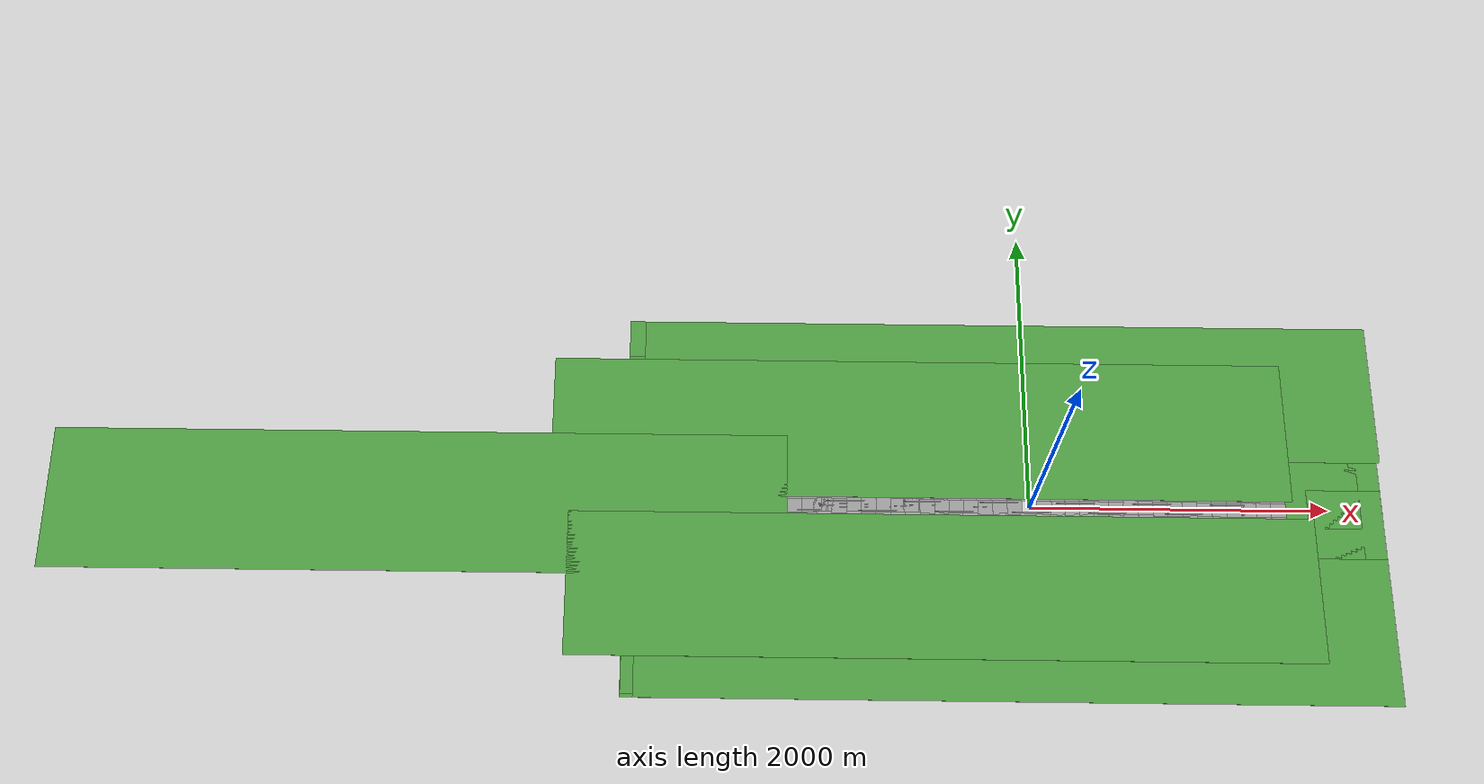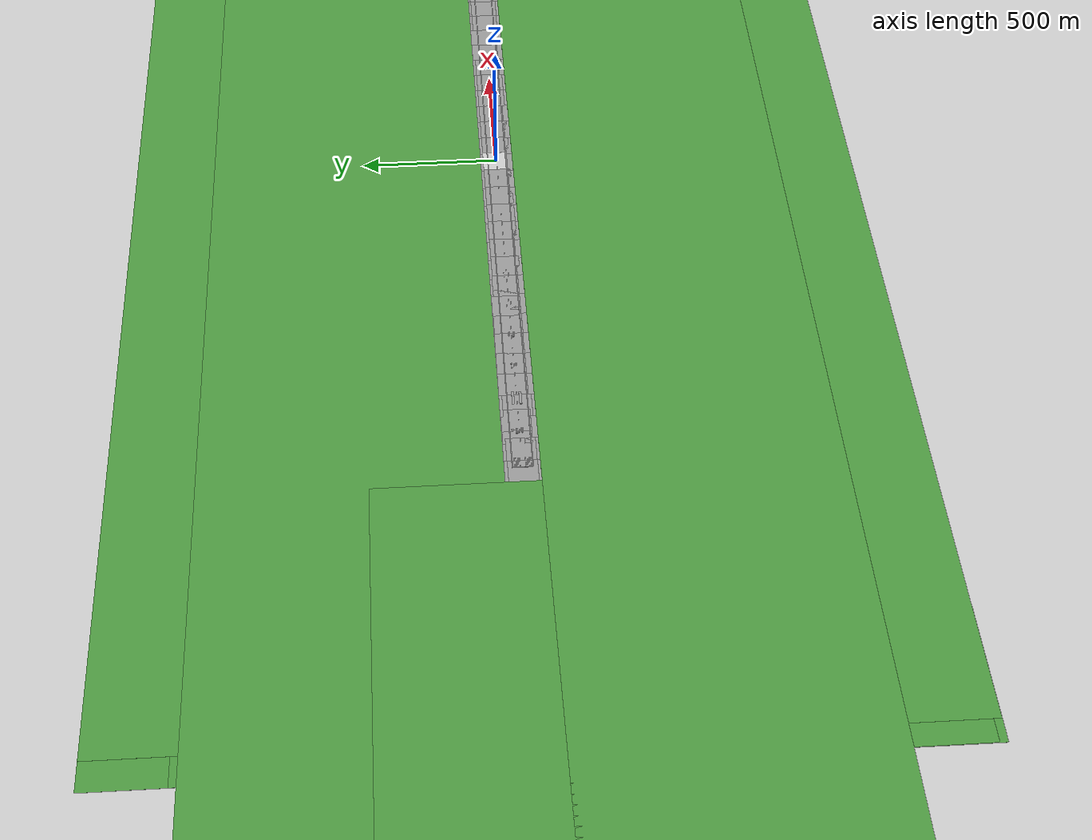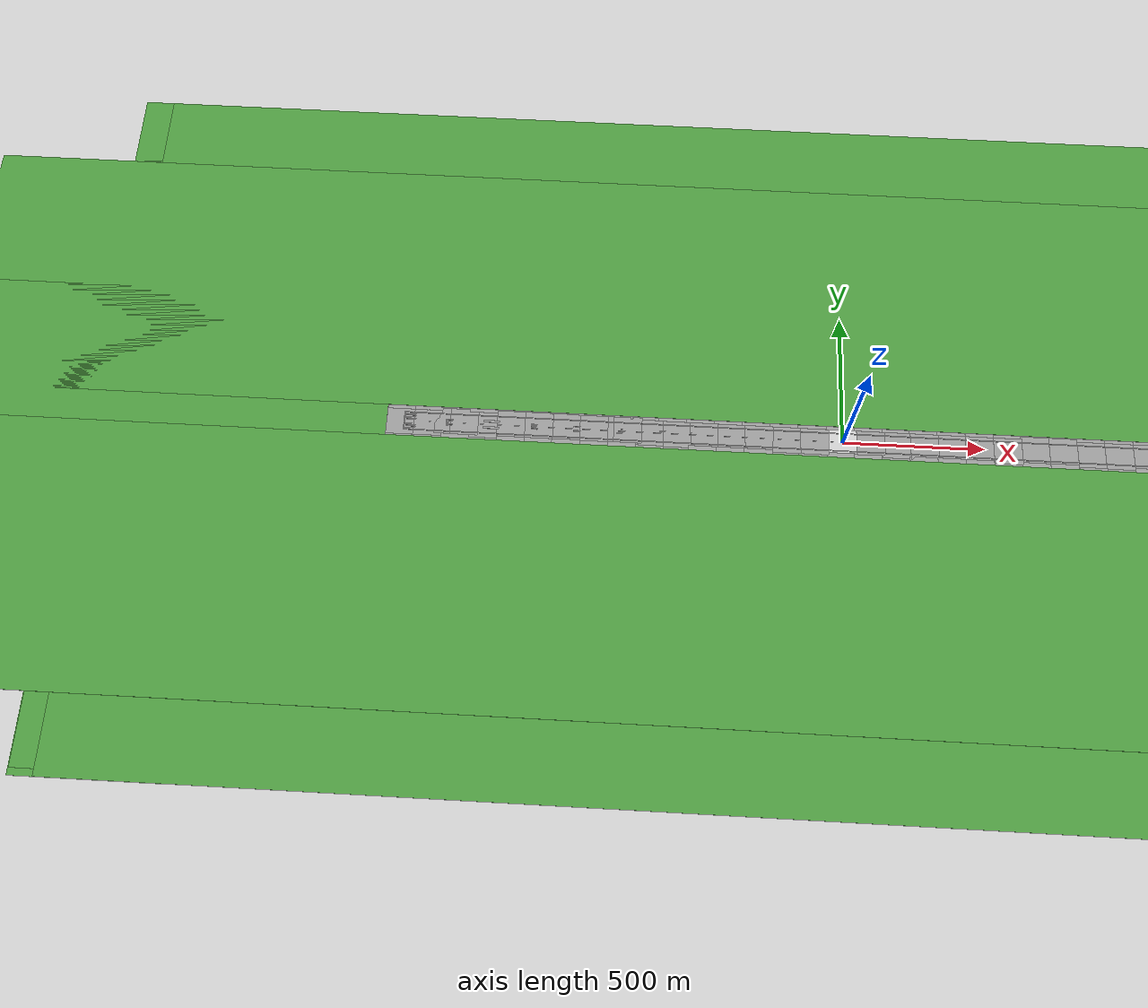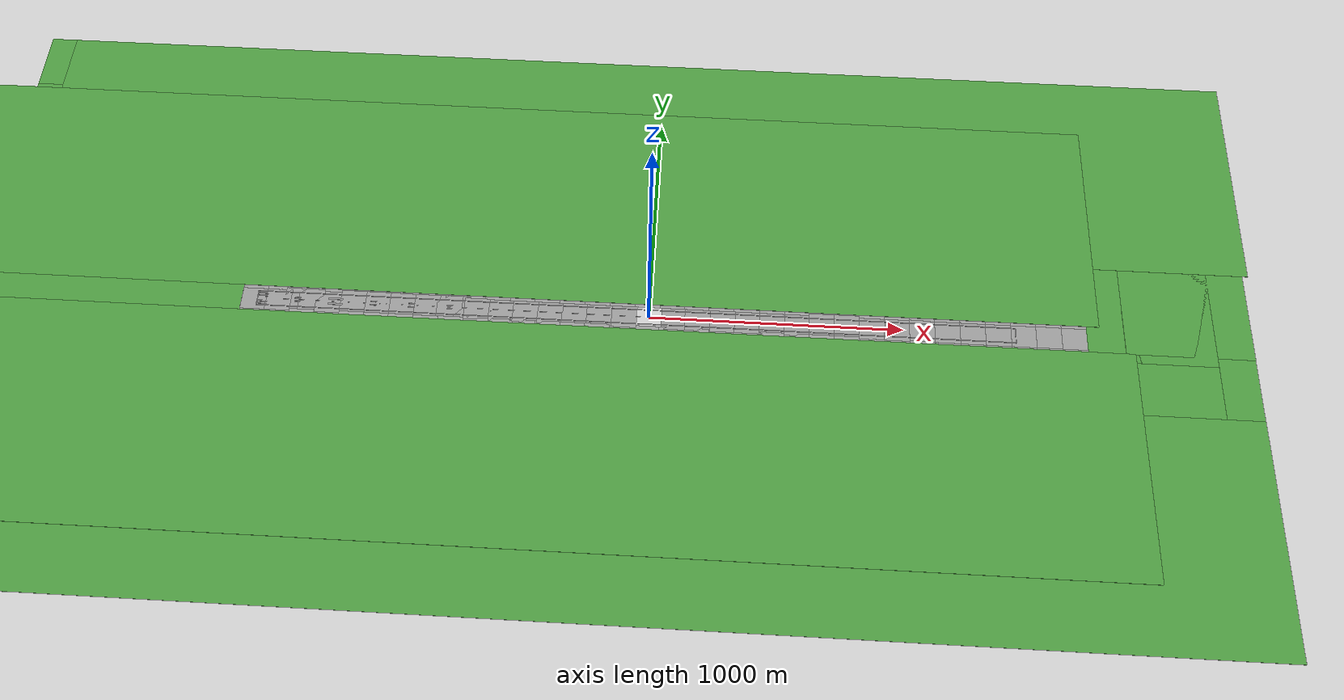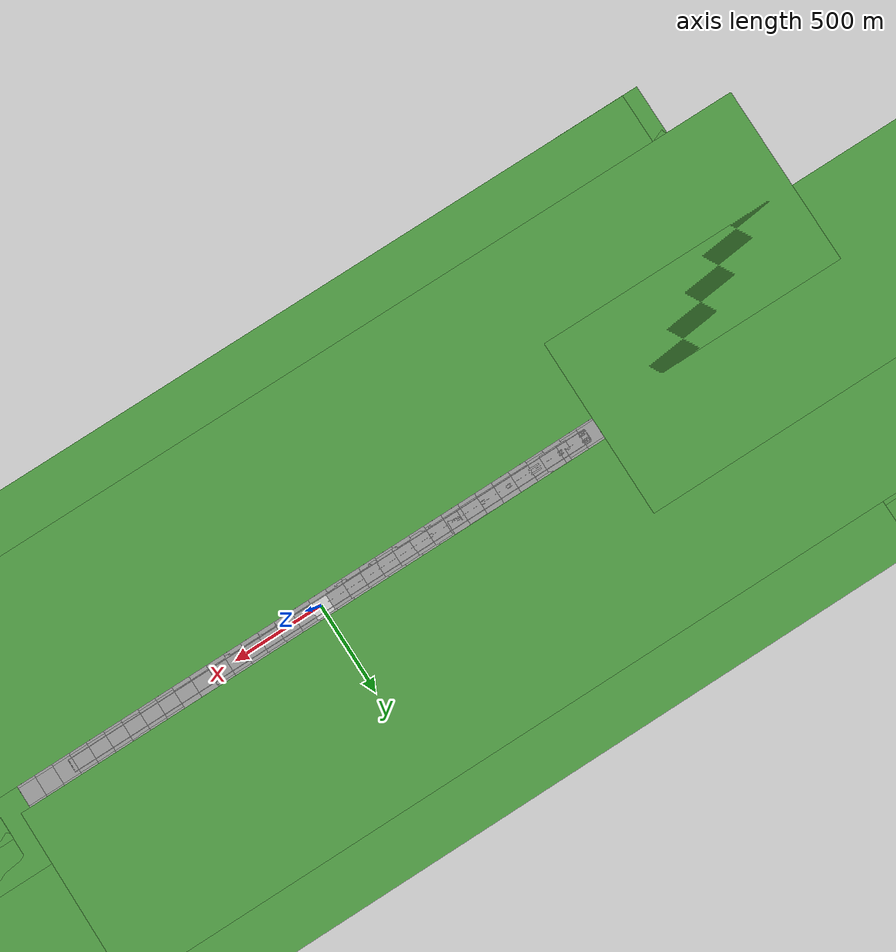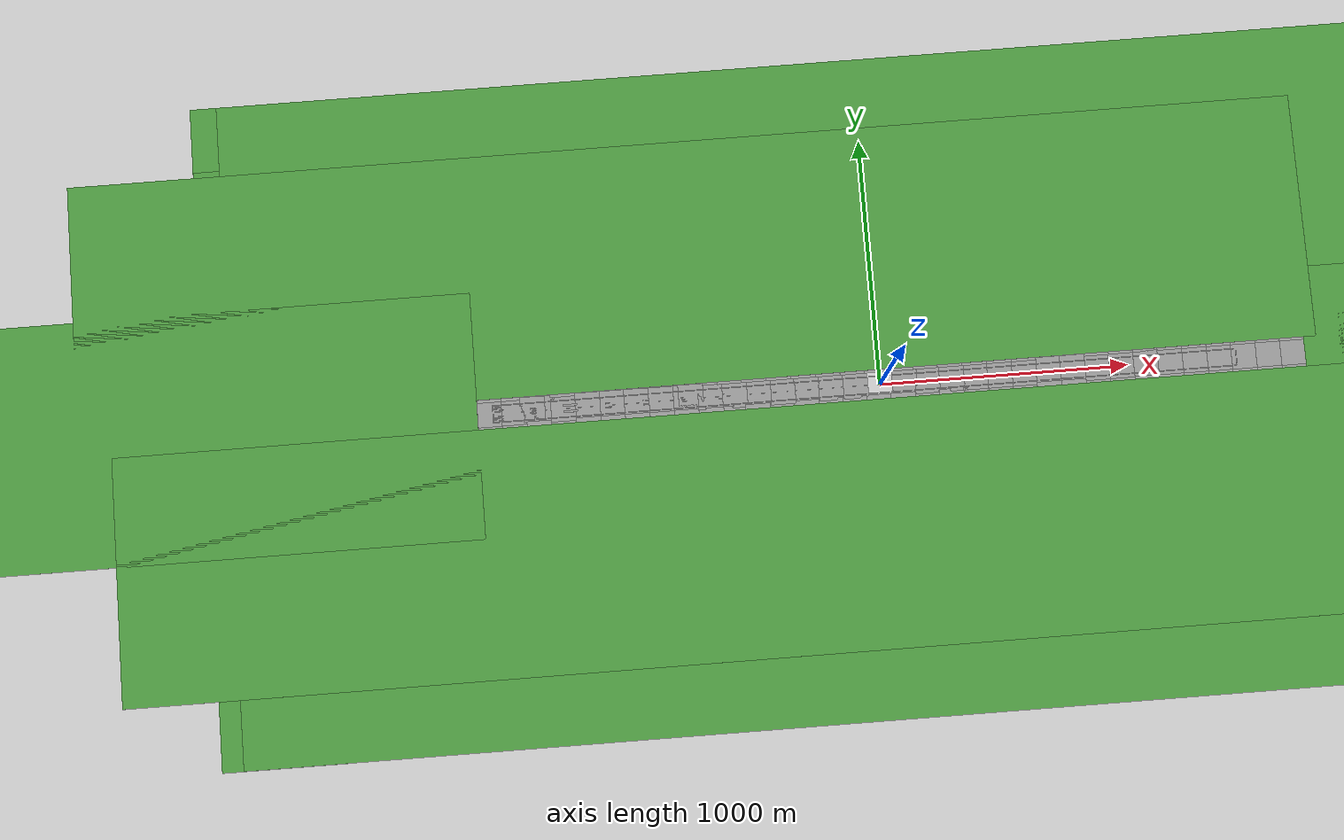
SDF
<sdf version="1.7">
 <world name="default">
  <scene>
   <sky><clouds><speed>12</speed></clouds></sky>
   <ambient>0.95 0.95 0.95 1</ambient>
   <background>0.3 0.3 0.3 1</background>
   <shadows>1</shadows>
  </scene>
  <light name="sun" type="directional">
   <pose>0 0 10 0 -0 0</pose>
   <diffuse>0.8 0.8 0.8 1</diffuse>
   <specular>0.2 0.2 0.2 1</specular>
   <attenuation>
    <range>1000</range>
    <constant>0.9</constant>
    <linear>0.01</linear>
    <quadratic>0.001</quadratic>
   </attenuation>
   <direction>-0.5 0.1 -0.9</direction>
   <spot><inner_angle>0</inner_angle><outer_angle>0</outer_angle><falloff>0</falloff></spot>
  </light>
  <model name="ground_plane">
   <static>1</static>
   <link name="link">
    <collision name="collision">
     <geometry><plane><normal>0 0 1</normal><size>100 100</size></plane></geometry>
     <surface><friction><ode><mu>100</mu><mu2>50</mu2></ode></friction></surface>
    </collision>
    <visual name="visual">
     <cast_shadows>0</cast_shadows>
     <geometry><plane><normal>0 0 1</normal><size>100 100</size></plane></geometry>
     <material>
      <script><uri>file://media/materials/scripts/gazebo.material</uri><name>Gazebo/Grey</name></script>
     </material>
    </visual>
   </link>
  </model>
  <gravity>0 0 -9.8</gravity>
  <magnetic_field>6e-06 2.3e-05 -4.2e-05</magnetic_field>
  <atmosphere type="adiabatic"/>
  <physics type="ode">
   <max_step_size>0.001</max_step_size>
   <real_time_factor>1</real_time_factor>
   <real_time_update_rate>1000</real_time_update_rate>
  </physics>
  <scene><ambient>0.4 0.4 0.4 1</ambient><background>0.7 0.7 0.7 1</background><shadows>1</shadows></scene>
  <spherical_coordinates>
   <surface_model>EARTH_WGS84</surface_model>
   <latitude_deg>0</latitude_deg>
   <longitude_deg>0</longitude_deg>
   <elevation>0</elevation>
   <heading_deg>0</heading_deg>
  </spherical_coordinates>
  <model name="ground_plane_0">
   <static>1</static>
   <link name="link">
    <collision name="collision">
     <geometry><plane><normal>0 0 1</normal><size>100 100</size></plane></geometry>
     <surface>
      <contact><collide_bitmask>65535</collide_bitmask></contact>
      <friction><ode><mu>100</mu><mu2>50</mu2></ode></friction>
     </surface>
    </collision>
    <visual name="visual">
     <cast_shadows>0</cast_shadows>
     <geometry><plane><normal>0 0 1</normal><size>100 100</size></plane></geometry>
     <material>
      <script><uri>file://media/materials/scripts/gazebo.material</uri><name>Gazebo/Grey</name></script>
     </material>
    </visual>
   </link>
   <pose>98.6274 -0.038647 0 0 -0 0</pose>
  </model>
  <model name="ground_plane_1">
   <static>1</static>
   <link name="link">
    <collision name="collision">
     <geometry><plane><normal>0 0 1</normal><size>100 100</size></plane></geometry>
     <surface>
      <contact><collide_bitmask>65535</collide_bitmask></contact>
      <friction><ode><mu>100</mu><mu2>50</mu2></ode></friction>
     </surface>
    </collision>
    <visual name="visual">
     <cast_shadows>0</cast_shadows>
     <geometry><plane><normal>0 0 1</normal><size>100 100</size></plane></geometry>
     <material>
      <script><uri>file://media/materials/scripts/gazebo.material</uri><name>Gazebo/Grey</name></script>
     </material>
    </visual>
   </link>
   <pose>189.869 0.088778 0 0 -0 0</pose>
  </model>
  <model name="ground_plane_2">
   <static>1</static>
   <link name="link">
    <collision name="collision">
     <geometry><plane><normal>0 0 1</normal><size>100 100</size></plane></geometry>
     <surface>
      <contact><collide_bitmask>65535</collide_bitmask></contact>
      <friction><ode><mu>100</mu><mu2>50</mu2></ode></friction>
     </surface>
    </collision>
    <visual name="visual">
     <cast_shadows>0</cast_shadows>
     <geometry><plane><normal>0 0 1</normal><size>100 100</size></plane></geometry>
     <material>
      <script><uri>file://media/materials/scripts/gazebo.material</uri><name>Gazebo/Grey</name></script>
     </material>
    </visual>
   </link>
   <pose>289.291 0.137369 0 0 -0 0</pose>
  </model>
  <model name="ground_plane_3">
   <static>1</static>
   <link name="link">
    <collision name="collision">
     <geometry><plane><normal>0 0 1</normal><size>100 100</size></plane></geometry>
     <surface>
      <contact><collide_bitmask>65535</collide_bitmask></contact>
      <friction><ode><mu>100</mu><mu2>50</mu2></ode></friction>
     </surface>
    </collision>
    <visual name="visual">
     <cast_shadows>0</cast_shadows>
     <geometry><plane><normal>0 0 1</normal><size>100 100</size></plane></geometry>
     <material>
      <script><uri>file://media/materials/scripts/gazebo.material</uri><name>Gazebo/Grey</name></script>
     </material>
    </visual>
   </link>
   <pose>384.2 0.162384 0 0 -0 0</pose>
  </model>
  <model name="ground_plane_4">
   <static>1</static>
   <link name="link">
    <collision name="collision">
     <geometry><plane><normal>0 0 1</normal><size>100 100</size></plane></geometry>
     <surface>
      <contact><collide_bitmask>65535</collide_bitmask></contact>
      <friction><ode><mu>100</mu><mu2>50</mu2></ode></friction>
     </surface>
    </collision>
    <visual name="visual">
     <cast_shadows>0</cast_shadows>
     <geometry><plane><normal>0 0 1</normal><size>100 100</size></plane></geometry>
     <material>
      <script><uri>file://media/materials/scripts/gazebo.material</uri><name>Gazebo/Grey</name></script>
     </material>
    </visual>
   </link>
   <pose>483.4 0.219802 0 0 -0 0</pose>
  </model>
  <model name="ground_plane_5">
   <static>1</static>
   <link name="link">
    <collision name="collision">
     <geometry><plane><normal>0 0 1</normal><size>100 100</size></plane></geometry>
     <surface>
      <contact><collide_bitmask>65535</collide_bitmask></contact>
      <friction><ode><mu>100</mu><mu2>50</mu2></ode></friction>
     </surface>
    </collision>
    <visual name="visual">
     <cast_shadows>0</cast_shadows>
     <geometry><plane><normal>0 0 1</normal><size>100 100</size></plane></geometry>
     <material>
      <script><uri>file://media/materials/scripts/gazebo.material</uri><name>Gazebo/Grey</name></script>
     </material>
    </visual>
   </link>
   <pose>-99.9513 0.00012 0 0 -0 0</pose>
  </model>
  <model name="ground_plane_6">
   <static>1</static>
   <link name="link">
    <collision name="collision">
     <geometry><plane><normal>0 0 1</normal><size>100 100</size></plane></geometry>
     <surface>
      <contact><collide_bitmask>65535</collide_bitmask></contact>
      <friction><ode><mu>100</mu><mu2>50</mu2></ode></friction>
     </surface>
    </collision>
    <visual name="visual">
     <cast_shadows>0</cast_shadows>
     <geometry><plane><normal>0 0 1</normal><size>100 100</size></plane></geometry>
     <material>
      <script><uri>file://media/materials/scripts/gazebo.material</uri><name>Gazebo/Grey</name></script>
     </material>
    </visual>
   </link>
   <pose>-199.166 0.057176 0 0 -0 0</pose>
  </model>
  <model name="ground_plane_7">
   <static>1</static>
   <link name="link">
    <collision name="collision">
     <geometry><plane><normal>0 0 1</normal><size>100 100</size></plane></geometry>
     <surface>
      <contact><collide_bitmask>65535</collide_bitmask></contact>
      <friction><ode><mu>100</mu><mu2>50</mu2></ode></friction>
     </surface>
    </collision>
    <visual name="visual">
     <cast_shadows>0</cast_shadows>
     <geometry><plane><normal>0 0 1</normal><size>100 100</size></plane></geometry>
     <material>
      <script><uri>file://media/materials/scripts/gazebo.material</uri><name>Gazebo/Grey</name></script>
     </material>
    </visual>
   </link>
   <pose>-297.406 0.070305 0 0 -0 0</pose>
  </model>
  <model name="ground_plane_8">
   <static>1</static>
   <link name="link">
    <collision name="collision">
     <geometry><plane><normal>0 0 1</normal><size>100 100</size></plane></geometry>
     <surface>
      <contact><collide_bitmask>65535</collide_bitmask></contact>
      <friction><ode><mu>100</mu><mu2>50</mu2></ode></friction>
     </surface>
    </collision>
    <visual name="visual">
     <cast_shadows>0</cast_shadows>
     <geometry><plane><normal>0 0 1</normal><size>100 100</size></plane></geometry>
     <material>
      <script><uri>file://media/materials/scripts/gazebo.material</uri><name>Gazebo/Grey</name></script>
     </material>
    </visual>
   </link>
   <pose>-394.201 0.105452 0 0 -0 0</pose>
  </model>
  <model name="ground_plane_9">
   <static>1</static>
   <link name="link">
    <collision name="collision">
     <geometry><plane><normal>0 0 1</normal><size>100 100</size></plane></geometry>
     <surface>
      <contact><collide_bitmask>65535</collide_bitmask></contact>
      <friction><ode><mu>100</mu><mu2>50</mu2></ode></friction>
     </surface>
    </collision>
    <visual name="visual">
     <cast_shadows>0</cast_shadows>
     <geometry><plane><normal>0 0 1</normal><size>100 100</size></plane></geometry>
     <material>
      <script><uri>file://media/materials/scripts/gazebo.material</uri><name>Gazebo/Grey</name></script>
     </material>
    </visual>
   </link>
   <pose>-491.857 0.172089 0 0 -0 0</pose>
  </model>
  <model name="ground_plane_10">
   <static>1</static>
   <link name="link">
    <collision name="collision">
     <geometry><plane><normal>0 0 1</normal><size>100 100</size></plane></geometry>
     <surface>
      <contact><collide_bitmask>65535</collide_bitmask></contact>
      <friction><ode><mu>100</mu><mu2>50</mu2></ode></friction>
     </surface>
    </collision>
    <visual name="visual">
     <cast_shadows>0</cast_shadows>
     <geometry><plane><normal>0 0 1</normal><size>100 100</size></plane></geometry>
     <material>
      <script><uri>file://media/materials/scripts/gazebo.material</uri><name>Gazebo/Grey</name></script>
     </material>
    </visual>
   </link>
   <pose>-587.901 0.180784 0 0 -0 0</pose>
  </model>
  <model name="ground_plane_11">
   <static>1</static>
   <link name="link">
    <collision name="collision">
     <geometry><plane><normal>0 0 1</normal><size>100 100</size></plane></geometry>
     <surface>
      <contact><collide_bitmask>65535</collide_bitmask></contact>
      <friction><ode><mu>100</mu><mu2>50</mu2></ode></friction>
     </surface>
    </collision>
    <visual name="visual">
     <cast_shadows>0</cast_shadows>
     <geometry><plane><normal>0 0 1</normal><size>100 100</size></plane></geometry>
     <material>
      <script><uri>file://media/materials/scripts/gazebo.material</uri><name>Gazebo/Grey</name></script>
     </material>
    </visual>
   </link>
   <pose>583.142 0.155845 0 0 -0 0</pose>
  </model>
  <model name="ground_plane_12">
   <static>1</static>
   <link name="link">
    <collision name="collision">
     <geometry><plane><normal>0 0 1</normal><size>100 100</size></plane></geometry>
     <surface>
      <contact><collide_bitmask>65535</collide_bitmask></contact>
      <friction><ode><mu>100</mu><mu2>50</mu2></ode></friction>
     </surface>
    </collision>
    <visual name="visual">
     <cast_shadows>0</cast_shadows>
     <geometry><plane><normal>0 0 1</normal><size>100 100</size></plane></geometry>
     <material>
      <script><uri>file://media/materials/scripts/gazebo.material</uri><name>Gazebo/Grey</name></script>
     </material>
    </visual>
   </link>
   <pose>-11.7816 -89.7768 0 0 -0 0</pose>
  </model>
  <model name="ground_plane_13">
   <static>1</static>
   <link name="link">
    <collision name="collision">
     <geometry><plane><normal>0 0 1</normal><size>100 100</size></plane></geometry>
     <surface>
      <contact><collide_bitmask>65535</collide_bitmask></contact>
      <friction><ode><mu>100</mu><mu2>50</mu2></ode></friction>
     </surface>
    </collision>
    <visual name="visual">
     <cast_shadows>0</cast_shadows>
     <geometry><plane><normal>0 0 1</normal><size>100 100</size></plane></geometry>
     <material>
      <script><uri>file://media/materials/scripts/gazebo.material</uri><name>Gazebo/Grey</name></script>
     </material>
    </visual>
   </link>
   <pose>86.8306 -89.8197 0 0 -0 0</pose>
  </model>
  <model name="ground_plane_14">
   <static>1</static>
   <link name="link">
    <collision name="collision">
     <geometry><plane><normal>0 0 1</normal><size>100 100</size></plane></geometry>
     <surface>
      <contact><collide_bitmask>65535</collide_bitmask></contact>
      <friction><ode><mu>100</mu><mu2>50</mu2></ode></friction>
     </surface>
    </collision>
    <visual name="visual">
     <cast_shadows>0</cast_shadows>
     <geometry><plane><normal>0 0 1</normal><size>100 100</size></plane></geometry>
     <material>
      <script><uri>file://media/materials/scripts/gazebo.material</uri><name>Gazebo/Grey</name></script>
     </material>
    </visual>
   </link>
   <pose>185.841 -89.9297 0 0 -0 0</pose>
  </model>
  <model name="ground_plane_15">
   <static>1</static>
   <link name="link">
    <collision name="collision">
     <geometry><plane><normal>0 0 1</normal><size>100 100</size></plane></geometry>
     <surface>
      <contact><collide_bitmask>65535</collide_bitmask></contact>
      <friction><ode><mu>100</mu><mu2>50</mu2></ode></friction>
     </surface>
    </collision>
    <visual name="visual">
     <cast_shadows>0</cast_shadows>
     <geometry><plane><normal>0 0 1</normal><size>100 100</size></plane></geometry>
     <material>
      <script><uri>file://media/materials/scripts/gazebo.material</uri><name>Gazebo/Grey</name></script>
     </material>
    </visual>
   </link>
   <pose>284.873 -89.7127 0 0 -0 0</pose>
  </model>
  <model name="ground_plane_16">
   <static>1</static>
   <link name="link">
    <collision name="collision">
     <geometry><plane><normal>0 0 1</normal><size>100 100</size></plane></geometry>
     <surface>
      <contact><collide_bitmask>65535</collide_bitmask></contact>
      <friction><ode><mu>100</mu><mu2>50</mu2></ode></friction>
     </surface>
    </collision>
    <visual name="visual">
     <cast_shadows>0</cast_shadows>
     <geometry><plane><normal>0 0 1</normal><size>100 100</size></plane></geometry>
     <material>
      <script><uri>file://media/materials/scripts/gazebo.material</uri><name>Gazebo/Grey</name></script>
     </material>
    </visual>
   </link>
   <pose>383.053 -89.8676 0 0 -0 0</pose>
  </model>
  <model name="ground_plane_17">
   <static>1</static>
   <link name="link">
    <collision name="collision">
     <geometry><plane><normal>0 0 1</normal><size>100 100</size></plane></geometry>
     <surface>
      <contact><collide_bitmask>65535</collide_bitmask></contact>
      <friction><ode><mu>100</mu><mu2>50</mu2></ode></friction>
     </surface>
    </collision>
    <visual name="visual">
     <cast_shadows>0</cast_shadows>
     <geometry><plane><normal>0 0 1</normal><size>100 100</size></plane></geometry>
     <material>
      <script><uri>file://media/materials/scripts/gazebo.material</uri><name>Gazebo/Grey</name></script>
     </material>
    </visual>
   </link>
   <pose>481.519 -90.0718 0 0 -0 0</pose>
  </model>
  <model name="ground_plane_18">
   <static>1</static>
   <link name="link">
    <collision name="collision">
     <geometry><plane><normal>0 0 1</normal><size>100 100</size></plane></geometry>
     <surface>
      <contact><collide_bitmask>65535</collide_bitmask></contact>
      <friction><ode><mu>100</mu><mu2>50</mu2></ode></friction>
     </surface>
    </collision>
    <visual name="visual">
     <cast_shadows>0</cast_shadows>
     <geometry><plane><normal>0 0 1</normal><size>100 100</size></plane></geometry>
     <material>
      <script><uri>file://media/materials/scripts/gazebo.material</uri><name>Gazebo/Grey</name></script>
     </material>
    </visual>
   </link>
   <pose>579.995 -90.1584 0 0 -0 0</pose>
  </model>
  <model name="ground_plane_19">
   <static>1</static>
   <link name="link">
    <collision name="collision">
     <geometry><plane><normal>0 0 1</normal><size>100 100</size></plane></geometry>
     <surface>
      <contact><collide_bitmask>65535</collide_bitmask></contact>
      <friction><ode><mu>100</mu><mu2>50</mu2></ode></friction>
     </surface>
    </collision>
    <visual name="visual">
     <cast_shadows>0</cast_shadows>
     <geometry><plane><normal>0 0 1</normal><size>100 100</size></plane></geometry>
     <material>
      <script><uri>file://media/materials/scripts/gazebo.material</uri><name>Gazebo/Grey</name></script>
     </material>
    </visual>
   </link>
   <pose>-108.415 -89.9777 0 0 -0 0</pose>
  </model>
  <model name="ground_plane_20">
   <static>1</static>
   <link name="link">
    <collision name="collision">
     <geometry><plane><normal>0 0 1</normal><size>100 100</size></plane></geometry>
     <surface>
      <contact><collide_bitmask>65535</collide_bitmask></contact>
      <friction><ode><mu>100</mu><mu2>50</mu2></ode></friction>
     </surface>
    </collision>
    <visual name="visual">
     <cast_shadows>0</cast_shadows>
     <geometry><plane><normal>0 0 1</normal><size>100 100</size></plane></geometry>
     <material>
      <script><uri>file://media/materials/scripts/gazebo.material</uri><name>Gazebo/Grey</name></script>
     </material>
    </visual>
   </link>
   <pose>-205.248 -89.9164 0 0 -0 0</pose>
  </model>
  <model name="ground_plane_21">
   <static>1</static>
   <link name="link">
    <collision name="collision">
     <geometry><plane><normal>0 0 1</normal><size>100 100</size></plane></geometry>
     <surface>
      <contact><collide_bitmask>65535</collide_bitmask></contact>
      <friction><ode><mu>100</mu><mu2>50</mu2></ode></friction>
     </surface>
    </collision>
    <visual name="visual">
     <cast_shadows>0</cast_shadows>
     <geometry><plane><normal>0 0 1</normal><size>100 100</size></plane></geometry>
     <material>
      <script><uri>file://media/materials/scripts/gazebo.material</uri><name>Gazebo/Grey</name></script>
     </material>
    </visual>
   </link>
   <pose>-301.464 -90.0316 0 0 -0 0</pose>
  </model>
  <model name="ground_plane_22">
   <static>1</static>
   <link name="link">
    <collision name="collision">
     <geometry><plane><normal>0 0 1</normal><size>100 100</size></plane></geometry>
     <surface>
      <contact><collide_bitmask>65535</collide_bitmask></contact>
      <friction><ode><mu>100</mu><mu2>50</mu2></ode></friction>
     </surface>
    </collision>
    <visual name="visual">
     <cast_shadows>0</cast_shadows>
     <geometry><plane><normal>0 0 1</normal><size>100 100</size></plane></geometry>
     <material>
      <script><uri>file://media/materials/scripts/gazebo.material</uri><name>Gazebo/Grey</name></script>
     </material>
    </visual>
   </link>
   <pose>-399.702 -89.9287 0 0 -0 0</pose>
  </model>
  <model name="ground_plane_23">
   <static>1</static>
   <link name="link">
    <collision name="collision">
     <geometry><plane><normal>0 0 1</normal><size>100 100</size></plane></geometry>
     <surface>
      <contact><collide_bitmask>65535</collide_bitmask></contact>
      <friction><ode><mu>100</mu><mu2>50</mu2></ode></friction>
     </surface>
    </collision>
    <visual name="visual">
     <cast_shadows>0</cast_shadows>
     <geometry><plane><normal>0 0 1</normal><size>100 100</size></plane></geometry>
     <material>
      <script><uri>file://media/materials/scripts/gazebo.material</uri><name>Gazebo/Grey</name></script>
     </material>
    </visual>
   </link>
   <pose>-498.907 -90.1441 0 0 -0 0</pose>
  </model>
  <model name="ground_plane_24">
   <static>1</static>
   <link name="link">
    <collision name="collision">
     <geometry><plane><normal>0 0 1</normal><size>100 100</size></plane></geometry>
     <surface>
      <contact><collide_bitmask>65535</collide_bitmask></contact>
      <friction><ode><mu>100</mu><mu2>50</mu2></ode></friction>
     </surface>
    </collision>
    <visual name="visual">
     <cast_shadows>0</cast_shadows>
     <geometry><plane><normal>0 0 1</normal><size>100 100</size></plane></geometry>
     <material>
      <script><uri>file://media/materials/scripts/gazebo.material</uri><name>Gazebo/Grey</name></script>
     </material>
    </visual>
   </link>
   <pose>-587.867 -90.5029 0 0 -0 0</pose>
  </model>
  <model name="ground_plane_25">
   <static>1</static>
   <link name="link">
    <collision name="collision">
     <geometry><plane><normal>0 0 1</normal><size>100 100</size></plane></geometry>
     <surface>
      <contact><collide_bitmask>65535</collide_bitmask></contact>
      <friction><ode><mu>100</mu><mu2>50</mu2></ode></friction>
     </surface>
    </collision>
    <visual name="visual">
     <cast_shadows>0</cast_shadows>
     <geometry><plane><normal>0 0 1</normal><size>100 100</size></plane></geometry>
     <material>
      <script><uri>file://media/materials/scripts/gazebo.material</uri><name>Gazebo/Grey</name></script>
     </material>
    </visual>
   </link>
   <pose>583.344 99.8555 0 0 -0 0</pose>
  </model>
  <model name="ground_plane_26">
   <static>1</static>
   <link name="link">
    <collision name="collision">
     <geometry><plane><normal>0 0 1</normal><size>100 100</size></plane></geometry>
     <surface>
      <contact><collide_bitmask>65535</collide_bitmask></contact>
      <friction><ode><mu>100</mu><mu2>50</mu2></ode></friction>
     </surface>
    </collision>
    <visual name="visual">
     <cast_shadows>0</cast_shadows>
     <geometry><plane><normal>0 0 1</normal><size>100 100</size></plane></geometry>
     <material>
      <script><uri>file://media/materials/scripts/gazebo.material</uri><name>Gazebo/Grey</name></script>
     </material>
    </visual>
   </link>
   <pose>483.812 99.9791 0 0 -0 0</pose>
  </model>
  <model name="ground_plane_27">
   <static>1</static>
   <link name="link">
    <collision name="collision">
     <geometry><plane><normal>0 0 1</normal><size>100 100</size></plane></geometry>
     <surface>
      <contact><collide_bitmask>65535</collide_bitmask></contact>
      <friction><ode><mu>100</mu><mu2>50</mu2></ode></friction>
     </surface>
    </collision>
    <visual name="visual">
     <cast_shadows>0</cast_shadows>
     <geometry><plane><normal>0 0 1</normal><size>100 100</size></plane></geometry>
     <material>
      <script><uri>file://media/materials/scripts/gazebo.material</uri><name>Gazebo/Grey</name></script>
     </material>
    </visual>
   </link>
   <pose>383.847 100.1 0 0 -0 0</pose>
  </model>
  <model name="ground_plane_28">
   <static>1</static>
   <link name="link">
    <collision name="collision">
     <geometry><plane><normal>0 0 1</normal><size>100 100</size></plane></geometry>
     <surface>
      <contact><collide_bitmask>65535</collide_bitmask></contact>
      <friction><ode><mu>100</mu><mu2>50</mu2></ode></friction>
     </surface>
    </collision>
    <visual name="visual">
     <cast_shadows>0</cast_shadows>
     <geometry><plane><normal>0 0 1</normal><size>100 100</size></plane></geometry>
     <material>
      <script><uri>file://media/materials/scripts/gazebo.material</uri><name>Gazebo/Grey</name></script>
     </material>
    </visual>
   </link>
   <pose>283.896 100.09 0 0 -0 0</pose>
  </model>
  <model name="ground_plane_29">
   <static>1</static>
   <link name="link">
    <collision name="collision">
     <geometry><plane><normal>0 0 1</normal><size>100 100</size></plane></geometry>
     <surface>
      <contact><collide_bitmask>65535</collide_bitmask></contact>
      <friction><ode><mu>100</mu><mu2>50</mu2></ode></friction>
     </surface>
    </collision>
    <visual name="visual">
     <cast_shadows>0</cast_shadows>
     <geometry><plane><normal>0 0 1</normal><size>100 100</size></plane></geometry>
     <material>
      <script><uri>file://media/materials/scripts/gazebo.material</uri><name>Gazebo/Grey</name></script>
     </material>
    </visual>
   </link>
   <pose>185.337 100.068 0 0 -0 0</pose>
  </model>
  <model name="ground_plane_30">
   <static>1</static>
   <link name="link">
    <collision name="collision">
     <geometry><plane><normal>0 0 1</normal><size>100 100</size></plane></geometry>
     <surface>
      <contact><collide_bitmask>65535</collide_bitmask></contact>
      <friction><ode><mu>100</mu><mu2>50</mu2></ode></friction>
     </surface>
    </collision>
    <visual name="visual">
     <cast_shadows>0</cast_shadows>
     <geometry><plane><normal>0 0 1</normal><size>100 100</size></plane></geometry>
     <material>
      <script><uri>file://media/materials/scripts/gazebo.material</uri><name>Gazebo/Grey</name></script>
     </material>
    </visual>
   </link>
   <pose>90.569 99.9304 0 0 -0 0</pose>
  </model>
  <model name="ground_plane_31">
   <static>1</static>
   <link name="link">
    <collision name="collision">
     <geometry><plane><normal>0 0 1</normal><size>100 100</size></plane></geometry>
     <surface>
      <contact><collide_bitmask>65535</collide_bitmask></contact>
      <friction><ode><mu>100</mu><mu2>50</mu2></ode></friction>
     </surface>
    </collision>
    <visual name="visual">
     <cast_shadows>0</cast_shadows>
     <geometry><plane><normal>0 0 1</normal><size>100 100</size></plane></geometry>
     <material>
      <script><uri>file://media/materials/scripts/gazebo.material</uri><name>Gazebo/Grey</name></script>
     </material>
    </visual>
   </link>
   <pose>-9.31072 99.9603 0 0 -0 0</pose>
  </model>
  <model name="ground_plane_32">
   <static>1</static>
   <link name="link">
    <collision name="collision">
     <geometry><plane><normal>0 0 1</normal><size>100 100</size></plane></geometry>
     <surface>
      <contact><collide_bitmask>65535</collide_bitmask></contact>
      <friction><ode><mu>100</mu><mu2>50</mu2></ode></friction>
     </surface>
    </collision>
    <visual name="visual">
     <cast_shadows>0</cast_shadows>
     <geometry><plane><normal>0 0 1</normal><size>100 100</size></plane></geometry>
     <material>
      <script><uri>file://media/materials/scripts/gazebo.material</uri><name>Gazebo/Grey</name></script>
     </material>
    </visual>
   </link>
   <pose>-108.837 99.8776 0 0 -0 0</pose>
  </model>
  <model name="ground_plane_33">
   <static>1</static>
   <link name="link">
    <collision name="collision">
     <geometry><plane><normal>0 0 1</normal><size>100 100</size></plane></geometry>
     <surface>
      <contact><collide_bitmask>65535</collide_bitmask></contact>
      <friction><ode><mu>100</mu><mu2>50</mu2></ode></friction>
     </surface>
    </collision>
    <visual name="visual">
     <cast_shadows>0</cast_shadows>
     <geometry><plane><normal>0 0 1</normal><size>100 100</size></plane></geometry>
     <material>
      <script><uri>file://media/materials/scripts/gazebo.material</uri><name>Gazebo/Grey</name></script>
     </material>
    </visual>
   </link>
   <pose>-208.514 99.9253 0 0 -0 0</pose>
  </model>
  <model name="ground_plane_34">
   <static>1</static>
   <link name="link">
    <collision name="collision">
     <geometry><plane><normal>0 0 1</normal><size>100 100</size></plane></geometry>
     <surface>
      <contact><collide_bitmask>65535</collide_bitmask></contact>
      <friction><ode><mu>100</mu><mu2>50</mu2></ode></friction>
     </surface>
    </collision>
    <visual name="visual">
     <cast_shadows>0</cast_shadows>
     <geometry><plane><normal>0 0 1</normal><size>100 100</size></plane></geometry>
     <material>
      <script><uri>file://media/materials/scripts/gazebo.material</uri><name>Gazebo/Grey</name></script>
     </material>
    </visual>
   </link>
   <pose>-308.035 99.975 0 0 -0 0</pose>
  </model>
  <model name="ground_plane_35">
   <static>1</static>
   <link name="link">
    <collision name="collision">
     <geometry><plane><normal>0 0 1</normal><size>100 100</size></plane></geometry>
     <surface>
      <contact><collide_bitmask>65535</collide_bitmask></contact>
      <friction><ode><mu>100</mu><mu2>50</mu2></ode></friction>
     </surface>
    </collision>
    <visual name="visual">
     <cast_shadows>0</cast_shadows>
     <geometry><plane><normal>0 0 1</normal><size>100 100</size></plane></geometry>
     <material>
      <script><uri>file://media/materials/scripts/gazebo.material</uri><name>Gazebo/Grey</name></script>
     </material>
    </visual>
   </link>
   <pose>-407.885 99.9929 0 0 -0 0</pose>
  </model>
  <model name="ground_plane_36">
   <static>1</static>
   <link name="link">
    <collision name="collision">
     <geometry><plane><normal>0 0 1</normal><size>100 100</size></plane></geometry>
     <surface>
      <contact><collide_bitmask>65535</collide_bitmask></contact>
      <friction><ode><mu>100</mu><mu2>50</mu2></ode></friction>
     </surface>
    </collision>
    <visual name="visual">
     <cast_shadows>0</cast_shadows>
     <geometry><plane><normal>0 0 1</normal><size>100 100</size></plane></geometry>
     <material>
      <script><uri>file://media/materials/scripts/gazebo.material</uri><name>Gazebo/Grey</name></script>
     </material>
    </visual>
   </link>
   <pose>-507.176 99.8373 0 0 -0 0</pose>
  </model>
  <model name="ground_plane_37">
   <static>1</static>
   <link name="link">
    <collision name="collision">
     <geometry><plane><normal>0 0 1</normal><size>100 100</size></plane></geometry>
     <surface>
      <contact><collide_bitmask>65535</collide_bitmask></contact>
      <friction><ode><mu>100</mu><mu2>50</mu2></ode></friction>
     </surface>
    </collision>
    <visual name="visual">
     <cast_shadows>0</cast_shadows>
     <geometry><plane><normal>0 0 1</normal><size>100 100</size></plane></geometry>
     <material>
      <script><uri>file://media/materials/scripts/gazebo.material</uri><name>Gazebo/Grey</name></script>
     </material>
    </visual>
   </link>
   <pose>-607.041 99.8774 0 0 -0 0</pose>
  </model>
  <model name="ground_plane_38">
   <static>1</static>
   <link name="link">
    <collision name="collision">
     <geometry><plane><normal>0 0 1</normal><size>100 100</size></plane></geometry>
     <surface>
      <contact><collide_bitmask>65535</collide_bitmask></contact>
      <friction><ode><mu>100</mu><mu2>50</mu2></ode></friction>
     </surface>
    </collision>
    <visual name="visual">
     <cast_shadows>0</cast_shadows>
     <geometry><plane><normal>0 0 1</normal><size>100 100</size></plane></geometry>
     <material>
      <script><uri>file://media/materials/scripts/gazebo.material</uri><name>Gazebo/Grey</name></script>
     </material>
    </visual>
   </link>
   <pose>679.783 -90.0597 0 0 -0 0</pose>
  </model>
  <model name="ground_plane_39">
   <static>1</static>
   <link name="link">
    <collision name="collision">
     <geometry><plane><normal>0 0 1</normal><size>100 100</size></plane></geometry>
     <surface>
      <contact><collide_bitmask>65535</collide_bitmask></contact>
      <friction><ode><mu>100</mu><mu2>50</mu2></ode></friction>
     </surface>
    </collision>
    <visual name="visual">
     <cast_shadows>0</cast_shadows>
     <geometry><plane><normal>0 0 1</normal><size>100 100</size></plane></geometry>
     <material>
      <script><uri>file://media/materials/scripts/gazebo.material</uri><name>Gazebo/Grey</name></script>
     </material>
    </visual>
   </link>
   <pose>679.782 9.67716 0 0 -0 0</pose>
  </model>
  <model name="ground_plane_40">
   <static>1</static>
   <link name="link">
    <collision name="collision">
     <geometry><plane><normal>0 0 1</normal><size>100 100</size></plane></geometry>
     <surface>
      <contact><collide_bitmask>65535</collide_bitmask></contact>
      <friction><ode><mu>100</mu><mu2>50</mu2></ode></friction>
     </surface>
    </collision>
    <visual name="visual">
     <cast_shadows>0</cast_shadows>
     <geometry><plane><normal>0 0 1</normal><size>100 100</size></plane></geometry>
     <material>
      <script><uri>file://media/materials/scripts/gazebo.material</uri><name>Gazebo/Grey</name></script>
     </material>
    </visual>
   </link>
   <pose>682.586 109.571 0 0 -0 0</pose>
  </model>
  <model name="ground_plane_41">
   <static>1</static>
   <link name="link">
    <collision name="collision">
     <geometry><plane><normal>0 0 1</normal><size>100 100</size></plane></geometry>
     <surface>
      <contact><collide_bitmask>65535</collide_bitmask></contact>
      <friction><ode><mu>100</mu><mu2>50</mu2></ode></friction>
     </surface>
    </collision>
    <visual name="visual">
     <cast_shadows>0</cast_shadows>
     <geometry><plane><normal>0 0 1</normal><size>100 100</size></plane></geometry>
     <material>
      <script><uri>file://media/materials/scripts/gazebo.material</uri><name>Gazebo/Grey</name></script>
     </material>
    </visual>
   </link>
   <pose>779.284 -89.9308 0 0 -0 0</pose>
  </model>
  <model name="ground_plane_42">
   <static>1</static>
   <link name="link">
    <collision name="collision">
     <geometry><plane><normal>0 0 1</normal><size>100 100</size></plane></geometry>
     <surface>
      <contact><collide_bitmask>65535</collide_bitmask></contact>
      <friction><ode><mu>100</mu><mu2>50</mu2></ode></friction>
     </surface>
    </collision>
    <visual name="visual">
     <cast_shadows>0</cast_shadows>
     <geometry><plane><normal>0 0 1</normal><size>100 100</size></plane></geometry>
     <material>
      <script><uri>file://media/materials/scripts/gazebo.material</uri><name>Gazebo/Grey</name></script>
     </material>
    </visual>
   </link>
   <pose>779.063 9.76871 0 0 -0 0</pose>
  </model>
  <model name="ground_plane_43">
   <static>1</static>
   <link name="link">
    <collision name="collision">
     <geometry><plane><normal>0 0 1</normal><size>100 100</size></plane></geometry>
     <surface>
      <contact><collide_bitmask>65535</collide_bitmask></contact>
      <friction><ode><mu>100</mu><mu2>50</mu2></ode></friction>
     </surface>
    </collision>
    <visual name="visual">
     <cast_shadows>0</cast_shadows>
     <geometry><plane><normal>0 0 1</normal><size>100 100</size></plane></geometry>
     <material>
      <script><uri>file://media/materials/scripts/gazebo.material</uri><name>Gazebo/Grey</name></script>
     </material>
    </visual>
   </link>
   <pose>779.063 109.53 0 0 -0 0</pose>
  </model>
  <model name="ground_plane_44">
   <static>1</static>
   <link name="link">
    <collision name="collision">
     <geometry><plane><normal>0 0 1</normal><size>100 100</size></plane></geometry>
     <surface>
      <contact><collide_bitmask>65535</collide_bitmask></contact>
      <friction><ode><mu>100</mu><mu2>50</mu2></ode></friction>
     </surface>
    </collision>
    <visual name="visual">
     <cast_shadows>0</cast_shadows>
     <geometry><plane><normal>0 0 1</normal><size>100 100</size></plane></geometry>
     <material>
      <script><uri>file://media/materials/scripts/gazebo.material</uri><name>Gazebo/Grey</name></script>
     </material>
    </visual>
   </link>
   <pose>779.778 -189.58 0 0 -0 0</pose>
  </model>
  <model name="ground_plane_45">
   <static>1</static>
   <link name="link">
    <collision name="collision">
     <geometry><plane><normal>0 0 1</normal><size>100 100</size></plane></geometry>
     <surface>
      <contact><collide_bitmask>65535</collide_bitmask></contact>
      <friction><ode><mu>100</mu><mu2>50</mu2></ode></friction>
     </surface>
    </collision>
    <visual name="visual">
     <cast_shadows>0</cast_shadows>
     <geometry><plane><normal>0 0 1</normal><size>100 100</size></plane></geometry>
     <material>
      <script><uri>file://media/materials/scripts/gazebo.material</uri><name>Gazebo/Grey</name></script>
     </material>
    </visual>
   </link>
   <pose>679.964 -189.679 0 0 -0 0</pose>
  </model>
  <model name="ground_plane_46">
   <static>1</static>
   <link name="link">
    <collision name="collision">
     <geometry><plane><normal>0 0 1</normal><size>100 100</size></plane></geometry>
     <surface>
      <contact><collide_bitmask>65535</collide_bitmask></contact>
      <friction><ode><mu>100</mu><mu2>50</mu2></ode></friction>
     </surface>
    </collision>
    <visual name="visual">
     <cast_shadows>0</cast_shadows>
     <geometry><plane><normal>0 0 1</normal><size>100 100</size></plane></geometry>
     <material>
      <script><uri>file://media/materials/scripts/gazebo.material</uri><name>Gazebo/Grey</name></script>
     </material>
    </visual>
   </link>
   <pose>580.929 -189.656 0 0 -0 0</pose>
  </model>
  <model name="ground_plane_47">
   <static>1</static>
   <link name="link">
    <collision name="collision">
     <geometry><plane><normal>0 0 1</normal><size>100 100</size></plane></geometry>
     <surface>
      <contact><collide_bitmask>65535</collide_bitmask></contact>
      <friction><ode><mu>100</mu><mu2>50</mu2></ode></friction>
     </surface>
    </collision>
    <visual name="visual">
     <cast_shadows>0</cast_shadows>
     <geometry><plane><normal>0 0 1</normal><size>100 100</size></plane></geometry>
     <material>
      <script><uri>file://media/materials/scripts/gazebo.material</uri><name>Gazebo/Grey</name></script>
     </material>
    </visual>
   </link>
   <pose>481.923 -189.599 0 0 -0 0</pose>
  </model>
  <model name="ground_plane_48">
   <static>1</static>
   <link name="link">
    <collision name="collision">
     <geometry><plane><normal>0 0 1</normal><size>100 100</size></plane></geometry>
     <surface>
      <contact><collide_bitmask>65535</collide_bitmask></contact>
      <friction><ode><mu>100</mu><mu2>50</mu2></ode></friction>
     </surface>
    </collision>
    <visual name="visual">
     <cast_shadows>0</cast_shadows>
     <geometry><plane><normal>0 0 1</normal><size>100 100</size></plane></geometry>
     <material>
      <script><uri>file://media/materials/scripts/gazebo.material</uri><name>Gazebo/Grey</name></script>
     </material>
    </visual>
   </link>
   <pose>382.424 -189.408 0 0 -0 0</pose>
  </model>
  <model name="ground_plane_49">
   <static>1</static>
   <link name="link">
    <collision name="collision">
     <geometry><plane><normal>0 0 1</normal><size>100 100</size></plane></geometry>
     <surface>
      <contact><collide_bitmask>65535</collide_bitmask></contact>
      <friction><ode><mu>100</mu><mu2>50</mu2></ode></friction>
     </surface>
    </collision>
    <visual name="visual">
     <cast_shadows>0</cast_shadows>
     <geometry><plane><normal>0 0 1</normal><size>100 100</size></plane></geometry>
     <material>
      <script><uri>file://media/materials/scripts/gazebo.material</uri><name>Gazebo/Grey</name></script>
     </material>
    </visual>
   </link>
   <pose>283.057 -189.335 0 0 -0 0</pose>
  </model>
  <model name="ground_plane_50">
   <static>1</static>
   <link name="link">
    <collision name="collision">
     <geometry><plane><normal>0 0 1</normal><size>100 100</size></plane></geometry>
     <surface>
      <contact><collide_bitmask>65535</collide_bitmask></contact>
      <friction><ode><mu>100</mu><mu2>50</mu2></ode></friction>
     </surface>
    </collision>
    <visual name="visual">
     <cast_shadows>0</cast_shadows>
     <geometry><plane><normal>0 0 1</normal><size>100 100</size></plane></geometry>
     <material>
      <script><uri>file://media/materials/scripts/gazebo.material</uri><name>Gazebo/Grey</name></script>
     </material>
    </visual>
   </link>
   <pose>183.284 -189.234 0 0 -0 0</pose>
  </model>
  <model name="ground_plane_51">
   <static>1</static>
   <link name="link">
    <collision name="collision">
     <geometry><plane><normal>0 0 1</normal><size>100 100</size></plane></geometry>
     <surface>
      <contact><collide_bitmask>65535</collide_bitmask></contact>
      <friction><ode><mu>100</mu><mu2>50</mu2></ode></friction>
     </surface>
    </collision>
    <visual name="visual">
     <cast_shadows>0</cast_shadows>
     <geometry><plane><normal>0 0 1</normal><size>100 100</size></plane></geometry>
     <material>
      <script><uri>file://media/materials/scripts/gazebo.material</uri><name>Gazebo/Grey</name></script>
     </material>
    </visual>
   </link>
   <pose>83.2685 -189.583 0 0 -0 0</pose>
  </model>
  <model name="ground_plane_52">
   <static>1</static>
   <link name="link">
    <collision name="collision">
     <geometry><plane><normal>0 0 1</normal><size>100 100</size></plane></geometry>
     <surface>
      <contact><collide_bitmask>65535</collide_bitmask></contact>
      <friction><ode><mu>100</mu><mu2>50</mu2></ode></friction>
     </surface>
    </collision>
    <visual name="visual">
     <cast_shadows>0</cast_shadows>
     <geometry><plane><normal>0 0 1</normal><size>100 100</size></plane></geometry>
     <material>
      <script><uri>file://media/materials/scripts/gazebo.material</uri><name>Gazebo/Grey</name></script>
     </material>
    </visual>
   </link>
   <pose>-16.2945 -189.701 0 0 -0 0</pose>
  </model>
  <model name="ground_plane_53">
   <static>1</static>
   <link name="link">
    <collision name="collision">
     <geometry><plane><normal>0 0 1</normal><size>100 100</size></plane></geometry>
     <surface>
      <contact><collide_bitmask>65535</collide_bitmask></contact>
      <friction><ode><mu>100</mu><mu2>50</mu2></ode></friction>
     </surface>
    </collision>
    <visual name="visual">
     <cast_shadows>0</cast_shadows>
     <geometry><plane><normal>0 0 1</normal><size>100 100</size></plane></geometry>
     <material>
      <script><uri>file://media/materials/scripts/gazebo.material</uri><name>Gazebo/Grey</name></script>
     </material>
    </visual>
   </link>
   <pose>-115.105 -189.648 0 0 -0 0</pose>
  </model>
  <model name="ground_plane_54">
   <static>1</static>
   <link name="link">
    <collision name="collision">
     <geometry><plane><normal>0 0 1</normal><size>100 100</size></plane></geometry>
     <surface>
      <contact><collide_bitmask>65535</collide_bitmask></contact>
      <friction><ode><mu>100</mu><mu2>50</mu2></ode></friction>
     </surface>
    </collision>
    <visual name="visual">
     <cast_shadows>0</cast_shadows>
     <geometry><plane><normal>0 0 1</normal><size>100 100</size></plane></geometry>
     <material>
      <script><uri>file://media/materials/scripts/gazebo.material</uri><name>Gazebo/Grey</name></script>
     </material>
    </visual>
   </link>
   <pose>-214.806 -189.798 0 0 -0 0</pose>
  </model>
  <model name="ground_plane_55">
   <static>1</static>
   <link name="link">
    <collision name="collision">
     <geometry><plane><normal>0 0 1</normal><size>100 100</size></plane></geometry>
     <surface>
      <contact><collide_bitmask>65535</collide_bitmask></contact>
      <friction><ode><mu>100</mu><mu2>50</mu2></ode></friction>
     </surface>
    </collision>
    <visual name="visual">
     <cast_shadows>0</cast_shadows>
     <geometry><plane><normal>0 0 1</normal><size>100 100</size></plane></geometry>
     <material>
      <script><uri>file://media/materials/scripts/gazebo.material</uri><name>Gazebo/Grey</name></script>
     </material>
    </visual>
   </link>
   <pose>-314.361 -189.77 0 0 -0 0</pose>
  </model>
  <model name="ground_plane_56">
   <static>1</static>
   <link name="link">
    <collision name="collision">
     <geometry><plane><normal>0 0 1</normal><size>100 100</size></plane></geometry>
     <surface>
      <contact><collide_bitmask>65535</collide_bitmask></contact>
      <friction><ode><mu>100</mu><mu2>50</mu2></ode></friction>
     </surface>
    </collision>
    <visual name="visual">
     <cast_shadows>0</cast_shadows>
     <geometry><plane><normal>0 0 1</normal><size>100 100</size></plane></geometry>
     <material>
      <script><uri>file://media/materials/scripts/gazebo.material</uri><name>Gazebo/Grey</name></script>
     </material>
    </visual>
   </link>
   <pose>-413.182 -189.946 0 0 -0 0</pose>
  </model>
  <model name="ground_plane_57">
   <static>1</static>
   <link name="link">
    <collision name="collision">
     <geometry><plane><normal>0 0 1</normal><size>100 100</size></plane></geometry>
     <surface>
      <contact><collide_bitmask>65535</collide_bitmask></contact>
      <friction><ode><mu>100</mu><mu2>50</mu2></ode></friction>
     </surface>
    </collision>
    <visual name="visual">
     <cast_shadows>0</cast_shadows>
     <geometry><plane><normal>0 0 1</normal><size>100 100</size></plane></geometry>
     <material>
      <script><uri>file://media/materials/scripts/gazebo.material</uri><name>Gazebo/Grey</name></script>
     </material>
    </visual>
   </link>
   <pose>-513.218 -189.713 0 0 -0 0</pose>
  </model>
  <model name="ground_plane_58">
   <static>1</static>
   <link name="link">
    <collision name="collision">
     <geometry><plane><normal>0 0 1</normal><size>100 100</size></plane></geometry>
     <surface>
      <contact><collide_bitmask>65535</collide_bitmask></contact>
      <friction><ode><mu>100</mu><mu2>50</mu2></ode></friction>
     </surface>
    </collision>
    <visual name="visual">
     <cast_shadows>0</cast_shadows>
     <geometry><plane><normal>0 0 1</normal><size>100 100</size></plane></geometry>
     <material>
      <script><uri>file://media/materials/scripts/gazebo.material</uri><name>Gazebo/Grey</name></script>
     </material>
    </visual>
   </link>
   <pose>-612.504 -189.651 0 0 -0 0</pose>
  </model>
  <model name="ground_plane_59">
   <static>1</static>
   <link name="link">
    <collision name="collision">
     <geometry><plane><normal>0 0 1</normal><size>100 100</size></plane></geometry>
     <surface>
      <contact><collide_bitmask>65535</collide_bitmask></contact>
      <friction><ode><mu>100</mu><mu2>50</mu2></ode></friction>
     </surface>
    </collision>
    <visual name="visual">
     <cast_shadows>0</cast_shadows>
     <geometry><plane><normal>0 0 1</normal><size>100 100</size></plane></geometry>
     <material>
      <script><uri>file://media/materials/scripts/gazebo.material</uri><name>Gazebo/Grey</name></script>
     </material>
    </visual>
   </link>
   <pose>582.865 199.934 0 0 -0 0</pose>
  </model>
  <model name="ground_plane_60">
   <static>1</static>
   <link name="link">
    <collision name="collision">
     <geometry><plane><normal>0 0 1</normal><size>100 100</size></plane></geometry>
     <surface>
      <contact><collide_bitmask>65535</collide_bitmask></contact>
      <friction><ode><mu>100</mu><mu2>50</mu2></ode></friction>
     </surface>
    </collision>
    <visual name="visual">
     <cast_shadows>0</cast_shadows>
     <geometry><plane><normal>0 0 1</normal><size>100 100</size></plane></geometry>
     <material>
      <script><uri>file://media/materials/scripts/gazebo.material</uri><name>Gazebo/Grey</name></script>
     </material>
    </visual>
   </link>
   <pose>483.246 199.514 0 0 -0 0</pose>
  </model>
  <model name="ground_plane_61">
   <static>1</static>
   <link name="link">
    <collision name="collision">
     <geometry><plane><normal>0 0 1</normal><size>100 100</size></plane></geometry>
     <surface>
      <contact><collide_bitmask>65535</collide_bitmask></contact>
      <friction><ode><mu>100</mu><mu2>50</mu2></ode></friction>
     </surface>
    </collision>
    <visual name="visual">
     <cast_shadows>0</cast_shadows>
     <geometry><plane><normal>0 0 1</normal><size>100 100</size></plane></geometry>
     <material>
      <script><uri>file://media/materials/scripts/gazebo.material</uri><name>Gazebo/Grey</name></script>
     </material>
    </visual>
   </link>
   <pose>682.1 199.798 0 0 -0 0</pose>
  </model>
  <model name="ground_plane_62">
   <static>1</static>
   <link name="link">
    <collision name="collision">
     <geometry><plane><normal>0 0 1</normal><size>100 100</size></plane></geometry>
     <surface>
      <contact><collide_bitmask>65535</collide_bitmask></contact>
      <friction><ode><mu>100</mu><mu2>50</mu2></ode></friction>
     </surface>
    </collision>
    <visual name="visual">
     <cast_shadows>0</cast_shadows>
     <geometry><plane><normal>0 0 1</normal><size>100 100</size></plane></geometry>
     <material>
      <script><uri>file://media/materials/scripts/gazebo.material</uri><name>Gazebo/Grey</name></script>
     </material>
    </visual>
   </link>
   <pose>779.518 200.091 0 0 -0 0</pose>
  </model>
  <model name="ground_plane_63">
   <static>1</static>
   <link name="link">
    <collision name="collision">
     <geometry><plane><normal>0 0 1</normal><size>100 100</size></plane></geometry>
     <surface>
      <contact><collide_bitmask>65535</collide_bitmask></contact>
      <friction><ode><mu>100</mu><mu2>50</mu2></ode></friction>
     </surface>
    </collision>
    <visual name="visual">
     <cast_shadows>0</cast_shadows>
     <geometry><plane><normal>0 0 1</normal><size>100 100</size></plane></geometry>
     <material>
      <script><uri>file://media/materials/scripts/gazebo.material</uri><name>Gazebo/Grey</name></script>
     </material>
    </visual>
   </link>
   <pose>384.005 199.591 0 0 -0 0</pose>
  </model>
  <model name="ground_plane_64">
   <static>1</static>
   <link name="link">
    <collision name="collision">
     <geometry><plane><normal>0 0 1</normal><size>100 100</size></plane></geometry>
     <surface>
      <contact><collide_bitmask>65535</collide_bitmask></contact>
      <friction><ode><mu>100</mu><mu2>50</mu2></ode></friction>
     </surface>
    </collision>
    <visual name="visual">
     <cast_shadows>0</cast_shadows>
     <geometry><plane><normal>0 0 1</normal><size>100 100</size></plane></geometry>
     <material>
      <script><uri>file://media/materials/scripts/gazebo.material</uri><name>Gazebo/Grey</name></script>
     </material>
    </visual>
   </link>
   <pose>285.128 199.768 0 0 -0 0</pose>
  </model>
  <model name="ground_plane_65">
   <static>1</static>
   <link name="link">
    <collision name="collision">
     <geometry><plane><normal>0 0 1</normal><size>100 100</size></plane></geometry>
     <surface>
      <contact><collide_bitmask>65535</collide_bitmask></contact>
      <friction><ode><mu>100</mu><mu2>50</mu2></ode></friction>
     </surface>
    </collision>
    <visual name="visual">
     <cast_shadows>0</cast_shadows>
     <geometry><plane><normal>0 0 1</normal><size>100 100</size></plane></geometry>
     <material>
      <script><uri>file://media/materials/scripts/gazebo.material</uri><name>Gazebo/Grey</name></script>
     </material>
    </visual>
   </link>
   <pose>186.219 199.825 0 0 -0 0</pose>
  </model>
  <model name="ground_plane_66">
   <static>1</static>
   <link name="link">
    <collision name="collision">
     <geometry><plane><normal>0 0 1</normal><size>100 100</size></plane></geometry>
     <surface>
      <contact><collide_bitmask>65535</collide_bitmask></contact>
      <friction><ode><mu>100</mu><mu2>50</mu2></ode></friction>
     </surface>
    </collision>
    <visual name="visual">
     <cast_shadows>0</cast_shadows>
     <geometry><plane><normal>0 0 1</normal><size>100 100</size></plane></geometry>
     <material>
      <script><uri>file://media/materials/scripts/gazebo.material</uri><name>Gazebo/Grey</name></script>
     </material>
    </visual>
   </link>
   <pose>86.9116 199.899 0 0 -0 0</pose>
  </model>
  <model name="ground_plane_67">
   <static>1</static>
   <link name="link">
    <collision name="collision">
     <geometry><plane><normal>0 0 1</normal><size>100 100</size></plane></geometry>
     <surface>
      <contact><collide_bitmask>65535</collide_bitmask></contact>
      <friction><ode><mu>100</mu><mu2>50</mu2></ode></friction>
     </surface>
    </collision>
    <visual name="visual">
     <cast_shadows>0</cast_shadows>
     <geometry><plane><normal>0 0 1</normal><size>100 100</size></plane></geometry>
     <material>
      <script><uri>file://media/materials/scripts/gazebo.material</uri><name>Gazebo/Grey</name></script>
     </material>
    </visual>
   </link>
   <pose>-12.5684 199.977 0 0 -0 0</pose>
  </model>
  <model name="ground_plane_68">
   <static>1</static>
   <link name="link">
    <collision name="collision">
     <geometry><plane><normal>0 0 1</normal><size>100 100</size></plane></geometry>
     <surface>
      <contact><collide_bitmask>65535</collide_bitmask></contact>
      <friction><ode><mu>100</mu><mu2>50</mu2></ode></friction>
     </surface>
    </collision>
    <visual name="visual">
     <cast_shadows>0</cast_shadows>
     <geometry><plane><normal>0 0 1</normal><size>100 100</size></plane></geometry>
     <material>
      <script><uri>file://media/materials/scripts/gazebo.material</uri><name>Gazebo/Grey</name></script>
     </material>
    </visual>
   </link>
   <pose>-112.191 199.785 0 0 -0 0</pose>
  </model>
  <model name="ground_plane_69">
   <static>1</static>
   <link name="link">
    <collision name="collision">
     <geometry><plane><normal>0 0 1</normal><size>100 100</size></plane></geometry>
     <surface>
      <contact><collide_bitmask>65535</collide_bitmask></contact>
      <friction><ode><mu>100</mu><mu2>50</mu2></ode></friction>
     </surface>
    </collision>
    <visual name="visual">
     <cast_shadows>0</cast_shadows>
     <geometry><plane><normal>0 0 1</normal><size>100 100</size></plane></geometry>
     <material>
      <script><uri>file://media/materials/scripts/gazebo.material</uri><name>Gazebo/Grey</name></script>
     </material>
    </visual>
   </link>
   <pose>-211.401 199.564 0 0 -0 0</pose>
  </model>
  <model name="ground_plane_70">
   <static>1</static>
   <link name="link">
    <collision name="collision">
     <geometry><plane><normal>0 0 1</normal><size>100 100</size></plane></geometry>
     <surface>
      <contact><collide_bitmask>65535</collide_bitmask></contact>
      <friction><ode><mu>100</mu><mu2>50</mu2></ode></friction>
     </surface>
    </collision>
    <visual name="visual">
     <cast_shadows>0</cast_shadows>
     <geometry><plane><normal>0 0 1</normal><size>100 100</size></plane></geometry>
     <material>
      <script><uri>file://media/materials/scripts/gazebo.material</uri><name>Gazebo/Grey</name></script>
     </material>
    </visual>
   </link>
   <pose>-311.068 199.904 0 0 -0 0</pose>
  </model>
  <model name="ground_plane_71">
   <static>1</static>
   <link name="link">
    <collision name="collision">
     <geometry><plane><normal>0 0 1</normal><size>100 100</size></plane></geometry>
     <surface>
      <contact><collide_bitmask>65535</collide_bitmask></contact>
      <friction><ode><mu>100</mu><mu2>50</mu2></ode></friction>
     </surface>
    </collision>
    <visual name="visual">
     <cast_shadows>0</cast_shadows>
     <geometry><plane><normal>0 0 1</normal><size>100 100</size></plane></geometry>
     <material>
      <script><uri>file://media/materials/scripts/gazebo.material</uri><name>Gazebo/Grey</name></script>
     </material>
    </visual>
   </link>
   <pose>-409.994 199.617 0 0 -0 0</pose>
  </model>
  <model name="ground_plane_72">
   <static>1</static>
   <link name="link">
    <collision name="collision">
     <geometry><plane><normal>0 0 1</normal><size>100 100</size></plane></geometry>
     <surface>
      <contact><collide_bitmask>65535</collide_bitmask></contact>
      <friction><ode><mu>100</mu><mu2>50</mu2></ode></friction>
     </surface>
    </collision>
    <visual name="visual">
     <cast_shadows>0</cast_shadows>
     <geometry><plane><normal>0 0 1</normal><size>100 100</size></plane></geometry>
     <material>
      <script><uri>file://media/materials/scripts/gazebo.material</uri><name>Gazebo/Grey</name></script>
     </material>
    </visual>
   </link>
   <pose>-509.993 199.829 0 0 -0 0</pose>
  </model>
  <model name="ground_plane_73">
   <static>1</static>
   <link name="link">
    <collision name="collision">
     <geometry><plane><normal>0 0 1</normal><size>100 100</size></plane></geometry>
     <surface>
      <contact><collide_bitmask>65535</collide_bitmask></contact>
      <friction><ode><mu>100</mu><mu2>50</mu2></ode></friction>
     </surface>
    </collision>
    <visual name="visual">
     <cast_shadows>0</cast_shadows>
     <geometry><plane><normal>0 0 1</normal><size>100 100</size></plane></geometry>
     <material>
      <script><uri>file://media/materials/scripts/gazebo.material</uri><name>Gazebo/Grey</name></script>
     </material>
    </visual>
   </link>
   <pose>-606.817 199.675 0 0 -0 0</pose>
  </model>
  <model name="ground_plane_74">
   <static>1</static>
   <link name="link">
    <collision name="collision">
     <geometry><plane><normal>0 0 1</normal><size>100 100</size></plane></geometry>
     <surface>
      <contact><collide_bitmask>65535</collide_bitmask></contact>
      <friction><ode><mu>100</mu><mu2>50</mu2></ode></friction>
     </surface>
    </collision>
    <visual name="visual">
     <cast_shadows>0</cast_shadows>
     <geometry><plane><normal>0 0 1</normal><size>100 100</size></plane></geometry>
     <material>
      <script><uri>file://media/materials/scripts/gazebo.material</uri><name>Gazebo/Grey</name></script>
     </material>
    </visual>
   </link>
   <pose>-686.27 -90.9953 0 0 -0 0</pose>
  </model>
  <model name="ground_plane_75">
   <static>1</static>
   <link name="link">
    <collision name="collision">
     <geometry><plane><normal>0 0 1</normal><size>100 100</size></plane></geometry>
     <surface>
      <contact><collide_bitmask>65535</collide_bitmask></contact>
      <friction><ode><mu>100</mu><mu2>50</mu2></ode></friction>
     </surface>
    </collision>
    <visual name="visual">
     <cast_shadows>0</cast_shadows>
     <geometry><plane><normal>0 0 1</normal><size>100 100</size></plane></geometry>
     <material>
      <script><uri>file://media/materials/scripts/gazebo.material</uri><name>Gazebo/Grey</name></script>
     </material>
    </visual>
   </link>
   <pose>-686.497 2.20986 0 0 -0 0</pose>
  </model>
  <model name="ground_plane_76">
   <static>1</static>
   <link name="link">
    <collision name="collision">
     <geometry><plane><normal>0 0 1</normal><size>100 100</size></plane></geometry>
     <surface>
      <contact><collide_bitmask>65535</collide_bitmask></contact>
      <friction><ode><mu>100</mu><mu2>50</mu2></ode></friction>
     </surface>
    </collision>
    <visual name="visual">
     <cast_shadows>0</cast_shadows>
     <geometry><plane><normal>0 0 1</normal><size>100 100</size></plane></geometry>
     <material>
      <script><uri>file://media/materials/scripts/gazebo.material</uri><name>Gazebo/Grey</name></script>
     </material>
    </visual>
   </link>
   <pose>-709.887 -189.674 0 0 -0 0</pose>
  </model>
  <model name="ground_plane_77">
   <static>1</static>
   <link name="link">
    <collision name="collision">
     <geometry><plane><normal>0 0 1</normal><size>100 100</size></plane></geometry>
     <surface>
      <contact><collide_bitmask>65535</collide_bitmask></contact>
      <friction><ode><mu>100</mu><mu2>50</mu2></ode></friction>
     </surface>
    </collision>
    <visual name="visual">
     <cast_shadows>0</cast_shadows>
     <geometry><plane><normal>0 0 1</normal><size>100 100</size></plane></geometry>
     <material>
      <script><uri>file://media/materials/scripts/gazebo.material</uri><name>Gazebo/Grey</name></script>
     </material>
    </visual>
   </link>
   <pose>-706.471 101.365 0 0 -0 0</pose>
  </model>
  <model name="ground_plane_78">
   <static>1</static>
   <link name="link">
    <collision name="collision">
     <geometry><plane><normal>0 0 1</normal><size>100 100</size></plane></geometry>
     <surface>
      <contact><collide_bitmask>65535</collide_bitmask></contact>
      <friction><ode><mu>100</mu><mu2>50</mu2></ode></friction>
     </surface>
    </collision>
    <visual name="visual">
     <cast_shadows>0</cast_shadows>
     <geometry><plane><normal>0 0 1</normal><size>100 100</size></plane></geometry>
     <material>
      <script><uri>file://media/materials/scripts/gazebo.material</uri><name>Gazebo/Grey</name></script>
     </material>
    </visual>
   </link>
   <pose>-706.499 199.373 0 0 -0 0</pose>
  </model>
  <model name="ground_plane_79">
   <static>1</static>
   <link name="link">
    <collision name="collision">
     <geometry><plane><normal>0 0 1</normal><size>100 100</size></plane></geometry>
     <surface>
      <contact><collide_bitmask>65535</collide_bitmask></contact>
      <friction><ode><mu>100</mu><mu2>50</mu2></ode></friction>
     </surface>
    </collision>
    <visual name="visual">
     <cast_shadows>0</cast_shadows>
     <geometry><plane><normal>0 0 1</normal><size>100 100</size></plane></geometry>
     <material>
      <script><uri>file://media/materials/scripts/gazebo.material</uri><name>Gazebo/Grey</name></script>
     </material>
    </visual>
   </link>
   <pose>-785.478 -90.7603 0 0 -0 0</pose>
  </model>
  <model name="ground_plane_80">
   <static>1</static>
   <link name="link">
    <collision name="collision">
     <geometry><plane><normal>0 0 1</normal><size>100 100</size></plane></geometry>
     <surface>
      <contact><collide_bitmask>65535</collide_bitmask></contact>
      <friction><ode><mu>100</mu><mu2>50</mu2></ode></friction>
     </surface>
    </collision>
    <visual name="visual">
     <cast_shadows>0</cast_shadows>
     <geometry><plane><normal>0 0 1</normal><size>100 100</size></plane></geometry>
     <material>
      <script><uri>file://media/materials/scripts/gazebo.material</uri><name>Gazebo/Grey</name></script>
     </material>
    </visual>
   </link>
   <pose>-795.2 9.06142 0 0 -0 0</pose>
  </model>
  <model name="ground_plane_81">
   <static>1</static>
   <link name="link">
    <collision name="collision">
     <geometry><plane><normal>0 0 1</normal><size>100 100</size></plane></geometry>
     <surface>
      <contact><collide_bitmask>65535</collide_bitmask></contact>
      <friction><ode><mu>100</mu><mu2>50</mu2></ode></friction>
     </surface>
    </collision>
    <visual name="visual">
     <cast_shadows>0</cast_shadows>
     <geometry><plane><normal>0 0 1</normal><size>100 100</size></plane></geometry>
     <material>
      <script><uri>file://media/materials/scripts/gazebo.material</uri><name>Gazebo/Grey</name></script>
     </material>
    </visual>
   </link>
   <pose>-809.897 -189.386 0 0 -0 0</pose>
  </model>
  <model name="ground_plane_82">
   <static>1</static>
   <link name="link">
    <collision name="collision">
     <geometry><plane><normal>0 0 1</normal><size>100 100</size></plane></geometry>
     <surface>
      <contact><collide_bitmask>65535</collide_bitmask></contact>
      <friction><ode><mu>100</mu><mu2>50</mu2></ode></friction>
     </surface>
    </collision>
    <visual name="visual">
     <cast_shadows>0</cast_shadows>
     <geometry><plane><normal>0 0 1</normal><size>100 100</size></plane></geometry>
     <material>
      <script><uri>file://media/materials/scripts/gazebo.material</uri><name>Gazebo/Grey</name></script>
     </material>
    </visual>
   </link>
   <pose>-804.459 107.681 0 0 -0 0</pose>
  </model>
  <model name="ground_plane_83">
   <static>1</static>
   <link name="link">
    <collision name="collision">
     <geometry><plane><normal>0 0 1</normal><size>100 100</size></plane></geometry>
     <surface>
      <contact><collide_bitmask>65535</collide_bitmask></contact>
      <friction><ode><mu>100</mu><mu2>50</mu2></ode></friction>
     </surface>
    </collision>
    <visual name="visual">
     <cast_shadows>0</cast_shadows>
     <geometry><plane><normal>0 0 1</normal><size>100 100</size></plane></geometry>
     <material>
      <script><uri>file://media/materials/scripts/gazebo.material</uri><name>Gazebo/Grey</name></script>
     </material>
    </visual>
   </link>
   <pose>-804.459 199.254 0 0 -0 0</pose>
  </model>
  <model name="ground_plane_84">
   <static>1</static>
   <link name="link">
    <collision name="collision">
     <geometry><plane><normal>0 0 1</normal><size>100 100</size></plane></geometry>
     <surface>
      <contact><collide_bitmask>65535</collide_bitmask></contact>
      <friction><ode><mu>100</mu><mu2>50</mu2></ode></friction>
     </surface>
    </collision>
    <visual name="visual">
     <cast_shadows>0</cast_shadows>
     <geometry><plane><normal>0 0 1</normal><size>100 100</size></plane></geometry>
     <material>
      <script><uri>file://media/materials/scripts/gazebo.material</uri><name>Gazebo/Grey</name></script>
     </material>
    </visual>
   </link>
   <pose>-885.158 -91.8052 0 0 -0 0</pose>
  </model>
  <model name="ground_plane_85">
   <static>1</static>
   <link name="link">
    <collision name="collision">
     <geometry><plane><normal>0 0 1</normal><size>100 100</size></plane></geometry>
     <surface>
      <contact><collide_bitmask>65535</collide_bitmask></contact>
      <friction><ode><mu>100</mu><mu2>50</mu2></ode></friction>
     </surface>
    </collision>
    <visual name="visual">
     <cast_shadows>0</cast_shadows>
     <geometry><plane><normal>0 0 1</normal><size>100 100</size></plane></geometry>
     <material>
      <script><uri>file://media/materials/scripts/gazebo.material</uri><name>Gazebo/Grey</name></script>
     </material>
    </visual>
   </link>
   <pose>-885.158 7.61601 0 0 -0 0</pose>
  </model>
  <model name="ground_plane_86">
   <static>1</static>
   <link name="link">
    <collision name="collision">
     <geometry><plane><normal>0 0 1</normal><size>100 100</size></plane></geometry>
     <surface>
      <contact><collide_bitmask>65535</collide_bitmask></contact>
      <friction><ode><mu>100</mu><mu2>50</mu2></ode></friction>
     </surface>
    </collision>
    <visual name="visual">
     <cast_shadows>0</cast_shadows>
     <geometry><plane><normal>0 0 1</normal><size>100 100</size></plane></geometry>
     <material>
      <script><uri>file://media/materials/scripts/gazebo.material</uri><name>Gazebo/Grey</name></script>
     </material>
    </visual>
   </link>
   <pose>-908.681 -189.853 0 0 -0 0</pose>
  </model>
  <model name="ground_plane_87">
   <static>1</static>
   <link name="link">
    <collision name="collision">
     <geometry><plane><normal>0 0 1</normal><size>100 100</size></plane></geometry>
     <surface>
      <contact><collide_bitmask>65535</collide_bitmask></contact>
      <friction><ode><mu>100</mu><mu2>50</mu2></ode></friction>
     </surface>
    </collision>
    <visual name="visual">
     <cast_shadows>0</cast_shadows>
     <geometry><plane><normal>0 0 1</normal><size>100 100</size></plane></geometry>
     <material>
      <script><uri>file://media/materials/scripts/gazebo.material</uri><name>Gazebo/Grey</name></script>
     </material>
    </visual>
   </link>
   <pose>-902.849 107.605 0 0 -0 0</pose>
  </model>
  <model name="ground_plane_88">
   <static>1</static>
   <link name="link">
    <collision name="collision">
     <geometry><plane><normal>0 0 1</normal><size>100 100</size></plane></geometry>
     <surface>
      <contact><collide_bitmask>65535</collide_bitmask></contact>
      <friction><ode><mu>100</mu><mu2>50</mu2></ode></friction>
     </surface>
    </collision>
    <visual name="visual">
     <cast_shadows>0</cast_shadows>
     <geometry><plane><normal>0 0 1</normal><size>100 100</size></plane></geometry>
     <material>
      <script><uri>file://media/materials/scripts/gazebo.material</uri><name>Gazebo/Grey</name></script>
     </material>
    </visual>
   </link>
   <pose>-903.394 198.956 0 0 -0 0</pose>
  </model>
  <model name="ground_plane_89">
   <static>1</static>
   <link name="link">
    <collision name="collision">
     <geometry><plane><normal>0 0 1</normal><size>100 100</size></plane></geometry>
     <surface>
      <contact><collide_bitmask>65535</collide_bitmask></contact>
      <friction><ode><mu>100</mu><mu2>50</mu2></ode></friction>
     </surface>
    </collision>
    <visual name="visual">
     <cast_shadows>0</cast_shadows>
     <geometry><plane><normal>0 0 1</normal><size>100 100</size></plane></geometry>
     <material>
      <script><uri>file://media/materials/scripts/gazebo.material</uri><name>Gazebo/Grey</name></script>
     </material>
    </visual>
   </link>
   <pose>-983.428 -90.3022 0 0 -0 0</pose>
  </model>
  <model name="ground_plane_90">
   <static>1</static>
   <link name="link">
    <collision name="collision">
     <geometry><plane><normal>0 0 1</normal><size>100 100</size></plane></geometry>
     <surface>
      <contact><collide_bitmask>65535</collide_bitmask></contact>
      <friction><ode><mu>100</mu><mu2>50</mu2></ode></friction>
     </surface>
    </collision>
    <visual name="visual">
     <cast_shadows>0</cast_shadows>
     <geometry><plane><normal>0 0 1</normal><size>100 100</size></plane></geometry>
     <material>
      <script><uri>file://media/materials/scripts/gazebo.material</uri><name>Gazebo/Grey</name></script>
     </material>
    </visual>
   </link>
   <pose>-983.694 8.85714 0 0 -0 0</pose>
  </model>
  <model name="ground_plane_91">
   <static>1</static>
   <link name="link">
    <collision name="collision">
     <geometry><plane><normal>0 0 1</normal><size>100 100</size></plane></geometry>
     <surface>
      <contact><collide_bitmask>65535</collide_bitmask></contact>
      <friction><ode><mu>100</mu><mu2>50</mu2></ode></friction>
     </surface>
    </collision>
    <visual name="visual">
     <cast_shadows>0</cast_shadows>
     <geometry><plane><normal>0 0 1</normal><size>100 100</size></plane></geometry>
     <material>
      <script><uri>file://media/materials/scripts/gazebo.material</uri><name>Gazebo/Grey</name></script>
     </material>
    </visual>
   </link>
   <pose>-1001.89 108.719 0 0 -0 0</pose>
  </model>
  <model name="ground_plane_92">
   <static>1</static>
   <link name="link">
    <collision name="collision">
     <geometry><plane><normal>0 0 1</normal><size>100 100</size></plane></geometry>
     <surface>
      <contact><collide_bitmask>65535</collide_bitmask></contact>
      <friction><ode><mu>100</mu><mu2>50</mu2></ode></friction>
     </surface>
    </collision>
    <visual name="visual">
     <cast_shadows>0</cast_shadows>
     <geometry><plane><normal>0 0 1</normal><size>100 100</size></plane></geometry>
     <material>
      <script><uri>file://media/materials/scripts/gazebo.material</uri><name>Gazebo/Grey</name></script>
     </material>
    </visual>
   </link>
   <pose>-1001.86 198.71 0 0 -0 0</pose>
  </model>
  <model name="ground_plane_93">
   <static>1</static>
   <link name="link">
    <collision name="collision">
     <geometry><plane><normal>0 0 1</normal><size>100 100</size></plane></geometry>
     <surface>
      <contact><collide_bitmask>65535</collide_bitmask></contact>
      <friction><ode><mu>100</mu><mu2>50</mu2></ode></friction>
     </surface>
    </collision>
    <visual name="visual">
     <cast_shadows>0</cast_shadows>
     <geometry><plane><normal>0 0 1</normal><size>100 100</size></plane></geometry>
     <material>
      <script><uri>file://media/materials/scripts/gazebo.material</uri><name>Gazebo/Grey</name></script>
     </material>
    </visual>
   </link>
   <pose>-1006.95 -189.733 0 0 -0 0</pose>
  </model>
  <model name="ground_plane_94">
   <static>1</static>
   <link name="link">
    <collision name="collision">
     <geometry><plane><normal>0 0 1</normal><size>100 100</size></plane></geometry>
     <surface>
      <contact><collide_bitmask>65535</collide_bitmask></contact>
      <friction><ode><mu>100</mu><mu2>50</mu2></ode></friction>
     </surface>
    </collision>
    <visual name="visual">
     <cast_shadows>0</cast_shadows>
     <geometry><plane><normal>0 0 1</normal><size>100 100</size></plane></geometry>
     <material>
      <script><uri>file://media/materials/scripts/gazebo.material</uri><name>Gazebo/Grey</name></script>
     </material>
    </visual>
   </link>
   <pose>-1081.04 -90.9755 0 0 -0 0</pose>
  </model>
  <model name="ground_plane_95">
   <static>1</static>
   <link name="link">
    <collision name="collision">
     <geometry><plane><normal>0 0 1</normal><size>100 100</size></plane></geometry>
     <surface>
      <contact><collide_bitmask>65535</collide_bitmask></contact>
      <friction><ode><mu>100</mu><mu2>50</mu2></ode></friction>
     </surface>
    </collision>
    <visual name="visual">
     <cast_shadows>0</cast_shadows>
     <geometry><plane><normal>0 0 1</normal><size>100 100</size></plane></geometry>
     <material>
      <script><uri>file://media/materials/scripts/gazebo.material</uri><name>Gazebo/Grey</name></script>
     </material>
    </visual>
   </link>
   <pose>-1081.04 8.92901 0 0 -0 0</pose>
  </model>
  <model name="ground_plane_96">
   <static>1</static>
   <link name="link">
    <collision name="collision">
     <geometry><plane><normal>0 0 1</normal><size>100 100</size></plane></geometry>
     <surface>
      <contact><collide_bitmask>65535</collide_bitmask></contact>
      <friction><ode><mu>100</mu><mu2>50</mu2></ode></friction>
     </surface>
    </collision>
    <visual name="visual">
     <cast_shadows>0</cast_shadows>
     <geometry><plane><normal>0 0 1</normal><size>100 100</size></plane></geometry>
     <material>
      <script><uri>file://media/materials/scripts/gazebo.material</uri><name>Gazebo/Grey</name></script>
     </material>
    </visual>
   </link>
   <pose>-1106.64 -190.225 0 0 -0 0</pose>
  </model>
  <model name="ground_plane_97">
   <static>1</static>
   <link name="link">
    <collision name="collision">
     <geometry><plane><normal>0 0 1</normal><size>100 100</size></plane></geometry>
     <surface>
      <contact><collide_bitmask>65535</collide_bitmask></contact>
      <friction><ode><mu>100</mu><mu2>50</mu2></ode></friction>
     </surface>
    </collision>
    <visual name="visual">
     <cast_shadows>0</cast_shadows>
     <geometry><plane><normal>0 0 1</normal><size>100 100</size></plane></geometry>
     <material>
      <script><uri>file://media/materials/scripts/gazebo.material</uri><name>Gazebo/Grey</name></script>
     </material>
    </visual>
   </link>
   <pose>-1101.01 108.929 0 0 -0 0</pose>
  </model>
  <model name="ground_plane_98">
   <static>1</static>
   <link name="link">
    <collision name="collision">
     <geometry><plane><normal>0 0 1</normal><size>100 100</size></plane></geometry>
     <surface>
      <contact><collide_bitmask>65535</collide_bitmask></contact>
      <friction><ode><mu>100</mu><mu2>50</mu2></ode></friction>
     </surface>
    </collision>
    <visual name="visual">
     <cast_shadows>0</cast_shadows>
     <geometry><plane><normal>0 0 1</normal><size>100 100</size></plane></geometry>
     <material>
      <script><uri>file://media/materials/scripts/gazebo.material</uri><name>Gazebo/Grey</name></script>
     </material>
    </visual>
   </link>
   <pose>-1101.01 198.742 0 0 -0 0</pose>
  </model>
  <model name="ground_plane_99">
   <static>1</static>
   <link name="link">
    <collision name="collision">
     <geometry><plane><normal>0 0 1</normal><size>100 100</size></plane></geometry>
     <surface>
      <contact><collide_bitmask>65535</collide_bitmask></contact>
      <friction><ode><mu>100</mu><mu2>50</mu2></ode></friction>
     </surface>
    </collision>
    <visual name="visual">
     <cast_shadows>0</cast_shadows>
     <geometry><plane><normal>0 0 1</normal><size>100 100</size></plane></geometry>
     <material>
      <script><uri>file://media/materials/scripts/gazebo.material</uri><name>Gazebo/Grey</name></script>
     </material>
    </visual>
   </link>
   <pose>878.257 199.838 0 0 -0 0</pose>
  </model>
  <model name="ground_plane_100">
   <static>1</static>
   <link name="link">
    <collision name="collision">
     <geometry><plane><normal>0 0 1</normal><size>100 100</size></plane></geometry>
     <surface>
      <contact><collide_bitmask>65535</collide_bitmask></contact>
      <friction><ode><mu>100</mu><mu2>50</mu2></ode></friction>
     </surface>
    </collision>
    <visual name="visual">
     <cast_shadows>0</cast_shadows>
     <geometry><plane><normal>0 0 1</normal><size>100 100</size></plane></geometry>
     <material>
      <script><uri>file://media/materials/scripts/gazebo.material</uri><name>Gazebo/Grey</name></script>
     </material>
    </visual>
   </link>
   <pose>878.209 99.8943 0 0 -0 0</pose>
  </model>
  <model name="ground_plane_101">
   <static>1</static>
   <link name="link">
    <collision name="collision">
     <geometry><plane><normal>0 0 1</normal><size>100 100</size></plane></geometry>
     <surface>
      <contact><collide_bitmask>65535</collide_bitmask></contact>
      <friction><ode><mu>100</mu><mu2>50</mu2></ode></friction>
     </surface>
    </collision>
    <visual name="visual">
     <cast_shadows>0</cast_shadows>
     <geometry><plane><normal>0 0 1</normal><size>100 100</size></plane></geometry>
     <material>
      <script><uri>file://media/materials/scripts/gazebo.material</uri><name>Gazebo/Grey</name></script>
     </material>
    </visual>
   </link>
   <pose>878.209 0.060441 0 0 -0 0</pose>
  </model>
  <model name="ground_plane_102">
   <static>1</static>
   <link name="link">
    <collision name="collision">
     <geometry><plane><normal>0 0 1</normal><size>100 100</size></plane></geometry>
     <surface>
      <contact><collide_bitmask>65535</collide_bitmask></contact>
      <friction><ode><mu>100</mu><mu2>50</mu2></ode></friction>
     </surface>
    </collision>
    <visual name="visual">
     <cast_shadows>0</cast_shadows>
     <geometry><plane><normal>0 0 1</normal><size>100 100</size></plane></geometry>
     <material>
      <script><uri>file://media/materials/scripts/gazebo.material</uri><name>Gazebo/Grey</name></script>
     </material>
    </visual>
   </link>
   <pose>878.209 -98.1632 0 0 -0 0</pose>
  </model>
  <model name="ground_plane_103">
   <static>1</static>
   <link name="link">
    <collision name="collision">
     <geometry><plane><normal>0 0 1</normal><size>100 100</size></plane></geometry>
     <surface>
      <contact><collide_bitmask>65535</collide_bitmask></contact>
      <friction><ode><mu>100</mu><mu2>50</mu2></ode></friction>
     </surface>
    </collision>
    <visual name="visual">
     <cast_shadows>0</cast_shadows>
     <geometry><plane><normal>0 0 1</normal><size>100 100</size></plane></geometry>
     <material>
      <script><uri>file://media/materials/scripts/gazebo.material</uri><name>Gazebo/Grey</name></script>
     </material>
    </visual>
   </link>
   <pose>877.861 -189.598 0 0 -0 0</pose>
  </model>
  <model name="ground_plane_104">
   <static>1</static>
   <link name="link">
    <collision name="collision">
     <geometry><plane><normal>0 0 1</normal><size>100 100</size></plane></geometry>
     <surface>
      <contact><collide_bitmask>65535</collide_bitmask></contact>
      <friction><ode><mu>100</mu><mu2>50</mu2></ode></friction>
     </surface>
    </collision>
    <visual name="visual">
     <cast_shadows>0</cast_shadows>
     <geometry><plane><normal>0 0 1</normal><size>100 100</size></plane></geometry>
     <material>
      <script><uri>file://media/materials/scripts/gazebo.material</uri><name>Gazebo/Grey</name></script>
     </material>
    </visual>
   </link>
   <pose>-1180.82 9.22917 0 0 -0 0</pose>
  </model>
  <model name="ground_plane_105">
   <static>1</static>
   <link name="link">
    <collision name="collision">
     <geometry><plane><normal>0 0 1</normal><size>100 100</size></plane></geometry>
     <surface>
      <contact><collide_bitmask>65535</collide_bitmask></contact>
      <friction><ode><mu>100</mu><mu2>50</mu2></ode></friction>
     </surface>
    </collision>
    <visual name="visual">
     <cast_shadows>0</cast_shadows>
     <geometry><plane><normal>0 0 1</normal><size>100 100</size></plane></geometry>
     <material>
      <script><uri>file://media/materials/scripts/gazebo.material</uri><name>Gazebo/Grey</name></script>
     </material>
    </visual>
   </link>
   <pose>-1180.82 -90.3767 0 0 -0 0</pose>
  </model>
  <model name="ground_plane_106">
   <static>1</static>
   <link name="link">
    <collision name="collision">
     <geometry><plane><normal>0 0 1</normal><size>100 100</size></plane></geometry>
     <surface>
      <contact><collide_bitmask>65535</collide_bitmask></contact>
      <friction><ode><mu>100</mu><mu2>50</mu2></ode></friction>
     </surface>
    </collision>
    <visual name="visual">
     <cast_shadows>0</cast_shadows>
     <geometry><plane><normal>0 0 1</normal><size>100 100</size></plane></geometry>
     <material>
      <script><uri>file://media/materials/scripts/gazebo.material</uri><name>Gazebo/Grey</name></script>
     </material>
    </visual>
   </link>
   <pose>-1180.82 108.835 0 0 -0 0</pose>
  </model>
  <model name="ground_plane_107">
   <static>1</static>
   <link name="link">
    <collision name="collision">
     <geometry><plane><normal>0 0 1</normal><size>100 100</size></plane></geometry>
     <surface>
      <contact><collide_bitmask>65535</collide_bitmask></contact>
      <friction><ode><mu>100</mu><mu2>50</mu2></ode></friction>
     </surface>
    </collision>
    <visual name="visual">
     <cast_shadows>0</cast_shadows>
     <geometry><plane><normal>0 0 1</normal><size>100 100</size></plane></geometry>
     <material>
      <script><uri>file://media/materials/scripts/gazebo.material</uri><name>Gazebo/Grey</name></script>
     </material>
    </visual>
   </link>
   <pose>-1180.82 198.555 0 0 -0 0</pose>
  </model>
  <model name="ground_plane_108">
   <static>1</static>
   <link name="link">
    <collision name="collision">
     <geometry><plane><normal>0 0 1</normal><size>100 100</size></plane></geometry>
     <surface>
      <contact><collide_bitmask>65535</collide_bitmask></contact>
      <friction><ode><mu>100</mu><mu2>50</mu2></ode></friction>
     </surface>
    </collision>
    <visual name="visual">
     <cast_shadows>0</cast_shadows>
     <geometry><plane><normal>0 0 1</normal><size>100 100</size></plane></geometry>
     <material>
      <script><uri>file://media/materials/scripts/gazebo.material</uri><name>Gazebo/Grey</name></script>
     </material>
    </visual>
   </link>
   <pose>975.791 200.029 0 0 -0 0</pose>
  </model>
  <model name="ground_plane_109">
   <static>1</static>
   <link name="link">
    <collision name="collision">
     <geometry><plane><normal>0 0 1</normal><size>100 100</size></plane></geometry>
     <surface>
      <contact><collide_bitmask>65535</collide_bitmask></contact>
      <friction><ode><mu>100</mu><mu2>50</mu2></ode></friction>
     </surface>
    </collision>
    <visual name="visual">
     <cast_shadows>0</cast_shadows>
     <geometry><plane><normal>0 0 1</normal><size>100 100</size></plane></geometry>
     <material>
      <script><uri>file://media/materials/scripts/gazebo.material</uri><name>Gazebo/Grey</name></script>
     </material>
    </visual>
   </link>
   <pose>976.085 100.44 0 0 -0 0</pose>
  </model>
  <model name="ground_plane_110">
   <static>1</static>
   <link name="link">
    <collision name="collision">
     <geometry><plane><normal>0 0 1</normal><size>100 100</size></plane></geometry>
     <surface>
      <contact><collide_bitmask>65535</collide_bitmask></contact>
      <friction><ode><mu>100</mu><mu2>50</mu2></ode></friction>
     </surface>
    </collision>
    <visual name="visual">
     <cast_shadows>0</cast_shadows>
     <geometry><plane><normal>0 0 1</normal><size>100 100</size></plane></geometry>
     <material>
      <script><uri>file://media/materials/scripts/gazebo.material</uri><name>Gazebo/Grey</name></script>
     </material>
    </visual>
   </link>
   <pose>976.086 0.493959 0 0 -0 0</pose>
  </model>
  <model name="ground_plane_111">
   <static>1</static>
   <link name="link">
    <collision name="collision">
     <geometry><plane><normal>0 0 1</normal><size>100 100</size></plane></geometry>
     <surface>
      <contact><collide_bitmask>65535</collide_bitmask></contact>
      <friction><ode><mu>100</mu><mu2>50</mu2></ode></friction>
     </surface>
    </collision>
    <visual name="visual">
     <cast_shadows>0</cast_shadows>
     <geometry><plane><normal>0 0 1</normal><size>100 100</size></plane></geometry>
     <material>
      <script><uri>file://media/materials/scripts/gazebo.material</uri><name>Gazebo/Grey</name></script>
     </material>
    </visual>
   </link>
   <pose>976.359 -99.3142 0 0 -0 0</pose>
  </model>
  <model name="ground_plane_112">
   <static>1</static>
   <link name="link">
    <collision name="collision">
     <geometry><plane><normal>0 0 1</normal><size>100 100</size></plane></geometry>
     <surface>
      <contact><collide_bitmask>65535</collide_bitmask></contact>
      <friction><ode><mu>100</mu><mu2>50</mu2></ode></friction>
     </surface>
    </collision>
    <visual name="visual">
     <cast_shadows>0</cast_shadows>
     <geometry><plane><normal>0 0 1</normal><size>100 100</size></plane></geometry>
     <material>
      <script><uri>file://media/materials/scripts/gazebo.material</uri><name>Gazebo/Grey</name></script>
     </material>
    </visual>
   </link>
   <pose>976.381 -190.136 0 0 -0 0</pose>
  </model>
  <model name="ground_plane_113">
   <static>1</static>
   <link name="link">
    <collision name="collision">
     <geometry><plane><normal>0 0 1</normal><size>100 100</size></plane></geometry>
     <surface>
      <contact><collide_bitmask>65535</collide_bitmask></contact>
      <friction><ode><mu>100</mu><mu2>50</mu2></ode></friction>
     </surface>
    </collision>
    <visual name="visual">
     <cast_shadows>0</cast_shadows>
     <geometry><plane><normal>0 0 1</normal><size>100 100</size></plane></geometry>
     <material>
      <script><uri>file://media/materials/scripts/gazebo.material</uri><name>Gazebo/Grey</name></script>
     </material>
    </visual>
   </link>
   <pose>1075.34 200.152 0 0 -0 0</pose>
  </model>
  <model name="ground_plane_114">
   <static>1</static>
   <link name="link">
    <collision name="collision">
     <geometry><plane><normal>0 0 1</normal><size>100 100</size></plane></geometry>
     <surface>
      <contact><collide_bitmask>65535</collide_bitmask></contact>
      <friction><ode><mu>100</mu><mu2>50</mu2></ode></friction>
     </surface>
    </collision>
    <visual name="visual">
     <cast_shadows>0</cast_shadows>
     <geometry><plane><normal>0 0 1</normal><size>100 100</size></plane></geometry>
     <material>
      <script><uri>file://media/materials/scripts/gazebo.material</uri><name>Gazebo/Grey</name></script>
     </material>
    </visual>
   </link>
   <pose>1075.56 100.596 0 0 -0 0</pose>
  </model>
  <model name="ground_plane_115">
   <static>1</static>
   <link name="link">
    <collision name="collision">
     <geometry><plane><normal>0 0 1</normal><size>100 100</size></plane></geometry>
     <surface>
      <contact><collide_bitmask>65535</collide_bitmask></contact>
      <friction><ode><mu>100</mu><mu2>50</mu2></ode></friction>
     </surface>
    </collision>
    <visual name="visual">
     <cast_shadows>0</cast_shadows>
     <geometry><plane><normal>0 0 1</normal><size>100 100</size></plane></geometry>
     <material>
      <script><uri>file://media/materials/scripts/gazebo.material</uri><name>Gazebo/Grey</name></script>
     </material>
    </visual>
   </link>
   <pose>1075.42 3.67946 0 0 -0 0</pose>
  </model>
  <model name="ground_plane_116">
   <static>1</static>
   <link name="link">
    <collision name="collision">
     <geometry><plane><normal>0 0 1</normal><size>100 100</size></plane></geometry>
     <surface>
      <contact><collide_bitmask>65535</collide_bitmask></contact>
      <friction><ode><mu>100</mu><mu2>50</mu2></ode></friction>
     </surface>
    </collision>
    <visual name="visual">
     <cast_shadows>0</cast_shadows>
     <geometry><plane><normal>0 0 1</normal><size>100 100</size></plane></geometry>
     <material>
      <script><uri>file://media/materials/scripts/gazebo.material</uri><name>Gazebo/Grey</name></script>
     </material>
    </visual>
   </link>
   <pose>1075.31 -91.5585 0 0 -0 0</pose>
  </model>
  <model name="ground_plane_117">
   <static>1</static>
   <link name="link">
    <collision name="collision">
     <geometry><plane><normal>0 0 1</normal><size>100 100</size></plane></geometry>
     <surface>
      <contact><collide_bitmask>65535</collide_bitmask></contact>
      <friction><ode><mu>100</mu><mu2>50</mu2></ode></friction>
     </surface>
    </collision>
    <visual name="visual">
     <cast_shadows>0</cast_shadows>
     <geometry><plane><normal>0 0 1</normal><size>100 100</size></plane></geometry>
     <material>
      <script><uri>file://media/materials/scripts/gazebo.material</uri><name>Gazebo/Grey</name></script>
     </material>
    </visual>
   </link>
   <pose>1075.46 -189.891 0 0 -0 0</pose>
  </model>
  <model name="ground_plane_118">
   <static>1</static>
   <link name="link">
    <collision name="collision">
     <geometry><plane><normal>0 0 1</normal><size>100 100</size></plane></geometry>
     <surface>
      <contact><collide_bitmask>65535</collide_bitmask></contact>
      <friction><ode><mu>100</mu><mu2>50</mu2></ode></friction>
     </surface>
    </collision>
    <visual name="visual">
     <cast_shadows>0</cast_shadows>
     <geometry><plane><normal>0 0 1</normal><size>100 100</size></plane></geometry>
     <material>
      <script><uri>file://media/materials/scripts/gazebo.material</uri><name>Gazebo/Grey</name></script>
     </material>
    </visual>
   </link>
   <pose>-1180.53 -189.975 0 0 -0 0</pose>
  </model>
  <model name="ground_plane_119">
   <static>1</static>
   <link name="link">
    <collision name="collision">
     <geometry><plane><normal>0 0 1</normal><size>100 100</size></plane></geometry>
     <surface>
      <contact><collide_bitmask>65535</collide_bitmask></contact>
      <friction><ode><mu>100</mu><mu2>50</mu2></ode></friction>
     </surface>
    </collision>
    <visual name="visual">
     <cast_shadows>0</cast_shadows>
     <geometry><plane><normal>0 0 1</normal><size>100 100</size></plane></geometry>
     <material>
      <script><uri>file://media/materials/scripts/gazebo.material</uri><name>Gazebo/Grey</name></script>
     </material>
    </visual>
   </link>
   <pose>1174.74 200.311 0 0 -0 0</pose>
  </model>
  <model name="ground_plane_120">
   <static>1</static>
   <link name="link">
    <collision name="collision">
     <geometry><plane><normal>0 0 1</normal><size>100 100</size></plane></geometry>
     <surface>
      <contact><collide_bitmask>65535</collide_bitmask></contact>
      <friction><ode><mu>100</mu><mu2>50</mu2></ode></friction>
     </surface>
    </collision>
    <visual name="visual">
     <cast_shadows>0</cast_shadows>
     <geometry><plane><normal>0 0 1</normal><size>100 100</size></plane></geometry>
     <material>
      <script><uri>file://media/materials/scripts/gazebo.material</uri><name>Gazebo/Grey</name></script>
     </material>
    </visual>
   </link>
   <pose>1174.8 100.671 0 0 -0 0</pose>
  </model>
  <model name="ground_plane_121">
   <static>1</static>
   <link name="link">
    <collision name="collision">
     <geometry><plane><normal>0 0 1</normal><size>100 100</size></plane></geometry>
     <surface>
      <contact><collide_bitmask>65535</collide_bitmask></contact>
      <friction><ode><mu>100</mu><mu2>50</mu2></ode></friction>
     </surface>
    </collision>
    <visual name="visual">
     <cast_shadows>0</cast_shadows>
     <geometry><plane><normal>0 0 1</normal><size>100 100</size></plane></geometry>
     <material>
      <script><uri>file://media/materials/scripts/gazebo.material</uri><name>Gazebo/Grey</name></script>
     </material>
    </visual>
   </link>
   <pose>1174.44 0.666128 0 0 -0 0</pose>
  </model>
  <model name="ground_plane_122">
   <static>1</static>
   <link name="link">
    <collision name="collision">
     <geometry><plane><normal>0 0 1</normal><size>100 100</size></plane></geometry>
     <surface>
      <contact><collide_bitmask>65535</collide_bitmask></contact>
      <friction><ode><mu>100</mu><mu2>50</mu2></ode></friction>
     </surface>
    </collision>
    <visual name="visual">
     <cast_shadows>0</cast_shadows>
     <geometry><plane><normal>0 0 1</normal><size>100 100</size></plane></geometry>
     <material>
      <script><uri>file://media/materials/scripts/gazebo.material</uri><name>Gazebo/Grey</name></script>
     </material>
    </visual>
   </link>
   <pose>1174.36 -98.4794 0 0 -0 0</pose>
  </model>
  <model name="ground_plane_123">
   <static>1</static>
   <link name="link">
    <collision name="collision">
     <geometry><plane><normal>0 0 1</normal><size>100 100</size></plane></geometry>
     <surface>
      <contact><collide_bitmask>65535</collide_bitmask></contact>
      <friction><ode><mu>100</mu><mu2>50</mu2></ode></friction>
     </surface>
    </collision>
    <visual name="visual">
     <cast_shadows>0</cast_shadows>
     <geometry><plane><normal>0 0 1</normal><size>100 100</size></plane></geometry>
     <material>
      <script><uri>file://media/materials/scripts/gazebo.material</uri><name>Gazebo/Grey</name></script>
     </material>
    </visual>
   </link>
   <pose>1174.72 -189.769 0 0 -0 0</pose>
  </model>
  <model name="ground_plane_124">
   <static>1</static>
   <link name="link">
    <collision name="collision">
     <geometry><plane><normal>0 0 1</normal><size>100 100</size></plane></geometry>
     <surface>
      <contact><collide_bitmask>65535</collide_bitmask></contact>
      <friction><ode><mu>100</mu><mu2>50</mu2></ode></friction>
     </surface>
    </collision>
    <visual name="visual">
     <cast_shadows>0</cast_shadows>
     <geometry><plane><normal>0 0 1</normal><size>100 100</size></plane></geometry>
     <material>
      <script><uri>file://media/materials/scripts/gazebo.material</uri><name>Gazebo/Grey</name></script>
     </material>
    </visual>
   </link>
   <pose>1274.67 200.295 0 0 -0 0</pose>
  </model>
  <model name="ground_plane_126">
   <static>1</static>
   <link name="link">
    <collision name="collision">
     <geometry><plane><normal>0 0 1</normal><size>100 100</size></plane></geometry>
     <surface>
      <contact><collide_bitmask>65535</collide_bitmask></contact>
      <friction><ode><mu>100</mu><mu2>50</mu2></ode></friction>
     </surface>
    </collision>
    <visual name="visual">
     <cast_shadows>0</cast_shadows>
     <geometry><plane><normal>0 0 1</normal><size>100 100</size></plane></geometry>
     <material>
      <script><uri>file://media/materials/scripts/gazebo.material</uri><name>Gazebo/Grey</name></script>
     </material>
    </visual>
   </link>
   <pose>1274.07 0.921542 0 0 -0 0</pose>
  </model>
  <model name="ground_plane_127">
   <static>1</static>
   <link name="link">
    <collision name="collision">
     <geometry><plane><normal>0 0 1</normal><size>100 100</size></plane></geometry>
     <surface>
      <contact><collide_bitmask>65535</collide_bitmask></contact>
      <friction><ode><mu>100</mu><mu2>50</mu2></ode></friction>
     </surface>
    </collision>
    <visual name="visual">
     <cast_shadows>0</cast_shadows>
     <geometry><plane><normal>0 0 1</normal><size>100 100</size></plane></geometry>
     <material>
      <script><uri>file://media/materials/scripts/gazebo.material</uri><name>Gazebo/Grey</name></script>
     </material>
    </visual>
   </link>
   <pose>1274.24 -98.974 0 0 -0 0</pose>
  </model>
  <model name="ground_plane_128">
   <static>1</static>
   <link name="link">
    <collision name="collision">
     <geometry><plane><normal>0 0 1</normal><size>100 100</size></plane></geometry>
     <surface>
      <contact><collide_bitmask>65535</collide_bitmask></contact>
      <friction><ode><mu>100</mu><mu2>50</mu2></ode></friction>
     </surface>
    </collision>
    <visual name="visual">
     <cast_shadows>0</cast_shadows>
     <geometry><plane><normal>0 0 1</normal><size>100 100</size></plane></geometry>
     <material>
      <script><uri>file://media/materials/scripts/gazebo.material</uri><name>Gazebo/Grey</name></script>
     </material>
    </visual>
   </link>
   <pose>1274.24 -198.31 0 0 -0 0</pose>
  </model>
  <model name="ground_plane_129">
   <static>1</static>
   <link name="link">
    <collision name="collision">
     <geometry><plane><normal>0 0 1</normal><size>100 100</size></plane></geometry>
     <surface>
      <contact><collide_bitmask>65535</collide_bitmask></contact>
      <friction><ode><mu>100</mu><mu2>50</mu2></ode></friction>
     </surface>
    </collision>
    <visual name="visual">
     <cast_shadows>0</cast_shadows>
     <geometry><plane><normal>0 0 1</normal><size>100 100</size></plane></geometry>
     <material>
      <script><uri>file://media/materials/scripts/gazebo.material</uri><name>Gazebo/Grey</name></script>
     </material>
    </visual>
   </link>
   <pose>1374.33 200.305 0 0 -0 0</pose>
  </model>
  <model name="ground_plane_125">
   <static>1</static>
   <link name="link">
    <collision name="collision">
     <geometry><plane><normal>0 0 1</normal><size>100 100</size></plane></geometry>
     <surface>
      <contact><collide_bitmask>65535</collide_bitmask></contact>
      <friction><ode><mu>100</mu><mu2>50</mu2></ode></friction>
     </surface>
    </collision>
    <visual name="visual">
     <cast_shadows>0</cast_shadows>
     <geometry><plane><normal>0 0 1</normal><size>100 100</size></plane></geometry>
     <material>
      <script><uri>file://media/materials/scripts/gazebo.material</uri><name>Gazebo/Grey</name></script>
     </material>
    </visual>
   </link>
   <pose>1274.23 100.358 0 0 -0 0</pose>
  </model>
  <model name="ground_plane_130">
   <static>1</static>
   <link name="link">
    <collision name="collision">
     <geometry><plane><normal>0 0 1</normal><size>100 100</size></plane></geometry>
     <surface>
      <contact><collide_bitmask>65535</collide_bitmask></contact>
      <friction><ode><mu>100</mu><mu2>50</mu2></ode></friction>
     </surface>
    </collision>
    <visual name="visual">
     <cast_shadows>0</cast_shadows>
     <geometry><plane><normal>0 0 1</normal><size>100 100</size></plane></geometry>
     <material>
      <script><uri>file://media/materials/scripts/gazebo.material</uri><name>Gazebo/Grey</name></script>
     </material>
    </visual>
   </link>
   <pose>1373.59 100.322 0 0 -0 0</pose>
  </model>
  <model name="ground_plane_131">
   <static>1</static>
   <link name="link">
    <collision name="collision">
     <geometry><plane><normal>0 0 1</normal><size>100 100</size></plane></geometry>
     <surface>
      <contact><collide_bitmask>65535</collide_bitmask></contact>
      <friction><ode><mu>100</mu><mu2>50</mu2></ode></friction>
     </surface>
    </collision>
    <visual name="visual">
     <cast_shadows>0</cast_shadows>
     <geometry><plane><normal>0 0 1</normal><size>100 100</size></plane></geometry>
     <material>
      <script><uri>file://media/materials/scripts/gazebo.material</uri><name>Gazebo/Grey</name></script>
     </material>
    </visual>
   </link>
   <pose>1373.57 0.586008 0 0 -0 0</pose>
  </model>
  <model name="ground_plane_132">
   <static>1</static>
   <link name="link">
    <collision name="collision">
     <geometry><plane><normal>0 0 1</normal><size>100 100</size></plane></geometry>
     <surface>
      <contact><collide_bitmask>65535</collide_bitmask></contact>
      <friction><ode><mu>100</mu><mu2>50</mu2></ode></friction>
     </surface>
    </collision>
    <visual name="visual">
     <cast_shadows>0</cast_shadows>
     <geometry><plane><normal>0 0 1</normal><size>100 100</size></plane></geometry>
     <material>
      <script><uri>file://media/materials/scripts/gazebo.material</uri><name>Gazebo/Grey</name></script>
     </material>
    </visual>
   </link>
   <pose>1373.74 -99.2938 0 0 -0 0</pose>
  </model>
  <model name="ground_plane_133">
   <static>1</static>
   <link name="link">
    <collision name="collision">
     <geometry><plane><normal>0 0 1</normal><size>100 100</size></plane></geometry>
     <surface>
      <contact><collide_bitmask>65535</collide_bitmask></contact>
      <friction><ode><mu>100</mu><mu2>50</mu2></ode></friction>
     </surface>
    </collision>
    <visual name="visual">
     <cast_shadows>0</cast_shadows>
     <geometry><plane><normal>0 0 1</normal><size>100 100</size></plane></geometry>
     <material>
      <script><uri>file://media/materials/scripts/gazebo.material</uri><name>Gazebo/Grey</name></script>
     </material>
    </visual>
   </link>
   <pose>1373.08 -199.046 0 0 -0 0</pose>
  </model>
  <model name="ground_plane_134">
   <static>1</static>
   <link name="link">
    <collision name="collision">
     <geometry><plane><normal>0 0 1</normal><size>100 100</size></plane></geometry>
     <surface>
      <contact><collide_bitmask>65535</collide_bitmask></contact>
      <friction><ode><mu>100</mu><mu2>50</mu2></ode></friction>
     </surface>
    </collision>
    <visual name="visual">
     <cast_shadows>0</cast_shadows>
     <geometry><plane><normal>0 0 1</normal><size>100 100</size></plane></geometry>
     <material>
      <script><uri>file://media/materials/scripts/gazebo.material</uri><name>Gazebo/Grey</name></script>
     </material>
    </visual>
   </link>
   <pose>1472.04 200.176 0 0 -0 0</pose>
  </model>
  <model name="ground_plane_135">
   <static>1</static>
   <link name="link">
    <collision name="collision">
     <geometry><plane><normal>0 0 1</normal><size>100 100</size></plane></geometry>
     <surface>
      <contact><collide_bitmask>65535</collide_bitmask></contact>
      <friction><ode><mu>100</mu><mu2>50</mu2></ode></friction>
     </surface>
    </collision>
    <visual name="visual">
     <cast_shadows>0</cast_shadows>
     <geometry><plane><normal>0 0 1</normal><size>100 100</size></plane></geometry>
     <material>
      <script><uri>file://media/materials/scripts/gazebo.material</uri><name>Gazebo/Grey</name></script>
     </material>
    </visual>
   </link>
   <pose>1472.08 100.144 0 0 -0 0</pose>
  </model>
  <model name="ground_plane_136">
   <static>1</static>
   <link name="link">
    <collision name="collision">
     <geometry><plane><normal>0 0 1</normal><size>100 100</size></plane></geometry>
     <surface>
      <contact><collide_bitmask>65535</collide_bitmask></contact>
      <friction><ode><mu>100</mu><mu2>50</mu2></ode></friction>
     </surface>
    </collision>
    <visual name="visual">
     <cast_shadows>0</cast_shadows>
     <geometry><plane><normal>0 0 1</normal><size>100 100</size></plane></geometry>
     <material>
      <script><uri>file://media/materials/scripts/gazebo.material</uri><name>Gazebo/Grey</name></script>
     </material>
    </visual>
   </link>
   <pose>1472.1 0.4361 0 0 -0 0</pose>
  </model>
  <model name="ground_plane_137">
   <static>1</static>
   <link name="link">
    <collision name="collision">
     <geometry><plane><normal>0 0 1</normal><size>100 100</size></plane></geometry>
     <surface>
      <contact><collide_bitmask>65535</collide_bitmask></contact>
      <friction><ode><mu>100</mu><mu2>50</mu2></ode></friction>
     </surface>
    </collision>
    <visual name="visual">
     <cast_shadows>0</cast_shadows>
     <geometry><plane><normal>0 0 1</normal><size>100 100</size></plane></geometry>
     <material>
      <script><uri>file://media/materials/scripts/gazebo.material</uri><name>Gazebo/Grey</name></script>
     </material>
    </visual>
   </link>
   <pose>1471.46 -99.4384 0 0 -0 0</pose>
  </model>
  <model name="ground_plane_138">
   <static>1</static>
   <link name="link">
    <collision name="collision">
     <geometry><plane><normal>0 0 1</normal><size>100 100</size></plane></geometry>
     <surface>
      <contact><collide_bitmask>65535</collide_bitmask></contact>
      <friction><ode><mu>100</mu><mu2>50</mu2></ode></friction>
     </surface>
    </collision>
    <visual name="visual">
     <cast_shadows>0</cast_shadows>
     <geometry><plane><normal>0 0 1</normal><size>100 100</size></plane></geometry>
     <material>
      <script><uri>file://media/materials/scripts/gazebo.material</uri><name>Gazebo/Grey</name></script>
     </material>
    </visual>
   </link>
   <pose>1471.61 -198.828 0 0 -0 0</pose>
  </model>
  <model name="ground_plane_139">
   <static>1</static>
   <link name="link">
    <collision name="collision">
     <geometry><plane><normal>0 0 1</normal><size>100 100</size></plane></geometry>
     <surface>
      <contact><collide_bitmask>65535</collide_bitmask></contact>
      <friction><ode><mu>100</mu><mu2>50</mu2></ode></friction>
     </surface>
    </collision>
    <visual name="visual">
     <cast_shadows>0</cast_shadows>
     <geometry><plane><normal>0 0 1</normal><size>100 100</size></plane></geometry>
     <material>
      <script><uri>file://media/materials/scripts/gazebo.material</uri><name>Gazebo/Grey</name></script>
     </material>
    </visual>
   </link>
   <pose>1571.4 200.255 0 0 -0 0</pose>
  </model>
  <model name="ground_plane_140">
   <static>1</static>
   <link name="link">
    <collision name="collision">
     <geometry><plane><normal>0 0 1</normal><size>100 100</size></plane></geometry>
     <surface>
      <contact><collide_bitmask>65535</collide_bitmask></contact>
      <friction><ode><mu>100</mu><mu2>50</mu2></ode></friction>
     </surface>
    </collision>
    <visual name="visual">
     <cast_shadows>0</cast_shadows>
     <geometry><plane><normal>0 0 1</normal><size>100 100</size></plane></geometry>
     <material>
      <script><uri>file://media/materials/scripts/gazebo.material</uri><name>Gazebo/Grey</name></script>
     </material>
    </visual>
   </link>
   <pose>1571.4 100.644 0 0 -0 0</pose>
  </model>
  <model name="ground_plane_141">
   <static>1</static>
   <link name="link">
    <collision name="collision">
     <geometry><plane><normal>0 0 1</normal><size>100 100</size></plane></geometry>
     <surface>
      <contact><collide_bitmask>65535</collide_bitmask></contact>
      <friction><ode><mu>100</mu><mu2>50</mu2></ode></friction>
     </surface>
    </collision>
    <visual name="visual">
     <cast_shadows>0</cast_shadows>
     <geometry><plane><normal>0 0 1</normal><size>100 100</size></plane></geometry>
     <material>
      <script><uri>file://media/materials/scripts/gazebo.material</uri><name>Gazebo/Grey</name></script>
     </material>
    </visual>
   </link>
   <pose>1571.48 1.3357 0 0 -0 0</pose>
  </model>
  <model name="ground_plane_142">
   <static>1</static>
   <link name="link">
    <collision name="collision">
     <geometry><plane><normal>0 0 1</normal><size>100 100</size></plane></geometry>
     <surface>
      <contact><collide_bitmask>65535</collide_bitmask></contact>
      <friction><ode><mu>100</mu><mu2>50</mu2></ode></friction>
     </surface>
    </collision>
    <visual name="visual">
     <cast_shadows>0</cast_shadows>
     <geometry><plane><normal>0 0 1</normal><size>100 100</size></plane></geometry>
     <material>
      <script><uri>file://media/materials/scripts/gazebo.material</uri><name>Gazebo/Grey</name></script>
     </material>
    </visual>
   </link>
   <pose>1571.1 -98.4899 0 0 -0 0</pose>
  </model>
  <model name="ground_plane_143">
   <static>1</static>
   <link name="link">
    <collision name="collision">
     <geometry><plane><normal>0 0 1</normal><size>100 100</size></plane></geometry>
     <surface>
      <contact><collide_bitmask>65535</collide_bitmask></contact>
      <friction><ode><mu>100</mu><mu2>50</mu2></ode></friction>
     </surface>
    </collision>
    <visual name="visual">
     <cast_shadows>0</cast_shadows>
     <geometry><plane><normal>0 0 1</normal><size>100 100</size></plane></geometry>
     <material>
      <script><uri>file://media/materials/scripts/gazebo.material</uri><name>Gazebo/Grey</name></script>
     </material>
    </visual>
   </link>
   <pose>1571.1 -198.521 0 0 -0 0</pose>
  </model>
  <model name="ground_plane_144">
   <static>1</static>
   <link name="link">
    <collision name="collision">
     <geometry><plane><normal>0 0 1</normal><size>100 100</size></plane></geometry>
     <surface>
      <contact><collide_bitmask>65535</collide_bitmask></contact>
      <friction><ode><mu>100</mu><mu2>50</mu2></ode></friction>
     </surface>
    </collision>
    <visual name="visual">
     <cast_shadows>0</cast_shadows>
     <geometry><plane><normal>0 0 1</normal><size>100 100</size></plane></geometry>
     <material>
      <script><uri>file://media/materials/scripts/gazebo.material</uri><name>Gazebo/Grey</name></script>
     </material>
    </visual>
   </link>
   <pose>1670.85 200.417 0 0 -0 0</pose>
  </model>
  <model name="ground_plane_145">
   <static>1</static>
   <link name="link">
    <collision name="collision">
     <geometry><plane><normal>0 0 1</normal><size>100 100</size></plane></geometry>
     <surface>
      <contact><collide_bitmask>65535</collide_bitmask></contact>
      <friction><ode><mu>100</mu><mu2>50</mu2></ode></friction>
     </surface>
    </collision>
    <visual name="visual">
     <cast_shadows>0</cast_shadows>
     <geometry><plane><normal>0 0 1</normal><size>100 100</size></plane></geometry>
     <material>
      <script><uri>file://media/materials/scripts/gazebo.material</uri><name>Gazebo/Grey</name></script>
     </material>
    </visual>
   </link>
   <pose>1670.63 100.47 0 0 -0 0</pose>
  </model>
  <model name="ground_plane_146">
   <static>1</static>
   <link name="link">
    <collision name="collision">
     <geometry><plane><normal>0 0 1</normal><size>100 100</size></plane></geometry>
     <surface>
      <contact><collide_bitmask>65535</collide_bitmask></contact>
      <friction><ode><mu>100</mu><mu2>50</mu2></ode></friction>
     </surface>
    </collision>
    <visual name="visual">
     <cast_shadows>0</cast_shadows>
     <geometry><plane><normal>0 0 1</normal><size>100 100</size></plane></geometry>
     <material>
      <script><uri>file://media/materials/scripts/gazebo.material</uri><name>Gazebo/Grey</name></script>
     </material>
    </visual>
   </link>
   <pose>1671.3 0.614002 0 0 -0 0</pose>
  </model>
  <model name="ground_plane_147">
   <static>1</static>
   <link name="link">
    <collision name="collision">
     <geometry><plane><normal>0 0 1</normal><size>100 100</size></plane></geometry>
     <surface>
      <contact><collide_bitmask>65535</collide_bitmask></contact>
      <friction><ode><mu>100</mu><mu2>50</mu2></ode></friction>
     </surface>
    </collision>
    <visual name="visual">
     <cast_shadows>0</cast_shadows>
     <geometry><plane><normal>0 0 1</normal><size>100 100</size></plane></geometry>
     <material>
      <script><uri>file://media/materials/scripts/gazebo.material</uri><name>Gazebo/Grey</name></script>
     </material>
    </visual>
   </link>
   <pose>1670.39 -99.2737 0 0 -0 0</pose>
  </model>
  <model name="ground_plane_148">
   <static>1</static>
   <link name="link">
    <collision name="collision">
     <geometry><plane><normal>0 0 1</normal><size>100 100</size></plane></geometry>
     <surface>
      <contact><collide_bitmask>65535</collide_bitmask></contact>
      <friction><ode><mu>100</mu><mu2>50</mu2></ode></friction>
     </surface>
    </collision>
    <visual name="visual">
     <cast_shadows>0</cast_shadows>
     <geometry><plane><normal>0 0 1</normal><size>100 100</size></plane></geometry>
     <material>
      <script><uri>file://media/materials/scripts/gazebo.material</uri><name>Gazebo/Grey</name></script>
     </material>
    </visual>
   </link>
   <pose>1670.99 -198.602 0 0 -0 0</pose>
  </model>
  <model name="ground_plane_149">
   <static>1</static>
   <link name="link">
    <collision name="collision">
     <geometry><plane><normal>0 0 1</normal><size>100 100</size></plane></geometry>
     <surface>
      <contact><collide_bitmask>65535</collide_bitmask></contact>
      <friction><ode><mu>100</mu><mu2>50</mu2></ode></friction>
     </surface>
    </collision>
    <visual name="visual">
     <cast_shadows>0</cast_shadows>
     <geometry><plane><normal>0 0 1</normal><size>100 100</size></plane></geometry>
     <material>
      <script><uri>file://media/materials/scripts/gazebo.material</uri><name>Gazebo/Grey</name></script>
     </material>
    </visual>
   </link>
   <pose>-1280.53 198.741 0 0 -0 0</pose>
  </model>
  <model name="ground_plane_150">
   <static>1</static>
   <link name="link">
    <collision name="collision">
     <geometry><plane><normal>0 0 1</normal><size>100 100</size></plane></geometry>
     <surface>
      <contact><collide_bitmask>65535</collide_bitmask></contact>
      <friction><ode><mu>100</mu><mu2>50</mu2></ode></friction>
     </surface>
    </collision>
    <visual name="visual">
     <cast_shadows>0</cast_shadows>
     <geometry><plane><normal>0 0 1</normal><size>100 100</size></plane></geometry>
     <material>
      <script><uri>file://media/materials/scripts/gazebo.material</uri><name>Gazebo/Grey</name></script>
     </material>
    </visual>
   </link>
   <pose>-1280.53 99.1323 0 0 -0 0</pose>
  </model>
  <model name="ground_plane_151">
   <static>1</static>
   <link name="link">
    <collision name="collision">
     <geometry><plane><normal>0 0 1</normal><size>100 100</size></plane></geometry>
     <surface>
      <contact><collide_bitmask>65535</collide_bitmask></contact>
      <friction><ode><mu>100</mu><mu2>50</mu2></ode></friction>
     </surface>
    </collision>
    <visual name="visual">
     <cast_shadows>0</cast_shadows>
     <geometry><plane><normal>0 0 1</normal><size>100 100</size></plane></geometry>
     <material>
      <script><uri>file://media/materials/scripts/gazebo.material</uri><name>Gazebo/Grey</name></script>
     </material>
    </visual>
   </link>
   <pose>-1279.71 -0.489341 0 0 -0 0</pose>
  </model>
  <model name="ground_plane_152">
   <static>1</static>
   <link name="link">
    <collision name="collision">
     <geometry><plane><normal>0 0 1</normal><size>100 100</size></plane></geometry>
     <surface>
      <contact><collide_bitmask>65535</collide_bitmask></contact>
      <friction><ode><mu>100</mu><mu2>50</mu2></ode></friction>
     </surface>
    </collision>
    <visual name="visual">
     <cast_shadows>0</cast_shadows>
     <geometry><plane><normal>0 0 1</normal><size>100 100</size></plane></geometry>
     <material>
      <script><uri>file://media/materials/scripts/gazebo.material</uri><name>Gazebo/Grey</name></script>
     </material>
    </visual>
   </link>
   <pose>-1279.99 -100.128 0 0 -0 0</pose>
  </model>
  <model name="ground_plane_153">
   <static>1</static>
   <link name="link">
    <collision name="collision">
     <geometry><plane><normal>0 0 1</normal><size>100 100</size></plane></geometry>
     <surface>
      <contact><collide_bitmask>65535</collide_bitmask></contact>
      <friction><ode><mu>100</mu><mu2>50</mu2></ode></friction>
     </surface>
    </collision>
    <visual name="visual">
     <cast_shadows>0</cast_shadows>
     <geometry><plane><normal>0 0 1</normal><size>100 100</size></plane></geometry>
     <material>
      <script><uri>file://media/materials/scripts/gazebo.material</uri><name>Gazebo/Grey</name></script>
     </material>
    </visual>
   </link>
   <pose>-1279.99 -190.161 0 0 -0 0</pose>
  </model>
  <model name="ground_plane_154">
   <static>1</static>
   <link name="link">
    <collision name="collision">
     <geometry><plane><normal>0 0 1</normal><size>100 100</size></plane></geometry>
     <surface>
      <contact><collide_bitmask>65535</collide_bitmask></contact>
      <friction><ode><mu>100</mu><mu2>50</mu2></ode></friction>
     </surface>
    </collision>
    <visual name="visual">
     <cast_shadows>0</cast_shadows>
     <geometry><plane><normal>0 0 1</normal><size>100 100</size></plane></geometry>
     <material>
      <script><uri>file://media/materials/scripts/gazebo.material</uri><name>Gazebo/Grey</name></script>
     </material>
    </visual>
   </link>
   <pose>-1379.25 -190.121 0 0 -0 0</pose>
  </model>
  <model name="ground_plane_155">
   <static>1</static>
   <link name="link">
    <collision name="collision">
     <geometry><plane><normal>0 0 1</normal><size>100 100</size></plane></geometry>
     <surface>
      <contact><collide_bitmask>65535</collide_bitmask></contact>
      <friction><ode><mu>100</mu><mu2>50</mu2></ode></friction>
     </surface>
    </collision>
    <visual name="visual">
     <cast_shadows>0</cast_shadows>
     <geometry><plane><normal>0 0 1</normal><size>100 100</size></plane></geometry>
     <material>
      <script><uri>file://media/materials/scripts/gazebo.material</uri><name>Gazebo/Grey</name></script>
     </material>
    </visual>
   </link>
   <pose>-1379.25 -90.8882 0 0 -0 0</pose>
  </model>
  <model name="ground_plane_156">
   <static>1</static>
   <link name="link">
    <collision name="collision">
     <geometry><plane><normal>0 0 1</normal><size>100 100</size></plane></geometry>
     <surface>
      <contact><collide_bitmask>65535</collide_bitmask></contact>
      <friction><ode><mu>100</mu><mu2>50</mu2></ode></friction>
     </surface>
    </collision>
    <visual name="visual">
     <cast_shadows>0</cast_shadows>
     <geometry><plane><normal>0 0 1</normal><size>100 100</size></plane></geometry>
     <material>
      <script><uri>file://media/materials/scripts/gazebo.material</uri><name>Gazebo/Grey</name></script>
     </material>
    </visual>
   </link>
   <pose>-1403.25 8.84179 0 0 -0 0</pose>
  </model>
  <model name="ground_plane_157">
   <static>1</static>
   <link name="link">
    <collision name="collision">
     <geometry><plane><normal>0 0 1</normal><size>100 100</size></plane></geometry>
     <surface>
      <contact><collide_bitmask>65535</collide_bitmask></contact>
      <friction><ode><mu>100</mu><mu2>50</mu2></ode></friction>
     </surface>
    </collision>
    <visual name="visual">
     <cast_shadows>0</cast_shadows>
     <geometry><plane><normal>0 0 1</normal><size>100 100</size></plane></geometry>
     <material>
      <script><uri>file://media/materials/scripts/gazebo.material</uri><name>Gazebo/Grey</name></script>
     </material>
    </visual>
   </link>
   <pose>-1379.25 108.087 0 0 -0 0</pose>
  </model>
  <model name="ground_plane_158">
   <static>1</static>
   <link name="link">
    <collision name="collision">
     <geometry><plane><normal>0 0 1</normal><size>100 100</size></plane></geometry>
     <surface>
      <contact><collide_bitmask>65535</collide_bitmask></contact>
      <friction><ode><mu>100</mu><mu2>50</mu2></ode></friction>
     </surface>
    </collision>
    <visual name="visual">
     <cast_shadows>0</cast_shadows>
     <geometry><plane><normal>0 0 1</normal><size>100 100</size></plane></geometry>
     <material>
      <script><uri>file://media/materials/scripts/gazebo.material</uri><name>Gazebo/Grey</name></script>
     </material>
    </visual>
   </link>
   <pose>-1379.27 198.521 0 0 -0 0</pose>
  </model>
  <model name="ground_plane_159">
   <static>1</static>
   <link name="link">
    <collision name="collision">
     <geometry><plane><normal>0 0 1</normal><size>100 100</size></plane></geometry>
     <surface>
      <contact><collide_bitmask>65535</collide_bitmask></contact>
      <friction><ode><mu>100</mu><mu2>50</mu2></ode></friction>
     </surface>
    </collision>
    <visual name="visual">
     <cast_shadows>0</cast_shadows>
     <geometry><plane><normal>0 0 1</normal><size>100 100</size></plane></geometry>
     <material>
      <script><uri>file://media/materials/scripts/gazebo.material</uri><name>Gazebo/Grey</name></script>
     </material>
    </visual>
   </link>
   <pose>-1478.95 198.22 0 0 -0 0</pose>
  </model>
  <model name="ground_plane_160">
   <static>1</static>
   <link name="link">
    <collision name="collision">
     <geometry><plane><normal>0 0 1</normal><size>100 100</size></plane></geometry>
     <surface>
      <contact><collide_bitmask>65535</collide_bitmask></contact>
      <friction><ode><mu>100</mu><mu2>50</mu2></ode></friction>
     </surface>
    </collision>
    <visual name="visual">
     <cast_shadows>0</cast_shadows>
     <geometry><plane><normal>0 0 1</normal><size>100 100</size></plane></geometry>
     <material>
      <script><uri>file://media/materials/scripts/gazebo.material</uri><name>Gazebo/Grey</name></script>
     </material>
    </visual>
   </link>
   <pose>-1478.45 98.486 0 0 -0 0</pose>
  </model>
  <model name="ground_plane_162">
   <static>1</static>
   <link name="link">
    <collision name="collision">
     <geometry><plane><normal>0 0 1</normal><size>100 100</size></plane></geometry>
     <surface>
      <contact><collide_bitmask>65535</collide_bitmask></contact>
      <friction><ode><mu>100</mu><mu2>50</mu2></ode></friction>
     </surface>
    </collision>
    <visual name="visual">
     <cast_shadows>0</cast_shadows>
     <geometry><plane><normal>0 0 1</normal><size>100 100</size></plane></geometry>
     <material>
      <script><uri>file://media/materials/scripts/gazebo.material</uri><name>Gazebo/Grey</name></script>
     </material>
    </visual>
   </link>
   <pose>-1479.07 -100.421 0 0 -0 0</pose>
  </model>
  <model name="ground_plane_163">
   <static>1</static>
   <link name="link">
    <collision name="collision">
     <geometry><plane><normal>0 0 1</normal><size>100 100</size></plane></geometry>
     <surface>
      <contact><collide_bitmask>65535</collide_bitmask></contact>
      <friction><ode><mu>100</mu><mu2>50</mu2></ode></friction>
     </surface>
    </collision>
    <visual name="visual">
     <cast_shadows>0</cast_shadows>
     <geometry><plane><normal>0 0 1</normal><size>100 100</size></plane></geometry>
     <material>
      <script><uri>file://media/materials/scripts/gazebo.material</uri><name>Gazebo/Grey</name></script>
     </material>
    </visual>
   </link>
   <pose>-1478.93 -200.322 0 0 -0 0</pose>
  </model>
  <model name="ground_plane_164">
   <static>1</static>
   <link name="link">
    <collision name="collision">
     <geometry><plane><normal>0 0 1</normal><size>100 100</size></plane></geometry>
     <surface>
      <contact><collide_bitmask>65535</collide_bitmask></contact>
      <friction><ode><mu>100</mu><mu2>50</mu2></ode></friction>
     </surface>
    </collision>
    <visual name="visual">
     <cast_shadows>0</cast_shadows>
     <geometry><plane><normal>0 0 1</normal><size>100 100</size></plane></geometry>
     <material>
      <script><uri>file://media/materials/scripts/gazebo.material</uri><name>Gazebo/Grey</name></script>
     </material>
    </visual>
   </link>
   <pose>-1578.55 198.146 0 0 -0 0</pose>
  </model>
  <model name="ground_plane_165">
   <static>1</static>
   <link name="link">
    <collision name="collision">
     <geometry><plane><normal>0 0 1</normal><size>100 100</size></plane></geometry>
     <surface>
      <contact><collide_bitmask>65535</collide_bitmask></contact>
      <friction><ode><mu>100</mu><mu2>50</mu2></ode></friction>
     </surface>
    </collision>
    <visual name="visual">
     <cast_shadows>0</cast_shadows>
     <geometry><plane><normal>0 0 1</normal><size>100 100</size></plane></geometry>
     <material>
      <script><uri>file://media/materials/scripts/gazebo.material</uri><name>Gazebo/Grey</name></script>
     </material>
    </visual>
   </link>
   <pose>-1577.94 98.2692 0 0 -0 0</pose>
  </model>
  <model name="ground_plane_166">
   <static>1</static>
   <link name="link">
    <collision name="collision">
     <geometry><plane><normal>0 0 1</normal><size>100 100</size></plane></geometry>
     <surface>
      <contact><collide_bitmask>65535</collide_bitmask></contact>
      <friction><ode><mu>100</mu><mu2>50</mu2></ode></friction>
     </surface>
    </collision>
    <visual name="visual">
     <cast_shadows>0</cast_shadows>
     <geometry><plane><normal>0 0 1</normal><size>100 100</size></plane></geometry>
     <material>
      <script><uri>file://media/materials/scripts/gazebo.material</uri><name>Gazebo/Grey</name></script>
     </material>
    </visual>
   </link>
   <pose>-1577.94 -1.23839 0 0 -0 0</pose>
  </model>
  <model name="ground_plane_167">
   <static>1</static>
   <link name="link">
    <collision name="collision">
     <geometry><plane><normal>0 0 1</normal><size>100 100</size></plane></geometry>
     <surface>
      <contact><collide_bitmask>65535</collide_bitmask></contact>
      <friction><ode><mu>100</mu><mu2>50</mu2></ode></friction>
     </surface>
    </collision>
    <visual name="visual">
     <cast_shadows>0</cast_shadows>
     <geometry><plane><normal>0 0 1</normal><size>100 100</size></plane></geometry>
     <material>
      <script><uri>file://media/materials/scripts/gazebo.material</uri><name>Gazebo/Grey</name></script>
     </material>
    </visual>
   </link>
   <pose>-1578.82 -100.961 0 0 -0 0</pose>
  </model>
  <model name="ground_plane_168">
   <static>1</static>
   <link name="link">
    <collision name="collision">
     <geometry><plane><normal>0 0 1</normal><size>100 100</size></plane></geometry>
     <surface>
      <contact><collide_bitmask>65535</collide_bitmask></contact>
      <friction><ode><mu>100</mu><mu2>50</mu2></ode></friction>
     </surface>
    </collision>
    <visual name="visual">
     <cast_shadows>0</cast_shadows>
     <geometry><plane><normal>0 0 1</normal><size>100 100</size></plane></geometry>
     <material>
      <script><uri>file://media/materials/scripts/gazebo.material</uri><name>Gazebo/Grey</name></script>
     </material>
    </visual>
   </link>
   <pose>-1578.82 -200.5 0 0 -0 0</pose>
  </model>
  <model name="ground_plane_169">
   <static>1</static>
   <link name="link">
    <collision name="collision">
     <geometry><plane><normal>0 0 1</normal><size>100 100</size></plane></geometry>
     <surface>
      <contact><collide_bitmask>65535</collide_bitmask></contact>
      <friction><ode><mu>100</mu><mu2>50</mu2></ode></friction>
     </surface>
    </collision>
    <visual name="visual">
     <cast_shadows>0</cast_shadows>
     <geometry><plane><normal>0 0 1</normal><size>100 100</size></plane></geometry>
     <material>
      <script><uri>file://media/materials/scripts/gazebo.material</uri><name>Gazebo/Grey</name></script>
     </material>
    </visual>
   </link>
   <pose>-1676.42 198.193 0 0 -0 0</pose>
  </model>
  <model name="ground_plane_170">
   <static>1</static>
   <link name="link">
    <collision name="collision">
     <geometry><plane><normal>0 0 1</normal><size>100 100</size></plane></geometry>
     <surface>
      <contact><collide_bitmask>65535</collide_bitmask></contact>
      <friction><ode><mu>100</mu><mu2>50</mu2></ode></friction>
     </surface>
    </collision>
    <visual name="visual">
     <cast_shadows>0</cast_shadows>
     <geometry><plane><normal>0 0 1</normal><size>100 100</size></plane></geometry>
     <material>
      <script><uri>file://media/materials/scripts/gazebo.material</uri><name>Gazebo/Grey</name></script>
     </material>
    </visual>
   </link>
   <pose>-1677.63 98.7032 0 0 -0 0</pose>
  </model>
  <model name="ground_plane_171">
   <static>1</static>
   <link name="link">
    <collision name="collision">
     <geometry><plane><normal>0 0 1</normal><size>100 100</size></plane></geometry>
     <surface>
      <contact><collide_bitmask>65535</collide_bitmask></contact>
      <friction><ode><mu>100</mu><mu2>50</mu2></ode></friction>
     </surface>
    </collision>
    <visual name="visual">
     <cast_shadows>0</cast_shadows>
     <geometry><plane><normal>0 0 1</normal><size>100 100</size></plane></geometry>
     <material>
      <script><uri>file://media/materials/scripts/gazebo.material</uri><name>Gazebo/Grey</name></script>
     </material>
    </visual>
   </link>
   <pose>-1677.39 -1.24015 0 0 -0 0</pose>
  </model>
  <model name="ground_plane_172">
   <static>1</static>
   <link name="link">
    <collision name="collision">
     <geometry><plane><normal>0 0 1</normal><size>100 100</size></plane></geometry>
     <surface>
      <contact><collide_bitmask>65535</collide_bitmask></contact>
      <friction><ode><mu>100</mu><mu2>50</mu2></ode></friction>
     </surface>
    </collision>
    <visual name="visual">
     <cast_shadows>0</cast_shadows>
     <geometry><plane><normal>0 0 1</normal><size>100 100</size></plane></geometry>
     <material>
      <script><uri>file://media/materials/scripts/gazebo.material</uri><name>Gazebo/Grey</name></script>
     </material>
    </visual>
   </link>
   <pose>-1678.6 -101.059 0 0 -0 0</pose>
  </model>
  <model name="ground_plane_173">
   <static>1</static>
   <link name="link">
    <collision name="collision">
     <geometry><plane><normal>0 0 1</normal><size>100 100</size></plane></geometry>
     <surface>
      <contact><collide_bitmask>65535</collide_bitmask></contact>
      <friction><ode><mu>100</mu><mu2>50</mu2></ode></friction>
     </surface>
    </collision>
    <visual name="visual">
     <cast_shadows>0</cast_shadows>
     <geometry><plane><normal>0 0 1</normal><size>100 100</size></plane></geometry>
     <material>
      <script><uri>file://media/materials/scripts/gazebo.material</uri><name>Gazebo/Grey</name></script>
     </material>
    </visual>
   </link>
   <pose>-1678.53 -200.101 0 0 -0 0</pose>
  </model>
  <model name="ground_plane_174">
   <static>1</static>
   <link name="link">
    <collision name="collision">
     <geometry><plane><normal>0 0 1</normal><size>100 100</size></plane></geometry>
     <surface>
      <contact><collide_bitmask>65535</collide_bitmask></contact>
      <friction><ode><mu>100</mu><mu2>50</mu2></ode></friction>
     </surface>
    </collision>
    <visual name="visual">
     <cast_shadows>0</cast_shadows>
     <geometry><plane><normal>0 0 1</normal><size>100 100</size></plane></geometry>
     <material>
      <script><uri>file://media/materials/scripts/gazebo.material</uri><name>Gazebo/Grey</name></script>
     </material>
    </visual>
   </link>
   <pose>-1775.74 198.103 0 0 -0 0</pose>
  </model>
  <model name="ground_plane_175">
   <static>1</static>
   <link name="link">
    <collision name="collision">
     <geometry><plane><normal>0 0 1</normal><size>100 100</size></plane></geometry>
     <surface>
      <contact><collide_bitmask>65535</collide_bitmask></contact>
      <friction><ode><mu>100</mu><mu2>50</mu2></ode></friction>
     </surface>
    </collision>
    <visual name="visual">
     <cast_shadows>0</cast_shadows>
     <geometry><plane><normal>0 0 1</normal><size>100 100</size></plane></geometry>
     <material>
      <script><uri>file://media/materials/scripts/gazebo.material</uri><name>Gazebo/Grey</name></script>
     </material>
    </visual>
   </link>
   <pose>-1776.34 98.4097 0 0 -0 0</pose>
  </model>
  <model name="ground_plane_176">
   <static>1</static>
   <link name="link">
    <collision name="collision">
     <geometry><plane><normal>0 0 1</normal><size>100 100</size></plane></geometry>
     <surface>
      <contact><collide_bitmask>65535</collide_bitmask></contact>
      <friction><ode><mu>100</mu><mu2>50</mu2></ode></friction>
     </surface>
    </collision>
    <visual name="visual">
     <cast_shadows>0</cast_shadows>
     <geometry><plane><normal>0 0 1</normal><size>100 100</size></plane></geometry>
     <material>
      <script><uri>file://media/materials/scripts/gazebo.material</uri><name>Gazebo/Grey</name></script>
     </material>
    </visual>
   </link>
   <pose>-1776.61 -1.57383 0 0 -0 0</pose>
  </model>
  <model name="ground_plane_177">
   <static>1</static>
   <link name="link">
    <collision name="collision">
     <geometry><plane><normal>0 0 1</normal><size>100 100</size></plane></geometry>
     <surface>
      <contact><collide_bitmask>65535</collide_bitmask></contact>
      <friction><ode><mu>100</mu><mu2>50</mu2></ode></friction>
     </surface>
    </collision>
    <visual name="visual">
     <cast_shadows>0</cast_shadows>
     <geometry><plane><normal>0 0 1</normal><size>100 100</size></plane></geometry>
     <material>
      <script><uri>file://media/materials/scripts/gazebo.material</uri><name>Gazebo/Grey</name></script>
     </material>
    </visual>
   </link>
   <pose>-1777.02 -101.569 0 0 -0 0</pose>
  </model>
  <model name="ground_plane_178">
   <static>1</static>
   <link name="link">
    <collision name="collision">
     <geometry><plane><normal>0 0 1</normal><size>100 100</size></plane></geometry>
     <surface>
      <contact><collide_bitmask>65535</collide_bitmask></contact>
      <friction><ode><mu>100</mu><mu2>50</mu2></ode></friction>
     </surface>
    </collision>
    <visual name="visual">
     <cast_shadows>0</cast_shadows>
     <geometry><plane><normal>0 0 1</normal><size>100 100</size></plane></geometry>
     <material>
      <script><uri>file://media/materials/scripts/gazebo.material</uri><name>Gazebo/Grey</name></script>
     </material>
    </visual>
   </link>
   <pose>-1777.02 -201.341 0 0 -0 0</pose>
  </model>
  <model name="ground_plane_179">
   <static>1</static>
   <link name="link">
    <collision name="collision">
     <geometry><plane><normal>0 0 1</normal><size>100 100</size></plane></geometry>
     <surface>
      <contact><collide_bitmask>65535</collide_bitmask></contact>
      <friction><ode><mu>100</mu><mu2>50</mu2></ode></friction>
     </surface>
    </collision>
    <visual name="visual">
     <cast_shadows>0</cast_shadows>
     <geometry><plane><normal>0 0 1</normal><size>100 100</size></plane></geometry>
     <material>
      <script><uri>file://media/materials/scripts/gazebo.material</uri><name>Gazebo/Grey</name></script>
     </material>
    </visual>
   </link>
   <pose>-1874.13 198.241 0 0 -0 0</pose>
  </model>
  <model name="ground_plane_180">
   <static>1</static>
   <link name="link">
    <collision name="collision">
     <geometry><plane><normal>0 0 1</normal><size>100 100</size></plane></geometry>
     <surface>
      <contact><collide_bitmask>65535</collide_bitmask></contact>
      <friction><ode><mu>100</mu><mu2>50</mu2></ode></friction>
     </surface>
    </collision>
    <visual name="visual">
     <cast_shadows>0</cast_shadows>
     <geometry><plane><normal>0 0 1</normal><size>100 100</size></plane></geometry>
     <material>
      <script><uri>file://media/materials/scripts/gazebo.material</uri><name>Gazebo/Grey</name></script>
     </material>
    </visual>
   </link>
   <pose>-1875.91 99.2126 0 0 -0 0</pose>
  </model>
  <model name="ground_plane_181">
   <static>1</static>
   <link name="link">
    <collision name="collision">
     <geometry><plane><normal>0 0 1</normal><size>100 100</size></plane></geometry>
     <surface>
      <contact><collide_bitmask>65535</collide_bitmask></contact>
      <friction><ode><mu>100</mu><mu2>50</mu2></ode></friction>
     </surface>
    </collision>
    <visual name="visual">
     <cast_shadows>0</cast_shadows>
     <geometry><plane><normal>0 0 1</normal><size>100 100</size></plane></geometry>
     <material>
      <script><uri>file://media/materials/scripts/gazebo.material</uri><name>Gazebo/Grey</name></script>
     </material>
    </visual>
   </link>
   <pose>-1875.91 -0.803454 0 0 -0 0</pose>
  </model>
  <model name="ground_plane_182">
   <static>1</static>
   <link name="link">
    <collision name="collision">
     <geometry><plane><normal>0 0 1</normal><size>100 100</size></plane></geometry>
     <surface>
      <contact><collide_bitmask>65535</collide_bitmask></contact>
      <friction><ode><mu>100</mu><mu2>50</mu2></ode></friction>
     </surface>
    </collision>
    <visual name="visual">
     <cast_shadows>0</cast_shadows>
     <geometry><plane><normal>0 0 1</normal><size>100 100</size></plane></geometry>
     <material>
      <script><uri>file://media/materials/scripts/gazebo.material</uri><name>Gazebo/Grey</name></script>
     </material>
    </visual>
   </link>
   <pose>-1875.91 -100.578 0 0 -0 0</pose>
  </model>
  <model name="ground_plane_183">
   <static>1</static>
   <link name="link">
    <collision name="collision">
     <geometry><plane><normal>0 0 1</normal><size>100 100</size></plane></geometry>
     <surface>
      <contact><collide_bitmask>65535</collide_bitmask></contact>
      <friction><ode><mu>100</mu><mu2>50</mu2></ode></friction>
     </surface>
    </collision>
    <visual name="visual">
     <cast_shadows>0</cast_shadows>
     <geometry><plane><normal>0 0 1</normal><size>100 100</size></plane></geometry>
     <material>
      <script><uri>file://media/materials/scripts/gazebo.material</uri><name>Gazebo/Grey</name></script>
     </material>
    </visual>
   </link>
   <pose>-1876.5 -200.187 0 0 -0 0</pose>
  </model>
  <model name="ground_plane_184">
   <static>1</static>
   <link name="link">
    <collision name="collision">
     <geometry><plane><normal>0 0 1</normal><size>100 100</size></plane></geometry>
     <surface>
      <contact><collide_bitmask>65535</collide_bitmask></contact>
      <friction><ode><mu>100</mu><mu2>50</mu2></ode></friction>
     </surface>
    </collision>
    <visual name="visual">
     <cast_shadows>0</cast_shadows>
     <geometry><plane><normal>0 0 1</normal><size>100 100</size></plane></geometry>
     <material>
      <script><uri>file://media/materials/scripts/gazebo.material</uri><name>Gazebo/Grey</name></script>
     </material>
    </visual>
   </link>
   <pose>-1972.37 198.263 0 0 -0 0</pose>
  </model>
  <model name="ground_plane_185">
   <static>1</static>
   <link name="link">
    <collision name="collision">
     <geometry><plane><normal>0 0 1</normal><size>100 100</size></plane></geometry>
     <surface>
      <contact><collide_bitmask>65535</collide_bitmask></contact>
      <friction><ode><mu>100</mu><mu2>50</mu2></ode></friction>
     </surface>
    </collision>
    <visual name="visual">
     <cast_shadows>0</cast_shadows>
     <geometry><plane><normal>0 0 1</normal><size>100 100</size></plane></geometry>
     <material>
      <script><uri>file://media/materials/scripts/gazebo.material</uri><name>Gazebo/Grey</name></script>
     </material>
    </visual>
   </link>
   <pose>-1975.9 98.3292 0 0 -0 0</pose>
  </model>
  <model name="ground_plane_187">
   <static>1</static>
   <link name="link">
    <collision name="collision">
     <geometry><plane><normal>0 0 1</normal><size>100 100</size></plane></geometry>
     <surface>
      <contact><collide_bitmask>65535</collide_bitmask></contact>
      <friction><ode><mu>100</mu><mu2>50</mu2></ode></friction>
     </surface>
    </collision>
    <visual name="visual">
     <cast_shadows>0</cast_shadows>
     <geometry><plane><normal>0 0 1</normal><size>100 100</size></plane></geometry>
     <material>
      <script><uri>file://media/materials/scripts/gazebo.material</uri><name>Gazebo/Grey</name></script>
     </material>
    </visual>
   </link>
   <pose>-1974.66 -100.705 0 0 -0 0</pose>
  </model>
  <model name="ground_plane_186">
   <static>1</static>
   <link name="link">
    <collision name="collision">
     <geometry><plane><normal>0 0 1</normal><size>100 100</size></plane></geometry>
     <surface>
      <contact><collide_bitmask>65535</collide_bitmask></contact>
      <friction><ode><mu>100</mu><mu2>50</mu2></ode></friction>
     </surface>
    </collision>
    <visual name="visual">
     <cast_shadows>0</cast_shadows>
     <geometry><plane><normal>0 0 1</normal><size>100 100</size></plane></geometry>
     <material>
      <script><uri>file://media/materials/scripts/gazebo.material</uri><name>Gazebo/Grey</name></script>
     </material>
    </visual>
   </link>
   <pose>-1975.85 -1.49652 0 0 -0 0</pose>
  </model>
  <model name="ground_plane_188">
   <static>1</static>
   <link name="link">
    <collision name="collision">
     <geometry><plane><normal>0 0 1</normal><size>100 100</size></plane></geometry>
     <surface>
      <contact><collide_bitmask>65535</collide_bitmask></contact>
      <friction><ode><mu>100</mu><mu2>50</mu2></ode></friction>
     </surface>
    </collision>
    <visual name="visual">
     <cast_shadows>0</cast_shadows>
     <geometry><plane><normal>0 0 1</normal><size>100 100</size></plane></geometry>
     <material>
      <script><uri>file://media/materials/scripts/gazebo.material</uri><name>Gazebo/Grey</name></script>
     </material>
    </visual>
   </link>
   <pose>-1975.43 -200.154 0 0 -0 0</pose>
  </model>
  <model name="ground_plane_189">
   <static>1</static>
   <link name="link">
    <collision name="collision">
     <geometry><plane><normal>0 0 1</normal><size>100 100</size></plane></geometry>
     <surface>
      <contact><collide_bitmask>65535</collide_bitmask></contact>
      <friction><ode><mu>100</mu><mu2>50</mu2></ode></friction>
     </surface>
    </collision>
    <visual name="visual">
     <cast_shadows>0</cast_shadows>
     <geometry><plane><normal>0 0 1</normal><size>100 100</size></plane></geometry>
     <material>
      <script><uri>file://media/materials/scripts/gazebo.material</uri><name>Gazebo/Grey</name></script>
     </material>
    </visual>
   </link>
   <pose>-2071.94 198.234 0 0 -0 0</pose>
  </model>
  <model name="ground_plane_190">
   <static>1</static>
   <link name="link">
    <collision name="collision">
     <geometry><plane><normal>0 0 1</normal><size>100 100</size></plane></geometry>
     <surface>
      <contact><collide_bitmask>65535</collide_bitmask></contact>
      <friction><ode><mu>100</mu><mu2>50</mu2></ode></friction>
     </surface>
    </collision>
    <visual name="visual">
     <cast_shadows>0</cast_shadows>
     <geometry><plane><normal>0 0 1</normal><size>100 100</size></plane></geometry>
     <material>
      <script><uri>file://media/materials/scripts/gazebo.material</uri><name>Gazebo/Grey</name></script>
     </material>
    </visual>
   </link>
   <pose>-2073.72 98.4453 0 0 -0 0</pose>
  </model>
  <model name="ground_plane_191">
   <static>1</static>
   <link name="link">
    <collision name="collision">
     <geometry><plane><normal>0 0 1</normal><size>100 100</size></plane></geometry>
     <surface>
      <contact><collide_bitmask>65535</collide_bitmask></contact>
      <friction><ode><mu>100</mu><mu2>50</mu2></ode></friction>
     </surface>
    </collision>
    <visual name="visual">
     <cast_shadows>0</cast_shadows>
     <geometry><plane><normal>0 0 1</normal><size>100 100</size></plane></geometry>
     <material>
      <script><uri>file://media/materials/scripts/gazebo.material</uri><name>Gazebo/Grey</name></script>
     </material>
    </visual>
   </link>
   <pose>-2075.5 -0.632189 0 0 -0 0</pose>
  </model>
  <model name="ground_plane_192">
   <static>1</static>
   <link name="link">
    <collision name="collision">
     <geometry><plane><normal>0 0 1</normal><size>100 100</size></plane></geometry>
     <surface>
      <contact><collide_bitmask>65535</collide_bitmask></contact>
      <friction><ode><mu>100</mu><mu2>50</mu2></ode></friction>
     </surface>
    </collision>
    <visual name="visual">
     <cast_shadows>0</cast_shadows>
     <geometry><plane><normal>0 0 1</normal><size>100 100</size></plane></geometry>
     <material>
      <script><uri>file://media/materials/scripts/gazebo.material</uri><name>Gazebo/Grey</name></script>
     </material>
    </visual>
   </link>
   <pose>-2074.31 -100.441 0 0 -0 0</pose>
  </model>
  <model name="ground_plane_193">
   <static>1</static>
   <link name="link">
    <collision name="collision">
     <geometry><plane><normal>0 0 1</normal><size>100 100</size></plane></geometry>
     <surface>
      <contact><collide_bitmask>65535</collide_bitmask></contact>
      <friction><ode><mu>100</mu><mu2>50</mu2></ode></friction>
     </surface>
    </collision>
    <visual name="visual">
     <cast_shadows>0</cast_shadows>
     <geometry><plane><normal>0 0 1</normal><size>100 100</size></plane></geometry>
     <material>
      <script><uri>file://media/materials/scripts/gazebo.material</uri><name>Gazebo/Grey</name></script>
     </material>
    </visual>
   </link>
   <pose>-2074.09 -200.45 0 0 -0 0</pose>
  </model>
  <model name="ground_plane_194">
   <static>1</static>
   <link name="link">
    <collision name="collision">
     <geometry><plane><normal>0 0 1</normal><size>100 100</size></plane></geometry>
     <surface>
      <contact><collide_bitmask>65535</collide_bitmask></contact>
      <friction><ode><mu>100</mu><mu2>50</mu2></ode></friction>
     </surface>
    </collision>
    <visual name="visual">
     <cast_shadows>0</cast_shadows>
     <geometry><plane><normal>0 0 1</normal><size>100 100</size></plane></geometry>
     <material>
      <script><uri>file://media/materials/scripts/gazebo.material</uri><name>Gazebo/Grey</name></script>
     </material>
    </visual>
   </link>
   <pose>-2169.86 198.171 0 0 -0 0</pose>
  </model>
  <model name="ground_plane_195">
   <static>1</static>
   <link name="link">
    <collision name="collision">
     <geometry><plane><normal>0 0 1</normal><size>100 100</size></plane></geometry>
     <surface>
      <contact><collide_bitmask>65535</collide_bitmask></contact>
      <friction><ode><mu>100</mu><mu2>50</mu2></ode></friction>
     </surface>
    </collision>
    <visual name="visual">
     <cast_shadows>0</cast_shadows>
     <geometry><plane><normal>0 0 1</normal><size>100 100</size></plane></geometry>
     <material>
      <script><uri>file://media/materials/scripts/gazebo.material</uri><name>Gazebo/Grey</name></script>
     </material>
    </visual>
   </link>
   <pose>-2169.86 98.4797 0 0 -0 0</pose>
  </model>
  <model name="ground_plane_196">
   <static>1</static>
   <link name="link">
    <collision name="collision">
     <geometry><plane><normal>0 0 1</normal><size>100 100</size></plane></geometry>
     <surface>
      <contact><collide_bitmask>65535</collide_bitmask></contact>
      <friction><ode><mu>100</mu><mu2>50</mu2></ode></friction>
     </surface>
    </collision>
    <visual name="visual">
     <cast_shadows>0</cast_shadows>
     <geometry><plane><normal>0 0 1</normal><size>100 100</size></plane></geometry>
     <material>
      <script><uri>file://media/materials/scripts/gazebo.material</uri><name>Gazebo/Grey</name></script>
     </material>
    </visual>
   </link>
   <pose>-2169.88 -1.21916 0 0 -0 0</pose>
  </model>
  <model name="ground_plane_197">
   <static>1</static>
   <link name="link">
    <collision name="collision">
     <geometry><plane><normal>0 0 1</normal><size>100 100</size></plane></geometry>
     <surface>
      <contact><collide_bitmask>65535</collide_bitmask></contact>
      <friction><ode><mu>100</mu><mu2>50</mu2></ode></friction>
     </surface>
    </collision>
    <visual name="visual">
     <cast_shadows>0</cast_shadows>
     <geometry><plane><normal>0 0 1</normal><size>100 100</size></plane></geometry>
     <material>
      <script><uri>file://media/materials/scripts/gazebo.material</uri><name>Gazebo/Grey</name></script>
     </material>
    </visual>
   </link>
   <pose>-2169.39 -100.952 0 0 -0 0</pose>
  </model>
  <model name="ground_plane_198">
   <static>1</static>
   <link name="link">
    <collision name="collision">
     <geometry><plane><normal>0 0 1</normal><size>100 100</size></plane></geometry>
     <surface>
      <contact><collide_bitmask>65535</collide_bitmask></contact>
      <friction><ode><mu>100</mu><mu2>50</mu2></ode></friction>
     </surface>
    </collision>
    <visual name="visual">
     <cast_shadows>0</cast_shadows>
     <geometry><plane><normal>0 0 1</normal><size>100 100</size></plane></geometry>
     <material>
      <script><uri>file://media/materials/scripts/gazebo.material</uri><name>Gazebo/Grey</name></script>
     </material>
    </visual>
   </link>
   <pose>-2169.39 -200.284 0 0 -0 0</pose>
  </model>
  <model name="ground_plane_199">
   <static>1</static>
   <link name="link">
    <collision name="collision">
     <geometry><plane><normal>0 0 1</normal><size>100 100</size></plane></geometry>
     <surface>
      <contact><collide_bitmask>65535</collide_bitmask></contact>
      <friction><ode><mu>100</mu><mu2>50</mu2></ode></friction>
     </surface>
    </collision>
    <visual name="visual">
     <cast_shadows>0</cast_shadows>
     <geometry><plane><normal>0 0 1</normal><size>100 100</size></plane></geometry>
     <material>
      <script><uri>file://media/materials/scripts/gazebo.material</uri><name>Gazebo/Grey</name></script>
     </material>
    </visual>
   </link>
   <pose>1175.91 -288.099 0 0 -0 0</pose>
  </model>
  <model name="ground_plane_200">
   <static>1</static>
   <link name="link">
    <collision name="collision">
     <geometry><plane><normal>0 0 1</normal><size>100 100</size></plane></geometry>
     <surface>
      <contact><collide_bitmask>65535</collide_bitmask></contact>
      <friction><ode><mu>100</mu><mu2>50</mu2></ode></friction>
     </surface>
    </collision>
    <visual name="visual">
     <cast_shadows>0</cast_shadows>
     <geometry><plane><normal>0 0 1</normal><size>100 100</size></plane></geometry>
     <material>
      <script><uri>file://media/materials/scripts/gazebo.material</uri><name>Gazebo/Grey</name></script>
     </material>
    </visual>
   </link>
   <pose>1273.12 -288.639 0 0 -0 0</pose>
  </model>
  <model name="ground_plane_201">
   <static>1</static>
   <link name="link">
    <collision name="collision">
     <geometry><plane><normal>0 0 1</normal><size>100 100</size></plane></geometry>
     <surface>
      <contact><collide_bitmask>65535</collide_bitmask></contact>
      <friction><ode><mu>100</mu><mu2>50</mu2></ode></friction>
     </surface>
    </collision>
    <visual name="visual">
     <cast_shadows>0</cast_shadows>
     <geometry><plane><normal>0 0 1</normal><size>100 100</size></plane></geometry>
     <material>
      <script><uri>file://media/materials/scripts/gazebo.material</uri><name>Gazebo/Grey</name></script>
     </material>
    </visual>
   </link>
   <pose>1372.5 -288.639 0 0 -0 0</pose>
  </model>
  <model name="ground_plane_202">
   <static>1</static>
   <link name="link">
    <collision name="collision">
     <geometry><plane><normal>0 0 1</normal><size>100 100</size></plane></geometry>
     <surface>
      <contact><collide_bitmask>65535</collide_bitmask></contact>
      <friction><ode><mu>100</mu><mu2>50</mu2></ode></friction>
     </surface>
    </collision>
    <visual name="visual">
     <cast_shadows>0</cast_shadows>
     <geometry><plane><normal>0 0 1</normal><size>100 100</size></plane></geometry>
     <material>
      <script><uri>file://media/materials/scripts/gazebo.material</uri><name>Gazebo/Grey</name></script>
     </material>
    </visual>
   </link>
   <pose>1470.79 -288.639 0 0 -0 0</pose>
  </model>
  <model name="ground_plane_203">
   <static>1</static>
   <link name="link">
    <collision name="collision">
     <geometry><plane><normal>0 0 1</normal><size>100 100</size></plane></geometry>
     <surface>
      <contact><collide_bitmask>65535</collide_bitmask></contact>
      <friction><ode><mu>100</mu><mu2>50</mu2></ode></friction>
     </surface>
    </collision>
    <visual name="visual">
     <cast_shadows>0</cast_shadows>
     <geometry><plane><normal>0 0 1</normal><size>100 100</size></plane></geometry>
     <material>
      <script><uri>file://media/materials/scripts/gazebo.material</uri><name>Gazebo/Grey</name></script>
     </material>
    </visual>
   </link>
   <pose>1569.09 -288.639 0 0 -0 0</pose>
  </model>
  <model name="ground_plane_204">
   <static>1</static>
   <link name="link">
    <collision name="collision">
     <geometry><plane><normal>0 0 1</normal><size>100 100</size></plane></geometry>
     <surface>
      <contact><collide_bitmask>65535</collide_bitmask></contact>
      <friction><ode><mu>100</mu><mu2>50</mu2></ode></friction>
     </surface>
    </collision>
    <visual name="visual">
     <cast_shadows>0</cast_shadows>
     <geometry><plane><normal>0 0 1</normal><size>100 100</size></plane></geometry>
     <material>
      <script><uri>file://media/materials/scripts/gazebo.material</uri><name>Gazebo/Grey</name></script>
     </material>
    </visual>
   </link>
   <pose>1668.74 -288.97 0 0 -0 0</pose>
  </model>
  <model name="ground_plane_205">
   <static>1</static>
   <link name="link">
    <collision name="collision">
     <geometry><plane><normal>0 0 1</normal><size>100 100</size></plane></geometry>
     <surface>
      <contact><collide_bitmask>65535</collide_bitmask></contact>
      <friction><ode><mu>100</mu><mu2>50</mu2></ode></friction>
     </surface>
    </collision>
    <visual name="visual">
     <cast_shadows>0</cast_shadows>
     <geometry><plane><normal>0 0 1</normal><size>100 100</size></plane></geometry>
     <material>
      <script><uri>file://media/materials/scripts/gazebo.material</uri><name>Gazebo/Grey</name></script>
     </material>
    </visual>
   </link>
   <pose>1078 -288.777 0 0 -0 0</pose>
  </model>
  <model name="ground_plane_206">
   <static>1</static>
   <link name="link">
    <collision name="collision">
     <geometry><plane><normal>0 0 1</normal><size>100 100</size></plane></geometry>
     <surface>
      <contact><collide_bitmask>65535</collide_bitmask></contact>
      <friction><ode><mu>100</mu><mu2>50</mu2></ode></friction>
     </surface>
    </collision>
    <visual name="visual">
     <cast_shadows>0</cast_shadows>
     <geometry><plane><normal>0 0 1</normal><size>100 100</size></plane></geometry>
     <material>
      <script><uri>file://media/materials/scripts/gazebo.material</uri><name>Gazebo/Grey</name></script>
     </material>
    </visual>
   </link>
   <pose>979.198 -288.826 0 0 -0 0</pose>
  </model>
  <model name="ground_plane_207">
   <static>1</static>
   <link name="link">
    <collision name="collision">
     <geometry><plane><normal>0 0 1</normal><size>100 100</size></plane></geometry>
     <surface>
      <contact><collide_bitmask>65535</collide_bitmask></contact>
      <friction><ode><mu>100</mu><mu2>50</mu2></ode></friction>
     </surface>
    </collision>
    <visual name="visual">
     <cast_shadows>0</cast_shadows>
     <geometry><plane><normal>0 0 1</normal><size>100 100</size></plane></geometry>
     <material>
      <script><uri>file://media/materials/scripts/gazebo.material</uri><name>Gazebo/Grey</name></script>
     </material>
    </visual>
   </link>
   <pose>881.085 -289.634 0 0 -0 0</pose>
  </model>
  <model name="ground_plane_208">
   <static>1</static>
   <link name="link">
    <collision name="collision">
     <geometry><plane><normal>0 0 1</normal><size>100 100</size></plane></geometry>
     <surface>
      <contact><collide_bitmask>65535</collide_bitmask></contact>
      <friction><ode><mu>100</mu><mu2>50</mu2></ode></friction>
     </surface>
    </collision>
    <visual name="visual">
     <cast_shadows>0</cast_shadows>
     <geometry><plane><normal>0 0 1</normal><size>100 100</size></plane></geometry>
     <material>
      <script><uri>file://media/materials/scripts/gazebo.material</uri><name>Gazebo/Grey</name></script>
     </material>
    </visual>
   </link>
   <pose>781.731 -289.261 0 0 -0 0</pose>
  </model>
  <model name="ground_plane_209">
   <static>1</static>
   <link name="link">
    <collision name="collision">
     <geometry><plane><normal>0 0 1</normal><size>100 100</size></plane></geometry>
     <surface>
      <contact><collide_bitmask>65535</collide_bitmask></contact>
      <friction><ode><mu>100</mu><mu2>50</mu2></ode></friction>
     </surface>
    </collision>
    <visual name="visual">
     <cast_shadows>0</cast_shadows>
     <geometry><plane><normal>0 0 1</normal><size>100 100</size></plane></geometry>
     <material>
      <script><uri>file://media/materials/scripts/gazebo.material</uri><name>Gazebo/Grey</name></script>
     </material>
    </visual>
   </link>
   <pose>682.882 -289.433 0 0 -0 0</pose>
  </model>
  <model name="ground_plane_210">
   <static>1</static>
   <link name="link">
    <collision name="collision">
     <geometry><plane><normal>0 0 1</normal><size>100 100</size></plane></geometry>
     <surface>
      <contact><collide_bitmask>65535</collide_bitmask></contact>
      <friction><ode><mu>100</mu><mu2>50</mu2></ode></friction>
     </surface>
    </collision>
    <visual name="visual">
     <cast_shadows>0</cast_shadows>
     <geometry><plane><normal>0 0 1</normal><size>100 100</size></plane></geometry>
     <material>
      <script><uri>file://media/materials/scripts/gazebo.material</uri><name>Gazebo/Grey</name></script>
     </material>
    </visual>
   </link>
   <pose>584.319 -289.433 0 0 -0 0</pose>
  </model>
  <model name="ground_plane_211">
   <static>1</static>
   <link name="link">
    <collision name="collision">
     <geometry><plane><normal>0 0 1</normal><size>100 100</size></plane></geometry>
     <surface>
      <contact><collide_bitmask>65535</collide_bitmask></contact>
      <friction><ode><mu>100</mu><mu2>50</mu2></ode></friction>
     </surface>
    </collision>
    <visual name="visual">
     <cast_shadows>0</cast_shadows>
     <geometry><plane><normal>0 0 1</normal><size>100 100</size></plane></geometry>
     <material>
      <script><uri>file://media/materials/scripts/gazebo.material</uri><name>Gazebo/Grey</name></script>
     </material>
    </visual>
   </link>
   <pose>484.68 -289.106 0 0 -0 0</pose>
  </model>
  <model name="ground_plane_212">
   <static>1</static>
   <link name="link">
    <collision name="collision">
     <geometry><plane><normal>0 0 1</normal><size>100 100</size></plane></geometry>
     <surface>
      <contact><collide_bitmask>65535</collide_bitmask></contact>
      <friction><ode><mu>100</mu><mu2>50</mu2></ode></friction>
     </surface>
    </collision>
    <visual name="visual">
     <cast_shadows>0</cast_shadows>
     <geometry><plane><normal>0 0 1</normal><size>100 100</size></plane></geometry>
     <material>
      <script><uri>file://media/materials/scripts/gazebo.material</uri><name>Gazebo/Grey</name></script>
     </material>
    </visual>
   </link>
   <pose>385.747 -289.106 0 0 -0 0</pose>
  </model>
  <model name="ground_plane_213">
   <static>1</static>
   <link name="link">
    <collision name="collision">
     <geometry><plane><normal>0 0 1</normal><size>100 100</size></plane></geometry>
     <surface>
      <contact><collide_bitmask>65535</collide_bitmask></contact>
      <friction><ode><mu>100</mu><mu2>50</mu2></ode></friction>
     </surface>
    </collision>
    <visual name="visual">
     <cast_shadows>0</cast_shadows>
     <geometry><plane><normal>0 0 1</normal><size>100 100</size></plane></geometry>
     <material>
      <script><uri>file://media/materials/scripts/gazebo.material</uri><name>Gazebo/Grey</name></script>
     </material>
    </visual>
   </link>
   <pose>286.157 -288.503 0 0 -0 0</pose>
  </model>
  <model name="ground_plane_214">
   <static>1</static>
   <link name="link">
    <collision name="collision">
     <geometry><plane><normal>0 0 1</normal><size>100 100</size></plane></geometry>
     <surface>
      <contact><collide_bitmask>65535</collide_bitmask></contact>
      <friction><ode><mu>100</mu><mu2>50</mu2></ode></friction>
     </surface>
    </collision>
    <visual name="visual">
     <cast_shadows>0</cast_shadows>
     <geometry><plane><normal>0 0 1</normal><size>100 100</size></plane></geometry>
     <material>
      <script><uri>file://media/materials/scripts/gazebo.material</uri><name>Gazebo/Grey</name></script>
     </material>
    </visual>
   </link>
   <pose>186.569 -288.503 0 0 -0 0</pose>
  </model>
  <model name="ground_plane_215">
   <static>1</static>
   <link name="link">
    <collision name="collision">
     <geometry><plane><normal>0 0 1</normal><size>100 100</size></plane></geometry>
     <surface>
      <contact><collide_bitmask>65535</collide_bitmask></contact>
      <friction><ode><mu>100</mu><mu2>50</mu2></ode></friction>
     </surface>
    </collision>
    <visual name="visual">
     <cast_shadows>0</cast_shadows>
     <geometry><plane><normal>0 0 1</normal><size>100 100</size></plane></geometry>
     <material>
      <script><uri>file://media/materials/scripts/gazebo.material</uri><name>Gazebo/Grey</name></script>
     </material>
    </visual>
   </link>
   <pose>87.4626 -287.786 0 0 -0 0</pose>
  </model>
  <model name="ground_plane_216">
   <static>1</static>
   <link name="link">
    <collision name="collision">
     <geometry><plane><normal>0 0 1</normal><size>100 100</size></plane></geometry>
     <surface>
      <contact><collide_bitmask>65535</collide_bitmask></contact>
      <friction><ode><mu>100</mu><mu2>50</mu2></ode></friction>
     </surface>
    </collision>
    <visual name="visual">
     <cast_shadows>0</cast_shadows>
     <geometry><plane><normal>0 0 1</normal><size>100 100</size></plane></geometry>
     <material>
      <script><uri>file://media/materials/scripts/gazebo.material</uri><name>Gazebo/Grey</name></script>
     </material>
    </visual>
   </link>
   <pose>-11.1913 -287.666 0 0 -0 0</pose>
  </model>
  <model name="ground_plane_217">
   <static>1</static>
   <link name="link">
    <collision name="collision">
     <geometry><plane><normal>0 0 1</normal><size>100 100</size></plane></geometry>
     <surface>
      <contact><collide_bitmask>65535</collide_bitmask></contact>
      <friction><ode><mu>100</mu><mu2>50</mu2></ode></friction>
     </surface>
    </collision>
    <visual name="visual">
     <cast_shadows>0</cast_shadows>
     <geometry><plane><normal>0 0 1</normal><size>100 100</size></plane></geometry>
     <material>
      <script><uri>file://media/materials/scripts/gazebo.material</uri><name>Gazebo/Grey</name></script>
     </material>
    </visual>
   </link>
   <pose>-110.888 -287.8 0 0 -0 0</pose>
  </model>
  <model name="ground_plane_218">
   <static>1</static>
   <link name="link">
    <collision name="collision">
     <geometry><plane><normal>0 0 1</normal><size>100 100</size></plane></geometry>
     <surface>
      <contact><collide_bitmask>65535</collide_bitmask></contact>
      <friction><ode><mu>100</mu><mu2>50</mu2></ode></friction>
     </surface>
    </collision>
    <visual name="visual">
     <cast_shadows>0</cast_shadows>
     <geometry><plane><normal>0 0 1</normal><size>100 100</size></plane></geometry>
     <material>
      <script><uri>file://media/materials/scripts/gazebo.material</uri><name>Gazebo/Grey</name></script>
     </material>
    </visual>
   </link>
   <pose>-209.891 -287.8 0 0 -0 0</pose>
  </model>
  <model name="ground_plane_219">
   <static>1</static>
   <link name="link">
    <collision name="collision">
     <geometry><plane><normal>0 0 1</normal><size>100 100</size></plane></geometry>
     <surface>
      <contact><collide_bitmask>65535</collide_bitmask></contact>
      <friction><ode><mu>100</mu><mu2>50</mu2></ode></friction>
     </surface>
    </collision>
    <visual name="visual">
     <cast_shadows>0</cast_shadows>
     <geometry><plane><normal>0 0 1</normal><size>100 100</size></plane></geometry>
     <material>
      <script><uri>file://media/materials/scripts/gazebo.material</uri><name>Gazebo/Grey</name></script>
     </material>
    </visual>
   </link>
   <pose>-309.01 -287.459 0 0 -0 0</pose>
  </model>
  <model name="ground_plane_220">
   <static>1</static>
   <link name="link">
    <collision name="collision">
     <geometry><plane><normal>0 0 1</normal><size>100 100</size></plane></geometry>
     <surface>
      <contact><collide_bitmask>65535</collide_bitmask></contact>
      <friction><ode><mu>100</mu><mu2>50</mu2></ode></friction>
     </surface>
    </collision>
    <visual name="visual">
     <cast_shadows>0</cast_shadows>
     <geometry><plane><normal>0 0 1</normal><size>100 100</size></plane></geometry>
     <material>
      <script><uri>file://media/materials/scripts/gazebo.material</uri><name>Gazebo/Grey</name></script>
     </material>
    </visual>
   </link>
   <pose>-407.049 -287.459 0 0 -0 0</pose>
  </model>
  <model name="ground_plane_221">
   <static>1</static>
   <link name="link">
    <collision name="collision">
     <geometry><plane><normal>0 0 1</normal><size>100 100</size></plane></geometry>
     <surface>
      <contact><collide_bitmask>65535</collide_bitmask></contact>
      <friction><ode><mu>100</mu><mu2>50</mu2></ode></friction>
     </surface>
    </collision>
    <visual name="visual">
     <cast_shadows>0</cast_shadows>
     <geometry><plane><normal>0 0 1</normal><size>100 100</size></plane></geometry>
     <material>
      <script><uri>file://media/materials/scripts/gazebo.material</uri><name>Gazebo/Grey</name></script>
     </material>
    </visual>
   </link>
   <pose>-505.928 -287.697 0 0 -0 0</pose>
  </model>
  <model name="ground_plane_222">
   <static>1</static>
   <link name="link">
    <collision name="collision">
     <geometry><plane><normal>0 0 1</normal><size>100 100</size></plane></geometry>
     <surface>
      <contact><collide_bitmask>65535</collide_bitmask></contact>
      <friction><ode><mu>100</mu><mu2>50</mu2></ode></friction>
     </surface>
    </collision>
    <visual name="visual">
     <cast_shadows>0</cast_shadows>
     <geometry><plane><normal>0 0 1</normal><size>100 100</size></plane></geometry>
     <material>
      <script><uri>file://media/materials/scripts/gazebo.material</uri><name>Gazebo/Grey</name></script>
     </material>
    </visual>
   </link>
   <pose>-605.298 -287.872 0 0 -0 0</pose>
  </model>
  <model name="ground_plane_223">
   <static>1</static>
   <link name="link">
    <collision name="collision">
     <geometry><plane><normal>0 0 1</normal><size>100 100</size></plane></geometry>
     <surface>
      <contact><collide_bitmask>65535</collide_bitmask></contact>
      <friction><ode><mu>100</mu><mu2>50</mu2></ode></friction>
     </surface>
    </collision>
    <visual name="visual">
     <cast_shadows>0</cast_shadows>
     <geometry><plane><normal>0 0 1</normal><size>100 100</size></plane></geometry>
     <material>
      <script><uri>file://media/materials/scripts/gazebo.material</uri><name>Gazebo/Grey</name></script>
     </material>
    </visual>
   </link>
   <pose>-705.124 -287.873 0 0 -0 0</pose>
  </model>
  <model name="ground_plane_224">
   <static>1</static>
   <link name="link">
    <collision name="collision">
     <geometry><plane><normal>0 0 1</normal><size>100 100</size></plane></geometry>
     <surface>
      <contact><collide_bitmask>65535</collide_bitmask></contact>
      <friction><ode><mu>100</mu><mu2>50</mu2></ode></friction>
     </surface>
    </collision>
    <visual name="visual">
     <cast_shadows>0</cast_shadows>
     <geometry><plane><normal>0 0 1</normal><size>100 100</size></plane></geometry>
     <material>
      <script><uri>file://media/materials/scripts/gazebo.material</uri><name>Gazebo/Grey</name></script>
     </material>
    </visual>
   </link>
   <pose>-805.149 -287.335 0 0 -0 0</pose>
  </model>
  <model name="ground_plane_225">
   <static>1</static>
   <link name="link">
    <collision name="collision">
     <geometry><plane><normal>0 0 1</normal><size>100 100</size></plane></geometry>
     <surface>
      <contact><collide_bitmask>65535</collide_bitmask></contact>
      <friction><ode><mu>100</mu><mu2>50</mu2></ode></friction>
     </surface>
    </collision>
    <visual name="visual">
     <cast_shadows>0</cast_shadows>
     <geometry><plane><normal>0 0 1</normal><size>100 100</size></plane></geometry>
     <material>
      <script><uri>file://media/materials/scripts/gazebo.material</uri><name>Gazebo/Grey</name></script>
     </material>
    </visual>
   </link>
   <pose>-903.86 -287.287 0 0 -0 0</pose>
  </model>
  <model name="ground_plane_226">
   <static>1</static>
   <link name="link">
    <collision name="collision">
     <geometry><plane><normal>0 0 1</normal><size>100 100</size></plane></geometry>
     <surface>
      <contact><collide_bitmask>65535</collide_bitmask></contact>
      <friction><ode><mu>100</mu><mu2>50</mu2></ode></friction>
     </surface>
    </collision>
    <visual name="visual">
     <cast_shadows>0</cast_shadows>
     <geometry><plane><normal>0 0 1</normal><size>100 100</size></plane></geometry>
     <material>
      <script><uri>file://media/materials/scripts/gazebo.material</uri><name>Gazebo/Grey</name></script>
     </material>
    </visual>
   </link>
   <pose>-1003.57 -287.397 0 0 -0 0</pose>
  </model>
  <model name="ground_plane_227">
   <static>1</static>
   <link name="link">
    <collision name="collision">
     <geometry><plane><normal>0 0 1</normal><size>100 100</size></plane></geometry>
     <surface>
      <contact><collide_bitmask>65535</collide_bitmask></contact>
      <friction><ode><mu>100</mu><mu2>50</mu2></ode></friction>
     </surface>
    </collision>
    <visual name="visual">
     <cast_shadows>0</cast_shadows>
     <geometry><plane><normal>0 0 1</normal><size>100 100</size></plane></geometry>
     <material>
      <script><uri>file://media/materials/scripts/gazebo.material</uri><name>Gazebo/Grey</name></script>
     </material>
    </visual>
   </link>
   <pose>-1103.2 -287.772 0 0 -0 0</pose>
  </model>
  <model name="ground_plane_228">
   <static>1</static>
   <link name="link">
    <collision name="collision">
     <geometry><plane><normal>0 0 1</normal><size>100 100</size></plane></geometry>
     <surface>
      <contact><collide_bitmask>65535</collide_bitmask></contact>
      <friction><ode><mu>100</mu><mu2>50</mu2></ode></friction>
     </surface>
    </collision>
    <visual name="visual">
     <cast_shadows>0</cast_shadows>
     <geometry><plane><normal>0 0 1</normal><size>100 100</size></plane></geometry>
     <material>
      <script><uri>file://media/materials/scripts/gazebo.material</uri><name>Gazebo/Grey</name></script>
     </material>
    </visual>
   </link>
   <pose>-1202.23 -287.772 0 0 -0 0</pose>
  </model>
  <model name="ground_plane_229">
   <static>1</static>
   <link name="link">
    <collision name="collision">
     <geometry><plane><normal>0 0 1</normal><size>100 100</size></plane></geometry>
     <surface>
      <contact><collide_bitmask>65535</collide_bitmask></contact>
      <friction><ode><mu>100</mu><mu2>50</mu2></ode></friction>
     </surface>
    </collision>
    <visual name="visual">
     <cast_shadows>0</cast_shadows>
     <geometry><plane><normal>0 0 1</normal><size>100 100</size></plane></geometry>
     <material>
      <script><uri>file://media/materials/scripts/gazebo.material</uri><name>Gazebo/Grey</name></script>
     </material>
    </visual>
   </link>
   <pose>-1301.43 -288.487 0 0 -0 0</pose>
  </model>
  <model name="ground_plane_230">
   <static>1</static>
   <link name="link">
    <collision name="collision">
     <geometry><plane><normal>0 0 1</normal><size>100 100</size></plane></geometry>
     <surface>
      <contact><collide_bitmask>65535</collide_bitmask></contact>
      <friction><ode><mu>100</mu><mu2>50</mu2></ode></friction>
     </surface>
    </collision>
    <visual name="visual">
     <cast_shadows>0</cast_shadows>
     <geometry><plane><normal>0 0 1</normal><size>100 100</size></plane></geometry>
     <material>
      <script><uri>file://media/materials/scripts/gazebo.material</uri><name>Gazebo/Grey</name></script>
     </material>
    </visual>
   </link>
   <pose>-1401.02 -288.574 0 0 -0 0</pose>
  </model>
  <model name="ground_plane_231">
   <static>1</static>
   <link name="link">
    <collision name="collision">
     <geometry><plane><normal>0 0 1</normal><size>100 100</size></plane></geometry>
     <surface>
      <contact><collide_bitmask>65535</collide_bitmask></contact>
      <friction><ode><mu>100</mu><mu2>50</mu2></ode></friction>
     </surface>
    </collision>
    <visual name="visual">
     <cast_shadows>0</cast_shadows>
     <geometry><plane><normal>0 0 1</normal><size>100 100</size></plane></geometry>
     <material>
      <script><uri>file://media/materials/scripts/gazebo.material</uri><name>Gazebo/Grey</name></script>
     </material>
    </visual>
   </link>
   <pose>-1500.82 -300.059 0 0 -0 0</pose>
  </model>
  <model name="ground_plane_232">
   <static>1</static>
   <link name="link">
    <collision name="collision">
     <geometry><plane><normal>0 0 1</normal><size>100 100</size></plane></geometry>
     <surface>
      <contact><collide_bitmask>65535</collide_bitmask></contact>
      <friction><ode><mu>100</mu><mu2>50</mu2></ode></friction>
     </surface>
    </collision>
    <visual name="visual">
     <cast_shadows>0</cast_shadows>
     <geometry><plane><normal>0 0 1</normal><size>100 100</size></plane></geometry>
     <material>
      <script><uri>file://media/materials/scripts/gazebo.material</uri><name>Gazebo/Grey</name></script>
     </material>
    </visual>
   </link>
   <pose>-1600.82 -300.059 0 0 -0 0</pose>
  </model>
  <model name="ground_plane_233">
   <static>1</static>
   <link name="link">
    <collision name="collision">
     <geometry><plane><normal>0 0 1</normal><size>100 100</size></plane></geometry>
     <surface>
      <contact><collide_bitmask>65535</collide_bitmask></contact>
      <friction><ode><mu>100</mu><mu2>50</mu2></ode></friction>
     </surface>
    </collision>
    <visual name="visual">
     <cast_shadows>0</cast_shadows>
     <geometry><plane><normal>0 0 1</normal><size>100 100</size></plane></geometry>
     <material>
      <script><uri>file://media/materials/scripts/gazebo.material</uri><name>Gazebo/Grey</name></script>
     </material>
    </visual>
   </link>
   <pose>-1700.78 -299.432 0 0 -0 0</pose>
  </model>
  <model name="ground_plane_234">
   <static>1</static>
   <link name="link">
    <collision name="collision">
     <geometry><plane><normal>0 0 1</normal><size>100 100</size></plane></geometry>
     <surface>
      <contact><collide_bitmask>65535</collide_bitmask></contact>
      <friction><ode><mu>100</mu><mu2>50</mu2></ode></friction>
     </surface>
    </collision>
    <visual name="visual">
     <cast_shadows>0</cast_shadows>
     <geometry><plane><normal>0 0 1</normal><size>100 100</size></plane></geometry>
     <material>
      <script><uri>file://media/materials/scripts/gazebo.material</uri><name>Gazebo/Grey</name></script>
     </material>
    </visual>
   </link>
   <pose>-1800.89 -299.432 0 0 -0 0</pose>
  </model>
  <model name="ground_plane_235">
   <static>1</static>
   <link name="link">
    <collision name="collision">
     <geometry><plane><normal>0 0 1</normal><size>100 100</size></plane></geometry>
     <surface>
      <contact><collide_bitmask>65535</collide_bitmask></contact>
      <friction><ode><mu>100</mu><mu2>50</mu2></ode></friction>
     </surface>
    </collision>
    <visual name="visual">
     <cast_shadows>0</cast_shadows>
     <geometry><plane><normal>0 0 1</normal><size>100 100</size></plane></geometry>
     <material>
      <script><uri>file://media/materials/scripts/gazebo.material</uri><name>Gazebo/Grey</name></script>
     </material>
    </visual>
   </link>
   <pose>-1900.54 -299.314 0 0 -0 0</pose>
  </model>
  <model name="ground_plane_236">
   <static>1</static>
   <link name="link">
    <collision name="collision">
     <geometry><plane><normal>0 0 1</normal><size>100 100</size></plane></geometry>
     <surface>
      <contact><collide_bitmask>65535</collide_bitmask></contact>
      <friction><ode><mu>100</mu><mu2>50</mu2></ode></friction>
     </surface>
    </collision>
    <visual name="visual">
     <cast_shadows>0</cast_shadows>
     <geometry><plane><normal>0 0 1</normal><size>100 100</size></plane></geometry>
     <material>
      <script><uri>file://media/materials/scripts/gazebo.material</uri><name>Gazebo/Grey</name></script>
     </material>
    </visual>
   </link>
   <pose>-2000.11 -299.685 0 0 -0 0</pose>
  </model>
  <model name="ground_plane_237">
   <static>1</static>
   <link name="link">
    <collision name="collision">
     <geometry><plane><normal>0 0 1</normal><size>100 100</size></plane></geometry>
     <surface>
      <contact><collide_bitmask>65535</collide_bitmask></contact>
      <friction><ode><mu>100</mu><mu2>50</mu2></ode></friction>
     </surface>
    </collision>
    <visual name="visual">
     <cast_shadows>0</cast_shadows>
     <geometry><plane><normal>0 0 1</normal><size>100 100</size></plane></geometry>
     <material>
      <script><uri>file://media/materials/scripts/gazebo.material</uri><name>Gazebo/Grey</name></script>
     </material>
    </visual>
   </link>
   <pose>-2100.06 -300.223 0 0 -0 0</pose>
  </model>
  <model name="ground_plane_238">
   <static>1</static>
   <link name="link">
    <collision name="collision">
     <geometry><plane><normal>0 0 1</normal><size>100 100</size></plane></geometry>
     <surface>
      <contact><collide_bitmask>65535</collide_bitmask></contact>
      <friction><ode><mu>100</mu><mu2>50</mu2></ode></friction>
     </surface>
    </collision>
    <visual name="visual">
     <cast_shadows>0</cast_shadows>
     <geometry><plane><normal>0 0 1</normal><size>100 100</size></plane></geometry>
     <material>
      <script><uri>file://media/materials/scripts/gazebo.material</uri><name>Gazebo/Grey</name></script>
     </material>
    </visual>
   </link>
   <pose>-2168.85 -300.223 0 0 -0 0</pose>
  </model>
  <model name="ground_plane_239">
   <static>1</static>
   <link name="link">
    <collision name="collision">
     <geometry><plane><normal>0 0 1</normal><size>100 100</size></plane></geometry>
     <surface>
      <contact><collide_bitmask>65535</collide_bitmask></contact>
      <friction><ode><mu>100</mu><mu2>50</mu2></ode></friction>
     </surface>
    </collision>
    <visual name="visual">
     <cast_shadows>0</cast_shadows>
     <geometry><plane><normal>0 0 1</normal><size>100 100</size></plane></geometry>
     <material>
      <script><uri>file://media/materials/scripts/gazebo.material</uri><name>Gazebo/Grey</name></script>
     </material>
    </visual>
   </link>
   <pose>1670.8 299.75 0 0 -0 0</pose>
  </model>
  <model name="ground_plane_240">
   <static>1</static>
   <link name="link">
    <collision name="collision">
     <geometry><plane><normal>0 0 1</normal><size>100 100</size></plane></geometry>
     <surface>
      <contact><collide_bitmask>65535</collide_bitmask></contact>
      <friction><ode><mu>100</mu><mu2>50</mu2></ode></friction>
     </surface>
    </collision>
    <visual name="visual">
     <cast_shadows>0</cast_shadows>
     <geometry><plane><normal>0 0 1</normal><size>100 100</size></plane></geometry>
     <material>
      <script><uri>file://media/materials/scripts/gazebo.material</uri><name>Gazebo/Grey</name></script>
     </material>
    </visual>
   </link>
   <pose>1571.94 299.707 0 0 -0 0</pose>
  </model>
  <model name="ground_plane_241">
   <static>1</static>
   <link name="link">
    <collision name="collision">
     <geometry><plane><normal>0 0 1</normal><size>100 100</size></plane></geometry>
     <surface>
      <contact><collide_bitmask>65535</collide_bitmask></contact>
      <friction><ode><mu>100</mu><mu2>50</mu2></ode></friction>
     </surface>
    </collision>
    <visual name="visual">
     <cast_shadows>0</cast_shadows>
     <geometry><plane><normal>0 0 1</normal><size>100 100</size></plane></geometry>
     <material>
      <script><uri>file://media/materials/scripts/gazebo.material</uri><name>Gazebo/Grey</name></script>
     </material>
    </visual>
   </link>
   <pose>1472.05 299.882 0 0 -0 0</pose>
  </model>
  <model name="ground_plane_242">
   <static>1</static>
   <link name="link">
    <collision name="collision">
     <geometry><plane><normal>0 0 1</normal><size>100 100</size></plane></geometry>
     <surface>
      <contact><collide_bitmask>65535</collide_bitmask></contact>
      <friction><ode><mu>100</mu><mu2>50</mu2></ode></friction>
     </surface>
    </collision>
    <visual name="visual">
     <cast_shadows>0</cast_shadows>
     <geometry><plane><normal>0 0 1</normal><size>100 100</size></plane></geometry>
     <material>
      <script><uri>file://media/materials/scripts/gazebo.material</uri><name>Gazebo/Grey</name></script>
     </material>
    </visual>
   </link>
   <pose>1372.37 300.229 0 0 -0 0</pose>
  </model>
  <model name="ground_plane_243">
   <static>1</static>
   <link name="link">
    <collision name="collision">
     <geometry><plane><normal>0 0 1</normal><size>100 100</size></plane></geometry>
     <surface>
      <contact><collide_bitmask>65535</collide_bitmask></contact>
      <friction><ode><mu>100</mu><mu2>50</mu2></ode></friction>
     </surface>
    </collision>
    <visual name="visual">
     <cast_shadows>0</cast_shadows>
     <geometry><plane><normal>0 0 1</normal><size>100 100</size></plane></geometry>
     <material>
      <script><uri>file://media/materials/scripts/gazebo.material</uri><name>Gazebo/Grey</name></script>
     </material>
    </visual>
   </link>
   <pose>1272.73 299.708 0 0 -0 0</pose>
  </model>
  <model name="ground_plane_244">
   <static>1</static>
   <link name="link">
    <collision name="collision">
     <geometry><plane><normal>0 0 1</normal><size>100 100</size></plane></geometry>
     <surface>
      <contact><collide_bitmask>65535</collide_bitmask></contact>
      <friction><ode><mu>100</mu><mu2>50</mu2></ode></friction>
     </surface>
    </collision>
    <visual name="visual">
     <cast_shadows>0</cast_shadows>
     <geometry><plane><normal>0 0 1</normal><size>100 100</size></plane></geometry>
     <material>
      <script><uri>file://media/materials/scripts/gazebo.material</uri><name>Gazebo/Grey</name></script>
     </material>
    </visual>
   </link>
   <pose>1172.92 300.035 0 0 -0 0</pose>
  </model>
  <model name="ground_plane_245">
   <static>1</static>
   <link name="link">
    <collision name="collision">
     <geometry><plane><normal>0 0 1</normal><size>100 100</size></plane></geometry>
     <surface>
      <contact><collide_bitmask>65535</collide_bitmask></contact>
      <friction><ode><mu>100</mu><mu2>50</mu2></ode></friction>
     </surface>
    </collision>
    <visual name="visual">
     <cast_shadows>0</cast_shadows>
     <geometry><plane><normal>0 0 1</normal><size>100 100</size></plane></geometry>
     <material>
      <script><uri>file://media/materials/scripts/gazebo.material</uri><name>Gazebo/Grey</name></script>
     </material>
    </visual>
   </link>
   <pose>1074.27 300.121 0 0 -0 0</pose>
  </model>
  <model name="ground_plane_246">
   <static>1</static>
   <link name="link">
    <collision name="collision">
     <geometry><plane><normal>0 0 1</normal><size>100 100</size></plane></geometry>
     <surface>
      <contact><collide_bitmask>65535</collide_bitmask></contact>
      <friction><ode><mu>100</mu><mu2>50</mu2></ode></friction>
     </surface>
    </collision>
    <visual name="visual">
     <cast_shadows>0</cast_shadows>
     <geometry><plane><normal>0 0 1</normal><size>100 100</size></plane></geometry>
     <material>
      <script><uri>file://media/materials/scripts/gazebo.material</uri><name>Gazebo/Grey</name></script>
     </material>
    </visual>
   </link>
   <pose>974.454 299.965 0 0 -0 0</pose>
  </model>
  <model name="ground_plane_247">
   <static>1</static>
   <link name="link">
    <collision name="collision">
     <geometry><plane><normal>0 0 1</normal><size>100 100</size></plane></geometry>
     <surface>
      <contact><collide_bitmask>65535</collide_bitmask></contact>
      <friction><ode><mu>100</mu><mu2>50</mu2></ode></friction>
     </surface>
    </collision>
    <visual name="visual">
     <cast_shadows>0</cast_shadows>
     <geometry><plane><normal>0 0 1</normal><size>100 100</size></plane></geometry>
     <material>
      <script><uri>file://media/materials/scripts/gazebo.material</uri><name>Gazebo/Grey</name></script>
     </material>
    </visual>
   </link>
   <pose>875.837 299.616 0 0 -0 0</pose>
  </model>
  <model name="ground_plane_248">
   <static>1</static>
   <link name="link">
    <collision name="collision">
     <geometry><plane><normal>0 0 1</normal><size>100 100</size></plane></geometry>
     <surface>
      <contact><collide_bitmask>65535</collide_bitmask></contact>
      <friction><ode><mu>100</mu><mu2>50</mu2></ode></friction>
     </surface>
    </collision>
    <visual name="visual">
     <cast_shadows>0</cast_shadows>
     <geometry><plane><normal>0 0 1</normal><size>100 100</size></plane></geometry>
     <material>
      <script><uri>file://media/materials/scripts/gazebo.material</uri><name>Gazebo/Grey</name></script>
     </material>
    </visual>
   </link>
   <pose>775.903 299.385 0 0 -0 0</pose>
  </model>
  <model name="ground_plane_249">
   <static>1</static>
   <link name="link">
    <collision name="collision">
     <geometry><plane><normal>0 0 1</normal><size>100 100</size></plane></geometry>
     <surface>
      <contact><collide_bitmask>65535</collide_bitmask></contact>
      <friction><ode><mu>100</mu><mu2>50</mu2></ode></friction>
     </surface>
    </collision>
    <visual name="visual">
     <cast_shadows>0</cast_shadows>
     <geometry><plane><normal>0 0 1</normal><size>100 100</size></plane></geometry>
     <material>
      <script><uri>file://media/materials/scripts/gazebo.material</uri><name>Gazebo/Grey</name></script>
     </material>
    </visual>
   </link>
   <pose>676.921 299.718 0 0 -0 0</pose>
  </model>
  <model name="ground_plane_250">
   <static>1</static>
   <link name="link">
    <collision name="collision">
     <geometry><plane><normal>0 0 1</normal><size>100 100</size></plane></geometry>
     <surface>
      <contact><collide_bitmask>65535</collide_bitmask></contact>
      <friction><ode><mu>100</mu><mu2>50</mu2></ode></friction>
     </surface>
    </collision>
    <visual name="visual">
     <cast_shadows>0</cast_shadows>
     <geometry><plane><normal>0 0 1</normal><size>100 100</size></plane></geometry>
     <material>
      <script><uri>file://media/materials/scripts/gazebo.material</uri><name>Gazebo/Grey</name></script>
     </material>
    </visual>
   </link>
   <pose>577.42 299.549 0 0 -0 0</pose>
  </model>
  <model name="ground_plane_251">
   <static>1</static>
   <link name="link">
    <collision name="collision">
     <geometry><plane><normal>0 0 1</normal><size>100 100</size></plane></geometry>
     <surface>
      <contact><collide_bitmask>65535</collide_bitmask></contact>
      <friction><ode><mu>100</mu><mu2>50</mu2></ode></friction>
     </surface>
    </collision>
    <visual name="visual">
     <cast_shadows>0</cast_shadows>
     <geometry><plane><normal>0 0 1</normal><size>100 100</size></plane></geometry>
     <material>
      <script><uri>file://media/materials/scripts/gazebo.material</uri><name>Gazebo/Grey</name></script>
     </material>
    </visual>
   </link>
   <pose>478.133 299.031 0 0 -0 0</pose>
  </model>
  <model name="ground_plane_252">
   <static>1</static>
   <link name="link">
    <collision name="collision">
     <geometry><plane><normal>0 0 1</normal><size>100 100</size></plane></geometry>
     <surface>
      <contact><collide_bitmask>65535</collide_bitmask></contact>
      <friction><ode><mu>100</mu><mu2>50</mu2></ode></friction>
     </surface>
    </collision>
    <visual name="visual">
     <cast_shadows>0</cast_shadows>
     <geometry><plane><normal>0 0 1</normal><size>100 100</size></plane></geometry>
     <material>
      <script><uri>file://media/materials/scripts/gazebo.material</uri><name>Gazebo/Grey</name></script>
     </material>
    </visual>
   </link>
   <pose>378.505 298.895 0 0 -0 0</pose>
  </model>
  <model name="ground_plane_253">
   <static>1</static>
   <link name="link">
    <collision name="collision">
     <geometry><plane><normal>0 0 1</normal><size>100 100</size></plane></geometry>
     <surface>
      <contact><collide_bitmask>65535</collide_bitmask></contact>
      <friction><ode><mu>100</mu><mu2>50</mu2></ode></friction>
     </surface>
    </collision>
    <visual name="visual">
     <cast_shadows>0</cast_shadows>
     <geometry><plane><normal>0 0 1</normal><size>100 100</size></plane></geometry>
     <material>
      <script><uri>file://media/materials/scripts/gazebo.material</uri><name>Gazebo/Grey</name></script>
     </material>
    </visual>
   </link>
   <pose>278.752 298.636 0 0 -0 0</pose>
  </model>
  <model name="ground_plane_254">
   <static>1</static>
   <link name="link">
    <collision name="collision">
     <geometry><plane><normal>0 0 1</normal><size>100 100</size></plane></geometry>
     <surface>
      <contact><collide_bitmask>65535</collide_bitmask></contact>
      <friction><ode><mu>100</mu><mu2>50</mu2></ode></friction>
     </surface>
    </collision>
    <visual name="visual">
     <cast_shadows>0</cast_shadows>
     <geometry><plane><normal>0 0 1</normal><size>100 100</size></plane></geometry>
     <material>
      <script><uri>file://media/materials/scripts/gazebo.material</uri><name>Gazebo/Grey</name></script>
     </material>
    </visual>
   </link>
   <pose>179.437 298.811 0 0 -0 0</pose>
  </model>
  <model name="ground_plane_255">
   <static>1</static>
   <link name="link">
    <collision name="collision">
     <geometry><plane><normal>0 0 1</normal><size>100 100</size></plane></geometry>
     <surface>
      <contact><collide_bitmask>65535</collide_bitmask></contact>
      <friction><ode><mu>100</mu><mu2>50</mu2></ode></friction>
     </surface>
    </collision>
    <visual name="visual">
     <cast_shadows>0</cast_shadows>
     <geometry><plane><normal>0 0 1</normal><size>100 100</size></plane></geometry>
     <material>
      <script><uri>file://media/materials/scripts/gazebo.material</uri><name>Gazebo/Grey</name></script>
     </material>
    </visual>
   </link>
   <pose>79.7556 298.866 0 0 -0 0</pose>
  </model>
  <model name="ground_plane_256">
   <static>1</static>
   <link name="link">
    <collision name="collision">
     <geometry><plane><normal>0 0 1</normal><size>100 100</size></plane></geometry>
     <surface>
      <contact><collide_bitmask>65535</collide_bitmask></contact>
      <friction><ode><mu>100</mu><mu2>50</mu2></ode></friction>
     </surface>
    </collision>
    <visual name="visual">
     <cast_shadows>0</cast_shadows>
     <geometry><plane><normal>0 0 1</normal><size>100 100</size></plane></geometry>
     <material>
      <script><uri>file://media/materials/scripts/gazebo.material</uri><name>Gazebo/Grey</name></script>
     </material>
    </visual>
   </link>
   <pose>-19.1712 298.861 0 0 -0 0</pose>
  </model>
  <model name="ground_plane_257">
   <static>1</static>
   <link name="link">
    <collision name="collision">
     <geometry><plane><normal>0 0 1</normal><size>100 100</size></plane></geometry>
     <surface>
      <contact><collide_bitmask>65535</collide_bitmask></contact>
      <friction><ode><mu>100</mu><mu2>50</mu2></ode></friction>
     </surface>
    </collision>
    <visual name="visual">
     <cast_shadows>0</cast_shadows>
     <geometry><plane><normal>0 0 1</normal><size>100 100</size></plane></geometry>
     <material>
      <script><uri>file://media/materials/scripts/gazebo.material</uri><name>Gazebo/Grey</name></script>
     </material>
    </visual>
   </link>
   <pose>-117.388 298.648 0 0 -0 0</pose>
  </model>
  <model name="ground_plane_258">
   <static>1</static>
   <link name="link">
    <collision name="collision">
     <geometry><plane><normal>0 0 1</normal><size>100 100</size></plane></geometry>
     <surface>
      <contact><collide_bitmask>65535</collide_bitmask></contact>
      <friction><ode><mu>100</mu><mu2>50</mu2></ode></friction>
     </surface>
    </collision>
    <visual name="visual">
     <cast_shadows>0</cast_shadows>
     <geometry><plane><normal>0 0 1</normal><size>100 100</size></plane></geometry>
     <material>
      <script><uri>file://media/materials/scripts/gazebo.material</uri><name>Gazebo/Grey</name></script>
     </material>
    </visual>
   </link>
   <pose>-215.676 298.628 0 0 -0 0</pose>
  </model>
  <model name="ground_plane_259">
   <static>1</static>
   <link name="link">
    <collision name="collision">
     <geometry><plane><normal>0 0 1</normal><size>100 100</size></plane></geometry>
     <surface>
      <contact><collide_bitmask>65535</collide_bitmask></contact>
      <friction><ode><mu>100</mu><mu2>50</mu2></ode></friction>
     </surface>
    </collision>
    <visual name="visual">
     <cast_shadows>0</cast_shadows>
     <geometry><plane><normal>0 0 1</normal><size>100 100</size></plane></geometry>
     <material>
      <script><uri>file://media/materials/scripts/gazebo.material</uri><name>Gazebo/Grey</name></script>
     </material>
    </visual>
   </link>
   <pose>-315.03 299.117 0 0 -0 0</pose>
  </model>
  <model name="ground_plane_260">
   <static>1</static>
   <link name="link">
    <collision name="collision">
     <geometry><plane><normal>0 0 1</normal><size>100 100</size></plane></geometry>
     <surface>
      <contact><collide_bitmask>65535</collide_bitmask></contact>
      <friction><ode><mu>100</mu><mu2>50</mu2></ode></friction>
     </surface>
    </collision>
    <visual name="visual">
     <cast_shadows>0</cast_shadows>
     <geometry><plane><normal>0 0 1</normal><size>100 100</size></plane></geometry>
     <material>
      <script><uri>file://media/materials/scripts/gazebo.material</uri><name>Gazebo/Grey</name></script>
     </material>
    </visual>
   </link>
   <pose>-414.592 299.578 0 0 -0 0</pose>
  </model>
  <model name="ground_plane_261">
   <static>1</static>
   <link name="link">
    <collision name="collision">
     <geometry><plane><normal>0 0 1</normal><size>100 100</size></plane></geometry>
     <surface>
      <contact><collide_bitmask>65535</collide_bitmask></contact>
      <friction><ode><mu>100</mu><mu2>50</mu2></ode></friction>
     </surface>
    </collision>
    <visual name="visual">
     <cast_shadows>0</cast_shadows>
     <geometry><plane><normal>0 0 1</normal><size>100 100</size></plane></geometry>
     <material>
      <script><uri>file://media/materials/scripts/gazebo.material</uri><name>Gazebo/Grey</name></script>
     </material>
    </visual>
   </link>
   <pose>-514.107 299.472 0 0 -0 0</pose>
  </model>
  <model name="ground_plane_262">
   <static>1</static>
   <link name="link">
    <collision name="collision">
     <geometry><plane><normal>0 0 1</normal><size>100 100</size></plane></geometry>
     <surface>
      <contact><collide_bitmask>65535</collide_bitmask></contact>
      <friction><ode><mu>100</mu><mu2>50</mu2></ode></friction>
     </surface>
    </collision>
    <visual name="visual">
     <cast_shadows>0</cast_shadows>
     <geometry><plane><normal>0 0 1</normal><size>100 100</size></plane></geometry>
     <material>
      <script><uri>file://media/materials/scripts/gazebo.material</uri><name>Gazebo/Grey</name></script>
     </material>
    </visual>
   </link>
   <pose>-613.834 299.451 0 0 -0 0</pose>
  </model>
  <model name="ground_plane_263">
   <static>1</static>
   <link name="link">
    <collision name="collision">
     <geometry><plane><normal>0 0 1</normal><size>100 100</size></plane></geometry>
     <surface>
      <contact><collide_bitmask>65535</collide_bitmask></contact>
      <friction><ode><mu>100</mu><mu2>50</mu2></ode></friction>
     </surface>
    </collision>
    <visual name="visual">
     <cast_shadows>0</cast_shadows>
     <geometry><plane><normal>0 0 1</normal><size>100 100</size></plane></geometry>
     <material>
      <script><uri>file://media/materials/scripts/gazebo.material</uri><name>Gazebo/Grey</name></script>
     </material>
    </visual>
   </link>
   <pose>-710.816 299.17 0 0 -0 0</pose>
  </model>
  <model name="ground_plane_264">
   <static>1</static>
   <link name="link">
    <collision name="collision">
     <geometry><plane><normal>0 0 1</normal><size>100 100</size></plane></geometry>
     <surface>
      <contact><collide_bitmask>65535</collide_bitmask></contact>
      <friction><ode><mu>100</mu><mu2>50</mu2></ode></friction>
     </surface>
    </collision>
    <visual name="visual">
     <cast_shadows>0</cast_shadows>
     <geometry><plane><normal>0 0 1</normal><size>100 100</size></plane></geometry>
     <material>
      <script><uri>file://media/materials/scripts/gazebo.material</uri><name>Gazebo/Grey</name></script>
     </material>
    </visual>
   </link>
   <pose>-810.042 298.858 0 0 -0 0</pose>
  </model>
  <model name="ground_plane_265">
   <static>1</static>
   <link name="link">
    <collision name="collision">
     <geometry><plane><normal>0 0 1</normal><size>100 100</size></plane></geometry>
     <surface>
      <contact><collide_bitmask>65535</collide_bitmask></contact>
      <friction><ode><mu>100</mu><mu2>50</mu2></ode></friction>
     </surface>
    </collision>
    <visual name="visual">
     <cast_shadows>0</cast_shadows>
     <geometry><plane><normal>0 0 1</normal><size>100 100</size></plane></geometry>
     <material>
      <script><uri>file://media/materials/scripts/gazebo.material</uri><name>Gazebo/Grey</name></script>
     </material>
    </visual>
   </link>
   <pose>-908.745 298.818 0 0 -0 0</pose>
  </model>
  <model name="ground_plane_266">
   <static>1</static>
   <link name="link">
    <collision name="collision">
     <geometry><plane><normal>0 0 1</normal><size>100 100</size></plane></geometry>
     <surface>
      <contact><collide_bitmask>65535</collide_bitmask></contact>
      <friction><ode><mu>100</mu><mu2>50</mu2></ode></friction>
     </surface>
    </collision>
    <visual name="visual">
     <cast_shadows>0</cast_shadows>
     <geometry><plane><normal>0 0 1</normal><size>100 100</size></plane></geometry>
     <material>
      <script><uri>file://media/materials/scripts/gazebo.material</uri><name>Gazebo/Grey</name></script>
     </material>
    </visual>
   </link>
   <pose>-1005.94 298.474 0 0 -0 0</pose>
  </model>
  <model name="ground_plane_267">
   <static>1</static>
   <link name="link">
    <collision name="collision">
     <geometry><plane><normal>0 0 1</normal><size>100 100</size></plane></geometry>
     <surface>
      <contact><collide_bitmask>65535</collide_bitmask></contact>
      <friction><ode><mu>100</mu><mu2>50</mu2></ode></friction>
     </surface>
    </collision>
    <visual name="visual">
     <cast_shadows>0</cast_shadows>
     <geometry><plane><normal>0 0 1</normal><size>100 100</size></plane></geometry>
     <material>
      <script><uri>file://media/materials/scripts/gazebo.material</uri><name>Gazebo/Grey</name></script>
     </material>
    </visual>
   </link>
   <pose>-1103.91 298.435 0 0 -0 0</pose>
  </model>
  <model name="ground_plane_268">
   <static>1</static>
   <link name="link">
    <collision name="collision">
     <geometry><plane><normal>0 0 1</normal><size>100 100</size></plane></geometry>
     <surface>
      <contact><collide_bitmask>65535</collide_bitmask></contact>
      <friction><ode><mu>100</mu><mu2>50</mu2></ode></friction>
     </surface>
    </collision>
    <visual name="visual">
     <cast_shadows>0</cast_shadows>
     <geometry><plane><normal>0 0 1</normal><size>100 100</size></plane></geometry>
     <material>
      <script><uri>file://media/materials/scripts/gazebo.material</uri><name>Gazebo/Grey</name></script>
     </material>
    </visual>
   </link>
   <pose>-1202.54 298.395 0 0 -0 0</pose>
  </model>
  <model name="ground_plane_269">
   <static>1</static>
   <link name="link">
    <collision name="collision">
     <geometry><plane><normal>0 0 1</normal><size>100 100</size></plane></geometry>
     <surface>
      <contact><collide_bitmask>65535</collide_bitmask></contact>
      <friction><ode><mu>100</mu><mu2>50</mu2></ode></friction>
     </surface>
    </collision>
    <visual name="visual">
     <cast_shadows>0</cast_shadows>
     <geometry><plane><normal>0 0 1</normal><size>100 100</size></plane></geometry>
     <material>
      <script><uri>file://media/materials/scripts/gazebo.material</uri><name>Gazebo/Grey</name></script>
     </material>
    </visual>
   </link>
   <pose>-1302.55 298.327 0 0 -0 0</pose>
  </model>
  <model name="ground_plane_270">
   <static>1</static>
   <link name="link">
    <collision name="collision">
     <geometry><plane><normal>0 0 1</normal><size>100 100</size></plane></geometry>
     <surface>
      <contact><collide_bitmask>65535</collide_bitmask></contact>
      <friction><ode><mu>100</mu><mu2>50</mu2></ode></friction>
     </surface>
    </collision>
    <visual name="visual">
     <cast_shadows>0</cast_shadows>
     <geometry><plane><normal>0 0 1</normal><size>100 100</size></plane></geometry>
     <material>
      <script><uri>file://media/materials/scripts/gazebo.material</uri><name>Gazebo/Grey</name></script>
     </material>
    </visual>
   </link>
   <pose>-1401.15 297.847 0 0 -0 0</pose>
  </model>
  <model name="ground_plane_271">
   <static>1</static>
   <link name="link">
    <collision name="collision">
     <geometry><plane><normal>0 0 1</normal><size>100 100</size></plane></geometry>
     <surface>
      <contact><collide_bitmask>65535</collide_bitmask></contact>
      <friction><ode><mu>100</mu><mu2>50</mu2></ode></friction>
     </surface>
    </collision>
    <visual name="visual">
     <cast_shadows>0</cast_shadows>
     <geometry><plane><normal>0 0 1</normal><size>100 100</size></plane></geometry>
     <material>
      <script><uri>file://media/materials/scripts/gazebo.material</uri><name>Gazebo/Grey</name></script>
     </material>
    </visual>
   </link>
   <pose>-1499.9 296.953 0 0 -0 0</pose>
  </model>
  <model name="ground_plane_272">
   <static>1</static>
   <link name="link">
    <collision name="collision">
     <geometry><plane><normal>0 0 1</normal><size>100 100</size></plane></geometry>
     <surface>
      <contact><collide_bitmask>65535</collide_bitmask></contact>
      <friction><ode><mu>100</mu><mu2>50</mu2></ode></friction>
     </surface>
    </collision>
    <visual name="visual">
     <cast_shadows>0</cast_shadows>
     <geometry><plane><normal>0 0 1</normal><size>100 100</size></plane></geometry>
     <material>
      <script><uri>file://media/materials/scripts/gazebo.material</uri><name>Gazebo/Grey</name></script>
     </material>
    </visual>
   </link>
   <pose>-1599.29 297.903 0 0 -0 0</pose>
  </model>
  <model name="ground_plane_273">
   <static>1</static>
   <link name="link">
    <collision name="collision">
     <geometry><plane><normal>0 0 1</normal><size>100 100</size></plane></geometry>
     <surface>
      <contact><collide_bitmask>65535</collide_bitmask></contact>
      <friction><ode><mu>100</mu><mu2>50</mu2></ode></friction>
     </surface>
    </collision>
    <visual name="visual">
     <cast_shadows>0</cast_shadows>
     <geometry><plane><normal>0 0 1</normal><size>100 100</size></plane></geometry>
     <material>
      <script><uri>file://media/materials/scripts/gazebo.material</uri><name>Gazebo/Grey</name></script>
     </material>
    </visual>
   </link>
   <pose>-1696.84 297.435 0 0 -0 0</pose>
  </model>
  <model name="ground_plane_274">
   <static>1</static>
   <link name="link">
    <collision name="collision">
     <geometry><plane><normal>0 0 1</normal><size>100 100</size></plane></geometry>
     <surface>
      <contact><collide_bitmask>65535</collide_bitmask></contact>
      <friction><ode><mu>100</mu><mu2>50</mu2></ode></friction>
     </surface>
    </collision>
    <visual name="visual">
     <cast_shadows>0</cast_shadows>
     <geometry><plane><normal>0 0 1</normal><size>100 100</size></plane></geometry>
     <material>
      <script><uri>file://media/materials/scripts/gazebo.material</uri><name>Gazebo/Grey</name></script>
     </material>
    </visual>
   </link>
   <pose>-1794.66 297.754 0 0 -0 0</pose>
  </model>
  <model name="ground_plane_275">
   <static>1</static>
   <link name="link">
    <collision name="collision">
     <geometry><plane><normal>0 0 1</normal><size>100 100</size></plane></geometry>
     <surface>
      <contact><collide_bitmask>65535</collide_bitmask></contact>
      <friction><ode><mu>100</mu><mu2>50</mu2></ode></friction>
     </surface>
    </collision>
    <visual name="visual">
     <cast_shadows>0</cast_shadows>
     <geometry><plane><normal>0 0 1</normal><size>100 100</size></plane></geometry>
     <material>
      <script><uri>file://media/materials/scripts/gazebo.material</uri><name>Gazebo/Grey</name></script>
     </material>
    </visual>
   </link>
   <pose>-1893.72 296.809 0 0 -0 0</pose>
  </model>
  <model name="ground_plane_276">
   <static>1</static>
   <link name="link">
    <collision name="collision">
     <geometry><plane><normal>0 0 1</normal><size>100 100</size></plane></geometry>
     <surface>
      <contact><collide_bitmask>65535</collide_bitmask></contact>
      <friction><ode><mu>100</mu><mu2>50</mu2></ode></friction>
     </surface>
    </collision>
    <visual name="visual">
     <cast_shadows>0</cast_shadows>
     <geometry><plane><normal>0 0 1</normal><size>100 100</size></plane></geometry>
     <material>
      <script><uri>file://media/materials/scripts/gazebo.material</uri><name>Gazebo/Grey</name></script>
     </material>
    </visual>
   </link>
   <pose>-1992.31 296.934 0 0 -0 0</pose>
  </model>
  <model name="ground_plane_277">
   <static>1</static>
   <link name="link">
    <collision name="collision">
     <geometry><plane><normal>0 0 1</normal><size>100 100</size></plane></geometry>
     <surface>
      <contact><collide_bitmask>65535</collide_bitmask></contact>
      <friction><ode><mu>100</mu><mu2>50</mu2></ode></friction>
     </surface>
    </collision>
    <visual name="visual">
     <cast_shadows>0</cast_shadows>
     <geometry><plane><normal>0 0 1</normal><size>100 100</size></plane></geometry>
     <material>
      <script><uri>file://media/materials/scripts/gazebo.material</uri><name>Gazebo/Grey</name></script>
     </material>
    </visual>
   </link>
   <pose>-2090.66 297.951 0 0 -0 0</pose>
  </model>
  <model name="ground_plane_278">
   <static>1</static>
   <link name="link">
    <collision name="collision">
     <geometry><plane><normal>0 0 1</normal><size>100 100</size></plane></geometry>
     <surface>
      <contact><collide_bitmask>65535</collide_bitmask></contact>
      <friction><ode><mu>100</mu><mu2>50</mu2></ode></friction>
     </surface>
    </collision>
    <visual name="visual">
     <cast_shadows>0</cast_shadows>
     <geometry><plane><normal>0 0 1</normal><size>100 100</size></plane></geometry>
     <material>
      <script><uri>file://media/materials/scripts/gazebo.material</uri><name>Gazebo/Grey</name></script>
     </material>
    </visual>
   </link>
   <pose>-2170.1 296.829 0 0 -0 0</pose>
  </model>
  <model name="ground_plane_161">
   <static>1</static>
   <link name="link">
    <collision name="collision">
     <geometry><plane><normal>0 0 1</normal><size>100 100</size></plane></geometry>
     <surface>
      <contact><collide_bitmask>65535</collide_bitmask></contact>
      <friction><ode><mu>100</mu><mu2>50</mu2></ode></friction>
     </surface>
    </collision>
    <visual name="visual">
     <cast_shadows>0</cast_shadows>
     <geometry><plane><normal>0 0 1</normal><size>100 100</size></plane></geometry>
     <material>
      <script><uri>file://media/materials/scripts/gazebo.material</uri><name>Gazebo/Grey</name></script>
     </material>
    </visual>
   </link>
   <pose>-1479.06 -0.771305 0 0 -0 0</pose>
  </model>
  <model name="runway_marker_30m">
   <pose>-1540 28 5 0 -0 0</pose>
   <link name="Wall_2">
    <collision name="Wall_2_Collision">
     <geometry><box><size>38.226 1.8 1</size></box></geometry>
     <pose>0 0 0.05 0 -0 0</pose>
    </collision>
    <visual name="Wall_2_Visual">
     <pose>0 0 0.05 0 -0 0</pose>
     <geometry><box><size>38.226 1.8 1</size></box></geometry>
     <material>
      <script><uri>file://media/materials/scripts/gazebo.material</uri><name>Gazebo/Grey</name></script>
      <ambient>1 1 1 1</ambient>
     </material>
     <meta><layer>0</layer></meta>
    </visual>
    <pose>0 -2.825 0 0 -0 0</pose>
   </link>
   <static>1</static>
  </model>
  <model name="runway_side_1km_thin">
   <link name="Wall_0">
    <pose>-361.004 -1.08248 0 0 -0 3.14159</pose>
    <inertial>
     <inertia><ixx>0</ixx><ixy>0</ixy><ixz>0</ixz><iyy>0</iyy><iyz>0</iyz><izz>0</izz></inertia>
     <mass>0</mass>
    </inertial>
    <visual name="Wall_0_Visual">
     <pose>0 0 1.25 0 -0 0</pose>
     <geometry><box><size>1000 2.8594 1</size></box></geometry>
     <material>
      <script><uri>file://media/materials/scripts/gazebo.material</uri><name>Gazebo/Grey</name></script>
      <ambient>1 1 1 1</ambient>
      <shader type="pixel"/>
     </material>
     <meta><layer>0</layer></meta>
    </visual>
    <collision name="Wall_0_Collision">
     <pose>0 0 1.25 0 -0 0</pose>
     <geometry><box><size>1000 2.8594 1</size></box></geometry>
     <surface>
      <friction>
       <ode><mu>1</mu><mu2>1</mu2><fdir1>0 0 0</fdir1><slip1>0</slip1><slip2>0</slip2></ode>
       <torsional>
        <coefficient>1</coefficient>
        <patch_radius>0</patch_radius>
        <surface_radius>0</surface_radius>
        <use_patch_radius>1</use_patch_radius>
        <ode><slip>0</slip></ode>
       </torsional>
      </friction>
      <bounce><restitution_coefficient>0</restitution_coefficient><threshold>1e+06</threshold></bounce>
      <contact>
       <collide_without_contact>0</collide_without_contact>
       <collide_without_contact_bitmask>1</collide_without_contact_bitmask>
       <collide_bitmask>1</collide_bitmask>
       <ode>
        <soft_cfm>0</soft_cfm>
        <soft_erp>0.2</soft_erp>
        <kp>1e+13</kp>
        <kd>1</kd>
        <max_vel>0.01</max_vel>
        <min_depth>0</min_depth>
       </ode>
       <bullet>
        <split_impulse>1</split_impulse>
        <split_impulse_penetration_threshold>-0.01</split_impulse_penetration_threshold>
        <soft_cfm>0</soft_cfm>
        <soft_erp>0.2</soft_erp>
        <kp>1e+13</kp>
        <kd>1</kd>
       </bullet>
      </contact>
     </surface>
    </collision>
   </link>
   <static>1</static>
   <pose>-699.996 34 5 0 -0 0</pose>
  </model>
  <model name="runway_side_1km_thin_clone">
   <link name="Wall_0">
    <pose>-361.004 -1.08248 0 0 -0 3.14159</pose>
    <inertial>
     <inertia><ixx>0</ixx><ixy>0</ixy><ixz>0</ixz><iyy>0</iyy><iyz>0</iyz><izz>0</izz></inertia>
     <mass>0</mass>
    </inertial>
    <visual name="Wall_0_Visual">
     <pose>0 0 1.25 0 -0 0</pose>
     <geometry><box><size>1000 2.8594 1</size></box></geometry>
     <material>
      <script><uri>file://media/materials/scripts/gazebo.material</uri><name>Gazebo/Grey</name></script>
      <ambient>1 1 1 1</ambient>
      <shader type="pixel"/>
     </material>
     <meta><layer>0</layer></meta>
    </visual>
    <collision name="Wall_0_Collision">
     <pose>0 0 1.25 0 -0 0</pose>
     <geometry><box><size>1000 2.8594 1</size></box></geometry>
     <surface>
      <friction>
       <ode><mu>1</mu><mu2>1</mu2><fdir1>0 0 0</fdir1><slip1>0</slip1><slip2>0</slip2></ode>
       <torsional>
        <coefficient>1</coefficient>
        <patch_radius>0</patch_radius>
        <surface_radius>0</surface_radius>
        <use_patch_radius>1</use_patch_radius>
        <ode><slip>0</slip></ode>
       </torsional>
      </friction>
      <bounce><restitution_coefficient>0</restitution_coefficient><threshold>1e+06</threshold></bounce>
      <contact>
       <collide_without_contact>0</collide_without_contact>
       <collide_without_contact_bitmask>1</collide_without_contact_bitmask>
       <collide_bitmask>1</collide_bitmask>
       <ode>
        <soft_cfm>0</soft_cfm>
        <soft_erp>0.2</soft_erp>
        <kp>1e+13</kp>
        <kd>1</kd>
        <max_vel>0.01</max_vel>
        <min_depth>0</min_depth>
       </ode>
       <bullet>
        <split_impulse>1</split_impulse>
        <split_impulse_penetration_threshold>-0.01</split_impulse_penetration_threshold>
        <soft_cfm>0</soft_cfm>
        <soft_erp>0.2</soft_erp>
        <kp>1e+13</kp>
        <kd>1</kd>
       </bullet>
      </contact>
     </surface>
    </collision>
   </link>
   <static>1</static>
   <pose>-699.996 -34 5 0 -0 0</pose>
  </model>
  <model name="runway_side_1km_thin_clone_0">
   <link name="Wall_0">
    <pose>-361.004 -1.08248 0 0 -0 3.14159</pose>
    <inertial>
     <inertia><ixx>0</ixx><ixy>0</ixy><ixz>0</ixz><iyy>0</iyy><iyz>0</iyz><izz>0</izz></inertia>
     <mass>0</mass>
    </inertial>
    <visual name="Wall_0_Visual">
     <pose>0 0 1.25 0 -0 0</pose>
     <geometry><box><size>1000 2.8594 1</size></box></geometry>
     <material>
      <script><uri>file://media/materials/scripts/gazebo.material</uri><name>Gazebo/Grey</name></script>
      <ambient>1 1 1 1</ambient>
      <shader type="pixel"/>
     </material>
     <meta><layer>0</layer></meta>
    </visual>
    <collision name="Wall_0_Collision">
     <pose>0 0 1.25 0 -0 0</pose>
     <geometry><box><size>1000 2.8594 1</size></box></geometry>
     <surface>
      <friction>
       <ode><mu>1</mu><mu2>1</mu2><fdir1>0 0 0</fdir1><slip1>0</slip1><slip2>0</slip2></ode>
       <torsional>
        <coefficient>1</coefficient>
        <patch_radius>0</patch_radius>
        <surface_radius>0</surface_radius>
        <use_patch_radius>1</use_patch_radius>
        <ode><slip>0</slip></ode>
       </torsional>
      </friction>
      <bounce><restitution_coefficient>0</restitution_coefficient><threshold>1e+06</threshold></bounce>
      <contact>
       <collide_without_contact>0</collide_without_contact>
       <collide_without_contact_bitmask>1</collide_without_contact_bitmask>
       <collide_bitmask>1</collide_bitmask>
       <ode>
        <soft_cfm>0</soft_cfm>
        <soft_erp>0.2</soft_erp>
        <kp>1e+13</kp>
        <kd>1</kd>
        <max_vel>0.01</max_vel>
        <min_depth>0</min_depth>
       </ode>
       <bullet>
        <split_impulse>1</split_impulse>
        <split_impulse_penetration_threshold>-0.01</split_impulse_penetration_threshold>
        <soft_cfm>0</soft_cfm>
        <soft_erp>0.2</soft_erp>
        <kp>1e+13</kp>
        <kd>1</kd>
       </bullet>
      </contact>
     </surface>
    </collision>
   </link>
   <static>1</static>
   <pose>-300 34 5 0 -0 0</pose>
  </model>
  <model name="runway_side_1km_thin_clone_1">
   <link name="Wall_0">
    <pose>-361.004 -1.08248 0 0 -0 3.14159</pose>
    <inertial>
     <inertia><ixx>0</ixx><ixy>0</ixy><ixz>0</ixz><iyy>0</iyy><iyz>0</iyz><izz>0</izz></inertia>
     <mass>0</mass>
    </inertial>
    <visual name="Wall_0_Visual">
     <pose>0 0 1.25 0 -0 0</pose>
     <geometry><box><size>1000 2.8594 1</size></box></geometry>
     <material>
      <script><uri>file://media/materials/scripts/gazebo.material</uri><name>Gazebo/Grey</name></script>
      <ambient>1 1 1 1</ambient>
      <shader type="pixel"/>
     </material>
     <meta><layer>0</layer></meta>
    </visual>
    <collision name="Wall_0_Collision">
     <pose>0 0 1.25 0 -0 0</pose>
     <geometry><box><size>1000 2.8594 1</size></box></geometry>
     <surface>
      <friction>
       <ode><mu>1</mu><mu2>1</mu2><fdir1>0 0 0</fdir1><slip1>0</slip1><slip2>0</slip2></ode>
       <torsional>
        <coefficient>1</coefficient>
        <patch_radius>0</patch_radius>
        <surface_radius>0</surface_radius>
        <use_patch_radius>1</use_patch_radius>
        <ode><slip>0</slip></ode>
       </torsional>
      </friction>
      <bounce><restitution_coefficient>0</restitution_coefficient><threshold>1e+06</threshold></bounce>
      <contact>
       <collide_without_contact>0</collide_without_contact>
       <collide_without_contact_bitmask>1</collide_without_contact_bitmask>
       <collide_bitmask>1</collide_bitmask>
       <ode>
        <soft_cfm>0</soft_cfm>
        <soft_erp>0.2</soft_erp>
        <kp>1e+13</kp>
        <kd>1</kd>
        <max_vel>0.01</max_vel>
        <min_depth>0</min_depth>
       </ode>
       <bullet>
        <split_impulse>1</split_impulse>
        <split_impulse_penetration_threshold>-0.01</split_impulse_penetration_threshold>
        <soft_cfm>0</soft_cfm>
        <soft_erp>0.2</soft_erp>
        <kp>1e+13</kp>
        <kd>1</kd>
       </bullet>
      </contact>
     </surface>
    </collision>
   </link>
   <static>1</static>
   <pose>300 -34 5 0 -0 0</pose>
  </model>
  <model name="runway_side_1km_thin_clone_2">
   <link name="Wall_0">
    <pose>-361.004 -1.08248 0 0 -0 3.14159</pose>
    <inertial>
     <inertia><ixx>0</ixx><ixy>0</ixy><ixz>0</ixz><iyy>0</iyy><iyz>0</iyz><izz>0</izz></inertia>
     <mass>0</mass>
    </inertial>
    <visual name="Wall_0_Visual">
     <pose>0 0 1.25 0 -0 0</pose>
     <geometry><box><size>1000 2.8594 1</size></box></geometry>
     <material>
      <script><uri>file://media/materials/scripts/gazebo.material</uri><name>Gazebo/Grey</name></script>
      <ambient>1 1 1 1</ambient>
      <shader type="pixel"/>
     </material>
     <meta><layer>0</layer></meta>
    </visual>
    <collision name="Wall_0_Collision">
     <pose>0 0 1.25 0 -0 0</pose>
     <geometry><box><size>1000 2.8594 1</size></box></geometry>
     <surface>
      <friction>
       <ode><mu>1</mu><mu2>1</mu2><fdir1>0 0 0</fdir1><slip1>0</slip1><slip2>0</slip2></ode>
       <torsional>
        <coefficient>1</coefficient>
        <patch_radius>0</patch_radius>
        <surface_radius>0</surface_radius>
        <use_patch_radius>1</use_patch_radius>
        <ode><slip>0</slip></ode>
       </torsional>
      </friction>
      <bounce><restitution_coefficient>0</restitution_coefficient><threshold>1e+06</threshold></bounce>
      <contact>
       <collide_without_contact>0</collide_without_contact>
       <collide_without_contact_bitmask>1</collide_without_contact_bitmask>
       <collide_bitmask>1</collide_bitmask>
       <ode>
        <soft_cfm>0</soft_cfm>
        <soft_erp>0.2</soft_erp>
        <kp>1e+13</kp>
        <kd>1</kd>
        <max_vel>0.01</max_vel>
        <min_depth>0</min_depth>
       </ode>
       <bullet>
        <split_impulse>1</split_impulse>
        <split_impulse_penetration_threshold>-0.01</split_impulse_penetration_threshold>
        <soft_cfm>0</soft_cfm>
        <soft_erp>0.2</soft_erp>
        <kp>1e+13</kp>
        <kd>1</kd>
       </bullet>
      </contact>
     </surface>
    </collision>
   </link>
   <static>1</static>
   <pose>300 34 5 0 -0 0</pose>
  </model>
  <model name="runway_side_1km_thin_clone_3">
   <link name="Wall_0">
    <pose>-361.004 -1.08248 0 0 -0 3.14159</pose>
    <inertial>
     <inertia><ixx>0</ixx><ixy>0</ixy><ixz>0</ixz><iyy>0</iyy><iyz>0</iyz><izz>0</izz></inertia>
     <mass>0</mass>
    </inertial>
    <visual name="Wall_0_Visual">
     <pose>0 0 1.25 0 -0 0</pose>
     <geometry><box><size>1000 2.8594 1</size></box></geometry>
     <material>
      <script><uri>file://media/materials/scripts/gazebo.material</uri><name>Gazebo/Grey</name></script>
      <ambient>1 1 1 1</ambient>
      <shader type="pixel"/>
     </material>
     <meta><layer>0</layer></meta>
    </visual>
    <collision name="Wall_0_Collision">
     <pose>0 0 1.25 0 -0 0</pose>
     <geometry><box><size>1000 2.8594 1</size></box></geometry>
     <surface>
      <friction>
       <ode><mu>1</mu><mu2>1</mu2><fdir1>0 0 0</fdir1><slip1>0</slip1><slip2>0</slip2></ode>
       <torsional>
        <coefficient>1</coefficient>
        <patch_radius>0</patch_radius>
        <surface_radius>0</surface_radius>
        <use_patch_radius>1</use_patch_radius>
        <ode><slip>0</slip></ode>
       </torsional>
      </friction>
      <bounce><restitution_coefficient>0</restitution_coefficient><threshold>1e+06</threshold></bounce>
      <contact>
       <collide_without_contact>0</collide_without_contact>
       <collide_without_contact_bitmask>1</collide_without_contact_bitmask>
       <collide_bitmask>1</collide_bitmask>
       <ode>
        <soft_cfm>0</soft_cfm>
        <soft_erp>0.2</soft_erp>
        <kp>1e+13</kp>
        <kd>1</kd>
        <max_vel>0.01</max_vel>
        <min_depth>0</min_depth>
       </ode>
       <bullet>
        <split_impulse>1</split_impulse>
        <split_impulse_penetration_threshold>-0.01</split_impulse_penetration_threshold>
        <soft_cfm>0</soft_cfm>
        <soft_erp>0.2</soft_erp>
        <kp>1e+13</kp>
        <kd>1</kd>
       </bullet>
      </contact>
     </surface>
    </collision>
   </link>
   <static>1</static>
   <pose>1300 34 5 0 -0 0</pose>
  </model>
  <model name="runway_side_1km_thin_clone_4">
   <link name="Wall_0">
    <pose>-361.004 -1.08248 0 0 -0 3.14159</pose>
    <inertial>
     <inertia><ixx>0</ixx><ixy>0</ixy><ixz>0</ixz><iyy>0</iyy><iyz>0</iyz><izz>0</izz></inertia>
     <mass>0</mass>
    </inertial>
    <visual name="Wall_0_Visual">
     <pose>0 0 1.25 0 -0 0</pose>
     <geometry><box><size>1000 2.8594 1</size></box></geometry>
     <material>
      <script><uri>file://media/materials/scripts/gazebo.material</uri><name>Gazebo/Grey</name></script>
      <ambient>1 1 1 1</ambient>
      <shader type="pixel"/>
     </material>
     <meta><layer>0</layer></meta>
    </visual>
    <collision name="Wall_0_Collision">
     <pose>0 0 1.25 0 -0 0</pose>
     <geometry><box><size>1000 2.8594 1</size></box></geometry>
     <surface>
      <friction>
       <ode><mu>1</mu><mu2>1</mu2><fdir1>0 0 0</fdir1><slip1>0</slip1><slip2>0</slip2></ode>
       <torsional>
        <coefficient>1</coefficient>
        <patch_radius>0</patch_radius>
        <surface_radius>0</surface_radius>
        <use_patch_radius>1</use_patch_radius>
        <ode><slip>0</slip></ode>
       </torsional>
      </friction>
      <bounce><restitution_coefficient>0</restitution_coefficient><threshold>1e+06</threshold></bounce>
      <contact>
       <collide_without_contact>0</collide_without_contact>
       <collide_without_contact_bitmask>1</collide_without_contact_bitmask>
       <collide_bitmask>1</collide_bitmask>
       <ode>
        <soft_cfm>0</soft_cfm>
        <soft_erp>0.2</soft_erp>
        <kp>1e+13</kp>
        <kd>1</kd>
        <max_vel>0.01</max_vel>
        <min_depth>0</min_depth>
       </ode>
       <bullet>
        <split_impulse>1</split_impulse>
        <split_impulse_penetration_threshold>-0.01</split_impulse_penetration_threshold>
        <soft_cfm>0</soft_cfm>
        <soft_erp>0.2</soft_erp>
        <kp>1e+13</kp>
        <kd>1</kd>
       </bullet>
      </contact>
     </surface>
    </collision>
   </link>
   <static>1</static>
   <pose>1300 -34 5 0 -0 0</pose>
  </model>
  <model name="runway_segment_6m_1_clone">
   <link name="Wall_0">
    <pose>-2.17155 0.791255 0 0 0 -0.022056</pose>
    <inertial>
     <inertia><ixx>0</ixx><ixy>0</ixy><ixz>0</ixz><iyy>0</iyy><iyz>0</iyz><izz>0</izz></inertia>
     <mass>0</mass>
    </inertial>
    <visual name="Wall_0_Visual">
     <pose>0 0 0.05 0 -0 0</pose>
     <geometry><box><size>71.2304 2.14811 1</size></box></geometry>
     <material>
      <script><uri>file://media/materials/scripts/gazebo.material</uri><name>Gazebo/Grey</name></script>
      <ambient>1 1 1 1</ambient>
      <shader type="pixel"/>
     </material>
     <meta><layer>0</layer></meta>
    </visual>
    <collision name="Wall_0_Collision">
     <pose>0 0 0.05 0 -0 0</pose>
     <geometry><box><size>71.2304 2.14811 1</size></box></geometry>
     <surface>
      <friction>
       <ode><mu>1</mu><mu2>1</mu2><fdir1>0 0 0</fdir1><slip1>0</slip1><slip2>0</slip2></ode>
       <torsional>
        <coefficient>1</coefficient>
        <patch_radius>0</patch_radius>
        <surface_radius>0</surface_radius>
        <use_patch_radius>1</use_patch_radius>
        <ode><slip>0</slip></ode>
       </torsional>
      </friction>
      <bounce><restitution_coefficient>0</restitution_coefficient><threshold>1e+06</threshold></bounce>
      <contact>
       <collide_without_contact>0</collide_without_contact>
       <collide_without_contact_bitmask>1</collide_without_contact_bitmask>
       <collide_bitmask>1</collide_bitmask>
       <ode>
        <soft_cfm>0</soft_cfm>
        <soft_erp>0.2</soft_erp>
        <kp>1e+13</kp>
        <kd>1</kd>
        <max_vel>0.01</max_vel>
        <min_depth>0</min_depth>
       </ode>
       <bullet>
        <split_impulse>1</split_impulse>
        <split_impulse_penetration_threshold>-0.01</split_impulse_penetration_threshold>
        <soft_cfm>0</soft_cfm>
        <soft_erp>0.2</soft_erp>
        <kp>1e+13</kp>
        <kd>1</kd>
       </bullet>
      </contact>
     </surface>
    </collision>
   </link>
   <static>1</static>
   <pose>1439.33 -3.34865 5 0 0 -1.54857</pose>
  </model>
  <model name="runway_segment_6m_1">
   <link name="Wall_0">
    <pose>-2.13425 4.35124 0 0 0 -0.022056</pose>
    <inertial>
     <inertia><ixx>0</ixx><ixy>0</ixy><ixz>0</ixz><iyy>0</iyy><iyz>0</iyz><izz>0</izz></inertia>
     <mass>0</mass>
    </inertial>
    <visual name="Wall_0_Visual">
     <pose>0 0 0.05 0 -0 0</pose>
     <geometry><box><size>71.3041 2.63472 1</size></box></geometry>
     <material>
      <script><uri>file://media/materials/scripts/gazebo.material</uri><name>Gazebo/Grey</name></script>
      <ambient>1 1 1 1</ambient>
      <shader type="pixel"/>
     </material>
     <meta><layer>0</layer></meta>
    </visual>
    <collision name="Wall_0_Collision">
     <pose>0 0 0.05 0 -0 0</pose>
     <geometry><box><size>71.3041 2.63472 1</size></box></geometry>
     <surface>
      <friction>
       <ode><mu>1</mu><mu2>1</mu2><fdir1>0 0 0</fdir1><slip1>0</slip1><slip2>0</slip2></ode>
       <torsional>
        <coefficient>1</coefficient>
        <patch_radius>0</patch_radius>
        <surface_radius>0</surface_radius>
        <use_patch_radius>1</use_patch_radius>
        <ode><slip>0</slip></ode>
       </torsional>
      </friction>
      <bounce><restitution_coefficient>0</restitution_coefficient><threshold>1e+06</threshold></bounce>
      <contact>
       <collide_without_contact>0</collide_without_contact>
       <collide_without_contact_bitmask>1</collide_without_contact_bitmask>
       <collide_bitmask>1</collide_bitmask>
       <ode>
        <soft_cfm>0</soft_cfm>
        <soft_erp>0.2</soft_erp>
        <kp>1e+13</kp>
        <kd>1</kd>
        <max_vel>0.01</max_vel>
        <min_depth>0</min_depth>
       </ode>
       <bullet>
        <split_impulse>1</split_impulse>
        <split_impulse_penetration_threshold>-0.01</split_impulse_penetration_threshold>
        <soft_cfm>0</soft_cfm>
        <soft_erp>0.2</soft_erp>
        <kp>1e+13</kp>
        <kd>1</kd>
       </bullet>
      </contact>
     </surface>
    </collision>
   </link>
   <static>1</static>
   <pose>-1566.69 -3.30161 5 0 0 -1.54857</pose>
  </model>
  <model name="runway_marker_30m_clone">
   <pose>-1540 22 5 0 -0 0</pose>
   <link name="Wall_2">
    <collision name="Wall_2_Collision">
     <geometry><box><size>38.226 1.8 1</size></box></geometry>
     <pose>0 0 0.05 0 -0 0</pose>
    </collision>
    <visual name="Wall_2_Visual">
     <pose>0 0 0.05 0 -0 0</pose>
     <geometry><box><size>38.226 1.8 1</size></box></geometry>
     <material>
      <script><uri>file://media/materials/scripts/gazebo.material</uri><name>Gazebo/Grey</name></script>
      <ambient>1 1 1 1</ambient>
     </material>
     <meta><layer>0</layer></meta>
    </visual>
    <pose>0 -2.825 0 0 -0 0</pose>
   </link>
   <static>1</static>
  </model>
  <model name="runway_middle_strip_120ft">
   <pose>-1455 2 5 0 -0 0</pose>
   <link name="Wall_4">
    <collision name="Wall_4_Collision">
     <geometry><box><size>37.426 1 1</size></box></geometry>
     <pose>0 0 0.05 0 -0 0</pose>
    </collision>
    <visual name="Wall_4_Visual">
     <pose>0 0 0.05 0 -0 0</pose>
     <geometry><box><size>37.426 1 1</size></box></geometry>
     <material>
      <script><uri>file://media/materials/scripts/gazebo.material</uri><name>Gazebo/Grey</name></script>
      <ambient>1 1 1 1</ambient>
     </material>
     <meta><layer>0</layer></meta>
    </visual>
    <pose>0 -2.48 0 0 -0 0</pose>
   </link>
   <static>1</static>
  </model>
  <model name="runway_marker_30m_clone_0">
   <pose>-1540 16 5 0 -0 0</pose>
   <link name="Wall_2">
    <collision name="Wall_2_Collision">
     <geometry><box><size>38.226 1.8 1</size></box></geometry>
     <pose>0 0 0.05 0 -0 0</pose>
    </collision>
    <visual name="Wall_2_Visual">
     <pose>0 0 0.05 0 -0 0</pose>
     <geometry><box><size>38.226 1.8 1</size></box></geometry>
     <material>
      <script><uri>file://media/materials/scripts/gazebo.material</uri><name>Gazebo/Grey</name></script>
      <ambient>1 1 1 1</ambient>
     </material>
     <meta><layer>0</layer></meta>
    </visual>
    <pose>0 -2.825 0 0 -0 0</pose>
   </link>
   <static>1</static>
  </model>
  <model name="runway_marker_30m_clone_1">
   <pose>-1540 10 5 0 -0 0</pose>
   <link name="Wall_2">
    <collision name="Wall_2_Collision">
     <geometry><box><size>38.226 1.8 1</size></box></geometry>
     <pose>0 0 0.05 0 -0 0</pose>
    </collision>
    <visual name="Wall_2_Visual">
     <pose>0 0 0.05 0 -0 0</pose>
     <geometry><box><size>38.226 1.8 1</size></box></geometry>
     <material>
      <script><uri>file://media/materials/scripts/gazebo.material</uri><name>Gazebo/Grey</name></script>
      <ambient>1 1 1 1</ambient>
     </material>
     <meta><layer>0</layer></meta>
    </visual>
    <pose>0 -2.825 0 0 -0 0</pose>
   </link>
   <static>1</static>
  </model>
  <model name="runway_marker_30m_clone_2">
   <pose>-1540 -9 5 0 -0 0</pose>
   <link name="Wall_2">
    <collision name="Wall_2_Collision">
     <geometry><box><size>38.226 1.8 1</size></box></geometry>
     <pose>0 0 0.05 0 -0 0</pose>
    </collision>
    <visual name="Wall_2_Visual">
     <pose>0 0 0.05 0 -0 0</pose>
     <geometry><box><size>38.226 1.8 1</size></box></geometry>
     <material>
      <script><uri>file://media/materials/scripts/gazebo.material</uri><name>Gazebo/Grey</name></script>
      <ambient>1 1 1 1</ambient>
     </material>
     <meta><layer>0</layer></meta>
    </visual>
    <pose>0 -2.825 0 0 -0 0</pose>
   </link>
   <static>1</static>
  </model>
  <model name="runway_marker_30m_clone_3">
   <pose>-1540 -15 5 0 -0 0</pose>
   <link name="Wall_2">
    <collision name="Wall_2_Collision">
     <geometry><box><size>38.226 1.8 1</size></box></geometry>
     <pose>0 0 0.05 0 -0 0</pose>
    </collision>
    <visual name="Wall_2_Visual">
     <pose>0 0 0.05 0 -0 0</pose>
     <geometry><box><size>38.226 1.8 1</size></box></geometry>
     <material>
      <script><uri>file://media/materials/scripts/gazebo.material</uri><name>Gazebo/Grey</name></script>
      <ambient>1 1 1 1</ambient>
     </material>
     <meta><layer>0</layer></meta>
    </visual>
    <pose>0 -2.825 0 0 -0 0</pose>
   </link>
   <static>1</static>
  </model>
  <model name="runway_marker_30m_clone_4">
   <pose>-1540 -21 5 0 -0 0</pose>
   <link name="Wall_2">
    <collision name="Wall_2_Collision">
     <geometry><box><size>38.226 1.8 1</size></box></geometry>
     <pose>0 0 0.05 0 -0 0</pose>
    </collision>
    <visual name="Wall_2_Visual">
     <pose>0 0 0.05 0 -0 0</pose>
     <geometry><box><size>38.226 1.8 1</size></box></geometry>
     <material>
      <script><uri>file://media/materials/scripts/gazebo.material</uri><name>Gazebo/Grey</name></script>
      <ambient>1 1 1 1</ambient>
     </material>
     <meta><layer>0</layer></meta>
    </visual>
    <pose>0 -2.825 0 0 -0 0</pose>
   </link>
   <static>1</static>
  </model>
  <model name="runway_marker_30m_clone_5">
   <pose>-1540 -27 5 0 -0 0</pose>
   <link name="Wall_2">
    <collision name="Wall_2_Collision">
     <geometry><box><size>38.226 1.8 1</size></box></geometry>
     <pose>0 0 0.05 0 -0 0</pose>
    </collision>
    <visual name="Wall_2_Visual">
     <pose>0 0 0.05 0 -0 0</pose>
     <geometry><box><size>38.226 1.8 1</size></box></geometry>
     <material>
      <script><uri>file://media/materials/scripts/gazebo.material</uri><name>Gazebo/Grey</name></script>
      <ambient>1 1 1 1</ambient>
     </material>
     <meta><layer>0</layer></meta>
    </visual>
    <pose>0 -2.825 0 0 -0 0</pose>
   </link>
   <static>1</static>
  </model>
  <model name="runway_middle_strip_120ft_clone">
   <pose>-1394 2 5 0 -0 0</pose>
   <link name="Wall_4">
    <collision name="Wall_4_Collision">
     <geometry><box><size>37.426 1 1</size></box></geometry>
     <pose>0 0 0.05 0 -0 0</pose>
    </collision>
    <visual name="Wall_4_Visual">
     <pose>0 0 0.05 0 -0 0</pose>
     <geometry><box><size>37.426 1 1</size></box></geometry>
     <material>
      <script><uri>file://media/materials/scripts/gazebo.material</uri><name>Gazebo/Grey</name></script>
      <ambient>1 1 1 1</ambient>
     </material>
     <meta><layer>0</layer></meta>
    </visual>
    <pose>0 -2.48 0 0 -0 0</pose>
   </link>
   <static>1</static>
  </model>
  <model name="runway_middle_strip_120ft_clone_0">
   <pose>-1333 2 5 0 -0 0</pose>
   <link name="Wall_4">
    <collision name="Wall_4_Collision">
     <geometry><box><size>37.426 1 1</size></box></geometry>
     <pose>0 0 0.05 0 -0 0</pose>
    </collision>
    <visual name="Wall_4_Visual">
     <pose>0 0 0.05 0 -0 0</pose>
     <geometry><box><size>37.426 1 1</size></box></geometry>
     <material>
      <script><uri>file://media/materials/scripts/gazebo.material</uri><name>Gazebo/Grey</name></script>
      <ambient>1 1 1 1</ambient>
     </material>
     <meta><layer>0</layer></meta>
    </visual>
    <pose>0 -2.48 0 0 -0 0</pose>
   </link>
   <static>1</static>
  </model>
  <model name="runway_middle_strip_120ft_clone_1">
   <pose>-1272.12 2 5 0 -0 0</pose>
   <link name="Wall_4">
    <collision name="Wall_4_Collision">
     <geometry><box><size>37.426 1 1</size></box></geometry>
     <pose>0 0 0.05 0 -0 0</pose>
    </collision>
    <visual name="Wall_4_Visual">
     <pose>0 0 0.05 0 -0 0</pose>
     <geometry><box><size>37.426 1 1</size></box></geometry>
     <material>
      <script><uri>file://media/materials/scripts/gazebo.material</uri><name>Gazebo/Grey</name></script>
      <ambient>1 1 1 1</ambient>
     </material>
     <meta><layer>0</layer></meta>
    </visual>
    <pose>0 -2.48 0 0 -0 0</pose>
   </link>
   <static>1</static>
  </model>
  <model name="runway_middle_strip_120ft_clone_2">
   <pose>-1211.16 2 5 0 -0 0</pose>
   <link name="Wall_4">
    <collision name="Wall_4_Collision">
     <geometry><box><size>37.426 1 1</size></box></geometry>
     <pose>0 0 0.05 0 -0 0</pose>
    </collision>
    <visual name="Wall_4_Visual">
     <pose>0 0 0.05 0 -0 0</pose>
     <geometry><box><size>37.426 1 1</size></box></geometry>
     <material>
      <script><uri>file://media/materials/scripts/gazebo.material</uri><name>Gazebo/Grey</name></script>
      <ambient>1 1 1 1</ambient>
     </material>
     <meta><layer>0</layer></meta>
    </visual>
    <pose>0 -2.48 0 0 -0 0</pose>
   </link>
   <static>1</static>
  </model>
  <model name="runway_middle_strip_120ft_clone_3">
   <pose>-1150.2 2 5 0 -0 0</pose>
   <link name="Wall_4">
    <collision name="Wall_4_Collision">
     <geometry><box><size>37.426 1 1</size></box></geometry>
     <pose>0 0 0.05 0 -0 0</pose>
    </collision>
    <visual name="Wall_4_Visual">
     <pose>0 0 0.05 0 -0 0</pose>
     <geometry><box><size>37.426 1 1</size></box></geometry>
     <material>
      <script><uri>file://media/materials/scripts/gazebo.material</uri><name>Gazebo/Grey</name></script>
      <ambient>1 1 1 1</ambient>
     </material>
     <meta><layer>0</layer></meta>
    </visual>
    <pose>0 -2.48 0 0 -0 0</pose>
   </link>
   <static>1</static>
  </model>
  <model name="runway_middle_strip_120ft_clone_4">
   <pose>-1089.24 2 5 0 -0 0</pose>
   <link name="Wall_4">
    <collision name="Wall_4_Collision">
     <geometry><box><size>37.426 1 1</size></box></geometry>
     <pose>0 0 0.05 0 -0 0</pose>
    </collision>
    <visual name="Wall_4_Visual">
     <pose>0 0 0.05 0 -0 0</pose>
     <geometry><box><size>37.426 1 1</size></box></geometry>
     <material>
      <script><uri>file://media/materials/scripts/gazebo.material</uri><name>Gazebo/Grey</name></script>
      <ambient>1 1 1 1</ambient>
     </material>
     <meta><layer>0</layer></meta>
    </visual>
    <pose>0 -2.48 0 0 -0 0</pose>
   </link>
   <static>1</static>
  </model>
  <model name="runway_middle_strip_120ft_clone_5">
   <pose>-1028.28 2 5 0 -0 0</pose>
   <link name="Wall_4">
    <collision name="Wall_4_Collision">
     <geometry><box><size>37.426 1 1</size></box></geometry>
     <pose>0 0 0.05 0 -0 0</pose>
    </collision>
    <visual name="Wall_4_Visual">
     <pose>0 0 0.05 0 -0 0</pose>
     <geometry><box><size>37.426 1 1</size></box></geometry>
     <material>
      <script><uri>file://media/materials/scripts/gazebo.material</uri><name>Gazebo/Grey</name></script>
      <ambient>1 1 1 1</ambient>
     </material>
     <meta><layer>0</layer></meta>
    </visual>
    <pose>0 -2.48 0 0 -0 0</pose>
   </link>
   <static>1</static>
  </model>
  <model name="runway_middle_strip_120ft_clone_6">
   <pose>-967.32 2 5 0 -0 0</pose>
   <link name="Wall_4">
    <collision name="Wall_4_Collision">
     <geometry><box><size>37.426 1 1</size></box></geometry>
     <pose>0 0 0.05 0 -0 0</pose>
    </collision>
    <visual name="Wall_4_Visual">
     <pose>0 0 0.05 0 -0 0</pose>
     <geometry><box><size>37.426 1 1</size></box></geometry>
     <material>
      <script><uri>file://media/materials/scripts/gazebo.material</uri><name>Gazebo/Grey</name></script>
      <ambient>1 1 1 1</ambient>
     </material>
     <meta><layer>0</layer></meta>
    </visual>
    <pose>0 -2.48 0 0 -0 0</pose>
   </link>
   <static>1</static>
  </model>
  <model name="runway_middle_strip_120ft_clone_7">
   <pose>-906.36 2 5 0 -0 0</pose>
   <link name="Wall_4">
    <collision name="Wall_4_Collision">
     <geometry><box><size>37.426 1 1</size></box></geometry>
     <pose>0 0 0.05 0 -0 0</pose>
    </collision>
    <visual name="Wall_4_Visual">
     <pose>0 0 0.05 0 -0 0</pose>
     <geometry><box><size>37.426 1 1</size></box></geometry>
     <material>
      <script><uri>file://media/materials/scripts/gazebo.material</uri><name>Gazebo/Grey</name></script>
      <ambient>1 1 1 1</ambient>
     </material>
     <meta><layer>0</layer></meta>
    </visual>
    <pose>0 -2.48 0 0 -0 0</pose>
   </link>
   <static>1</static>
  </model>
  <model name="runway_middle_strip_120ft_clone_8">
   <pose>-845.4 2 5 0 -0 0</pose>
   <link name="Wall_4">
    <collision name="Wall_4_Collision">
     <geometry><box><size>37.426 1 1</size></box></geometry>
     <pose>0 0 0.05 0 -0 0</pose>
    </collision>
    <visual name="Wall_4_Visual">
     <pose>0 0 0.05 0 -0 0</pose>
     <geometry><box><size>37.426 1 1</size></box></geometry>
     <material>
      <script><uri>file://media/materials/scripts/gazebo.material</uri><name>Gazebo/Grey</name></script>
      <ambient>1 1 1 1</ambient>
     </material>
     <meta><layer>0</layer></meta>
    </visual>
    <pose>0 -2.48 0 0 -0 0</pose>
   </link>
   <static>1</static>
  </model>
  <model name="runway_middle_strip_120ft_clone_9">
   <pose>-784.44 2 5 0 -0 0</pose>
   <link name="Wall_4">
    <collision name="Wall_4_Collision">
     <geometry><box><size>37.426 1 1</size></box></geometry>
     <pose>0 0 0.05 0 -0 0</pose>
    </collision>
    <visual name="Wall_4_Visual">
     <pose>0 0 0.05 0 -0 0</pose>
     <geometry><box><size>37.426 1 1</size></box></geometry>
     <material>
      <script><uri>file://media/materials/scripts/gazebo.material</uri><name>Gazebo/Grey</name></script>
      <ambient>1 1 1 1</ambient>
     </material>
     <meta><layer>0</layer></meta>
    </visual>
    <pose>0 -2.48 0 0 -0 0</pose>
   </link>
   <static>1</static>
  </model>
  <model name="runway_middle_strip_120ft_clone_10">
   <pose>-723.48 2 5 0 -0 0</pose>
   <link name="Wall_4">
    <collision name="Wall_4_Collision">
     <geometry><box><size>37.426 1 1</size></box></geometry>
     <pose>0 0 0.05 0 -0 0</pose>
    </collision>
    <visual name="Wall_4_Visual">
     <pose>0 0 0.05 0 -0 0</pose>
     <geometry><box><size>37.426 1 1</size></box></geometry>
     <material>
      <script><uri>file://media/materials/scripts/gazebo.material</uri><name>Gazebo/Grey</name></script>
      <ambient>1 1 1 1</ambient>
     </material>
     <meta><layer>0</layer></meta>
    </visual>
    <pose>0 -2.48 0 0 -0 0</pose>
   </link>
   <static>1</static>
  </model>
  <model name="runway_middle_strip_120ft_clone_11">
   <pose>-662.52 2 5 0 -0 0</pose>
   <link name="Wall_4">
    <collision name="Wall_4_Collision">
     <geometry><box><size>37.426 1 1</size></box></geometry>
     <pose>0 0 0.05 0 -0 0</pose>
    </collision>
    <visual name="Wall_4_Visual">
     <pose>0 0 0.05 0 -0 0</pose>
     <geometry><box><size>37.426 1 1</size></box></geometry>
     <material>
      <script><uri>file://media/materials/scripts/gazebo.material</uri><name>Gazebo/Grey</name></script>
      <ambient>1 1 1 1</ambient>
     </material>
     <meta><layer>0</layer></meta>
    </visual>
    <pose>0 -2.48 0 0 -0 0</pose>
   </link>
   <static>1</static>
  </model>
  <model name="runway_middle_strip_120ft_clone_12">
   <pose>-601.56 2 5 0 -0 0</pose>
   <link name="Wall_4">
    <collision name="Wall_4_Collision">
     <geometry><box><size>37.426 1 1</size></box></geometry>
     <pose>0 0 0.05 0 -0 0</pose>
    </collision>
    <visual name="Wall_4_Visual">
     <pose>0 0 0.05 0 -0 0</pose>
     <geometry><box><size>37.426 1 1</size></box></geometry>
     <material>
      <script><uri>file://media/materials/scripts/gazebo.material</uri><name>Gazebo/Grey</name></script>
      <ambient>1 1 1 1</ambient>
     </material>
     <meta><layer>0</layer></meta>
    </visual>
    <pose>0 -2.48 0 0 -0 0</pose>
   </link>
   <static>1</static>
  </model>
  <model name="runway_middle_strip_120ft_clone_13">
   <pose>-540.6 2 5 0 -0 0</pose>
   <link name="Wall_4">
    <collision name="Wall_4_Collision">
     <geometry><box><size>37.426 1 1</size></box></geometry>
     <pose>0 0 0.05 0 -0 0</pose>
    </collision>
    <visual name="Wall_4_Visual">
     <pose>0 0 0.05 0 -0 0</pose>
     <geometry><box><size>37.426 1 1</size></box></geometry>
     <material>
      <script><uri>file://media/materials/scripts/gazebo.material</uri><name>Gazebo/Grey</name></script>
      <ambient>1 1 1 1</ambient>
     </material>
     <meta><layer>0</layer></meta>
    </visual>
    <pose>0 -2.48 0 0 -0 0</pose>
   </link>
   <static>1</static>
  </model>
  <model name="runway_middle_strip_120ft_clone_14">
   <pose>-479.64 2 5 0 -0 0</pose>
   <link name="Wall_4">
    <collision name="Wall_4_Collision">
     <geometry><box><size>37.426 1 1</size></box></geometry>
     <pose>0 0 0.05 0 -0 0</pose>
    </collision>
    <visual name="Wall_4_Visual">
     <pose>0 0 0.05 0 -0 0</pose>
     <geometry><box><size>37.426 1 1</size></box></geometry>
     <material>
      <script><uri>file://media/materials/scripts/gazebo.material</uri><name>Gazebo/Grey</name></script>
      <ambient>1 1 1 1</ambient>
     </material>
     <meta><layer>0</layer></meta>
    </visual>
    <pose>0 -2.48 0 0 -0 0</pose>
   </link>
   <static>1</static>
  </model>
  <model name="runway_middle_strip_120ft_clone_15">
   <pose>-418.68 2 5 0 -0 0</pose>
   <link name="Wall_4">
    <collision name="Wall_4_Collision">
     <geometry><box><size>37.426 1 1</size></box></geometry>
     <pose>0 0 0.05 0 -0 0</pose>
    </collision>
    <visual name="Wall_4_Visual">
     <pose>0 0 0.05 0 -0 0</pose>
     <geometry><box><size>37.426 1 1</size></box></geometry>
     <material>
      <script><uri>file://media/materials/scripts/gazebo.material</uri><name>Gazebo/Grey</name></script>
      <ambient>1 1 1 1</ambient>
     </material>
     <meta><layer>0</layer></meta>
    </visual>
    <pose>0 -2.48 0 0 -0 0</pose>
   </link>
   <static>1</static>
  </model>
  <model name="runway_middle_strip_120ft_clone_16">
   <pose>-357.72 2 5 0 -0 0</pose>
   <link name="Wall_4">
    <collision name="Wall_4_Collision">
     <geometry><box><size>37.426 1 1</size></box></geometry>
     <pose>0 0 0.05 0 -0 0</pose>
    </collision>
    <visual name="Wall_4_Visual">
     <pose>0 0 0.05 0 -0 0</pose>
     <geometry><box><size>37.426 1 1</size></box></geometry>
     <material>
      <script><uri>file://media/materials/scripts/gazebo.material</uri><name>Gazebo/Grey</name></script>
      <ambient>1 1 1 1</ambient>
     </material>
     <meta><layer>0</layer></meta>
    </visual>
    <pose>0 -2.48 0 0 -0 0</pose>
   </link>
   <static>1</static>
  </model>
  <model name="runway_middle_strip_120ft_clone_17">
   <pose>-296.76 2 5 0 -0 0</pose>
   <link name="Wall_4">
    <collision name="Wall_4_Collision">
     <geometry><box><size>37.426 1 1</size></box></geometry>
     <pose>0 0 0.05 0 -0 0</pose>
    </collision>
    <visual name="Wall_4_Visual">
     <pose>0 0 0.05 0 -0 0</pose>
     <geometry><box><size>37.426 1 1</size></box></geometry>
     <material>
      <script><uri>file://media/materials/scripts/gazebo.material</uri><name>Gazebo/Grey</name></script>
      <ambient>1 1 1 1</ambient>
     </material>
     <meta><layer>0</layer></meta>
    </visual>
    <pose>0 -2.48 0 0 -0 0</pose>
   </link>
   <static>1</static>
  </model>
  <model name="runway_middle_strip_120ft_clone_18">
   <pose>-235.8 2 5 0 -0 0</pose>
   <link name="Wall_4">
    <collision name="Wall_4_Collision">
     <geometry><box><size>37.426 1 1</size></box></geometry>
     <pose>0 0 0.05 0 -0 0</pose>
    </collision>
    <visual name="Wall_4_Visual">
     <pose>0 0 0.05 0 -0 0</pose>
     <geometry><box><size>37.426 1 1</size></box></geometry>
     <material>
      <script><uri>file://media/materials/scripts/gazebo.material</uri><name>Gazebo/Grey</name></script>
      <ambient>1 1 1 1</ambient>
     </material>
     <meta><layer>0</layer></meta>
    </visual>
    <pose>0 -2.48 0 0 -0 0</pose>
   </link>
   <static>1</static>
  </model>
  <model name="runway_middle_strip_120ft_clone_19">
   <pose>-174.84 2 5 0 -0 0</pose>
   <link name="Wall_4">
    <collision name="Wall_4_Collision">
     <geometry><box><size>37.426 1 1</size></box></geometry>
     <pose>0 0 0.05 0 -0 0</pose>
    </collision>
    <visual name="Wall_4_Visual">
     <pose>0 0 0.05 0 -0 0</pose>
     <geometry><box><size>37.426 1 1</size></box></geometry>
     <material>
      <script><uri>file://media/materials/scripts/gazebo.material</uri><name>Gazebo/Grey</name></script>
      <ambient>1 1 1 1</ambient>
     </material>
     <meta><layer>0</layer></meta>
    </visual>
    <pose>0 -2.48 0 0 -0 0</pose>
   </link>
   <static>1</static>
  </model>
  <model name="runway_middle_strip_120ft_clone_20">
   <pose>-113.88 2 5 0 -0 0</pose>
   <link name="Wall_4">
    <collision name="Wall_4_Collision">
     <geometry><box><size>37.426 1 1</size></box></geometry>
     <pose>0 0 0.05 0 -0 0</pose>
    </collision>
    <visual name="Wall_4_Visual">
     <pose>0 0 0.05 0 -0 0</pose>
     <geometry><box><size>37.426 1 1</size></box></geometry>
     <material>
      <script><uri>file://media/materials/scripts/gazebo.material</uri><name>Gazebo/Grey</name></script>
      <ambient>1 1 1 1</ambient>
     </material>
     <meta><layer>0</layer></meta>
    </visual>
    <pose>0 -2.48 0 0 -0 0</pose>
   </link>
   <static>1</static>
  </model>
  <model name="runway_middle_strip_120ft_clone_21">
   <pose>-52.92 2 5 0 -0 0</pose>
   <link name="Wall_4">
    <collision name="Wall_4_Collision">
     <geometry><box><size>37.426 1 1</size></box></geometry>
     <pose>0 0 0.05 0 -0 0</pose>
    </collision>
    <visual name="Wall_4_Visual">
     <pose>0 0 0.05 0 -0 0</pose>
     <geometry><box><size>37.426 1 1</size></box></geometry>
     <material>
      <script><uri>file://media/materials/scripts/gazebo.material</uri><name>Gazebo/Grey</name></script>
      <ambient>1 1 1 1</ambient>
     </material>
     <meta><layer>0</layer></meta>
    </visual>
    <pose>0 -2.48 0 0 -0 0</pose>
   </link>
   <static>1</static>
  </model>
  <model name="runway_middle_strip_120ft_clone_22">
   <pose>8.04 2 5 0 -0 0</pose>
   <link name="Wall_4">
    <collision name="Wall_4_Collision">
     <geometry><box><size>37.426 1 1</size></box></geometry>
     <pose>0 0 0.05 0 -0 0</pose>
    </collision>
    <visual name="Wall_4_Visual">
     <pose>0 0 0.05 0 -0 0</pose>
     <geometry><box><size>37.426 1 1</size></box></geometry>
     <material>
      <script><uri>file://media/materials/scripts/gazebo.material</uri><name>Gazebo/Grey</name></script>
      <ambient>1 1 1 1</ambient>
     </material>
     <meta><layer>0</layer></meta>
    </visual>
    <pose>0 -2.48 0 0 -0 0</pose>
   </link>
   <static>1</static>
  </model>
  <model name="runway_touchdown_strip_22d5m">
   <pose>-1403.25 9.8 5 0 -0 1.5708</pose>
   <link name="Wall_6">
    <collision name="Wall_6_Collision">
     <geometry><box><size>24.15 1.8 1</size></box></geometry>
     <pose>0 0 0.05 0 -0 0</pose>
    </collision>
    <visual name="Wall_6_Visual">
     <pose>0 0 0.05 0 -0 0</pose>
     <geometry><box><size>24.15 1.8 1</size></box></geometry>
     <material>
      <script><uri>file://media/materials/scripts/gazebo.material</uri><name>Gazebo/Grey</name></script>
      <ambient>1 1 1 1</ambient>
     </material>
     <meta><layer>0</layer></meta>
    </visual>
    <pose>1.16 -2.16 0 0 -0 -1.5708</pose>
   </link>
   <static>1</static>
  </model>
  <model name="runway_touchdown_strip_22d5m_clone">
   <pose>-1403.25 7.4 5 0 -0 1.5708</pose>
   <link name="Wall_6">
    <collision name="Wall_6_Collision">
     <geometry><box><size>24.15 1.8 1</size></box></geometry>
     <pose>0 0 0.05 0 -0 0</pose>
    </collision>
    <visual name="Wall_6_Visual">
     <pose>0 0 0.05 0 -0 0</pose>
     <geometry><box><size>24.15 1.8 1</size></box></geometry>
     <material>
      <script><uri>file://media/materials/scripts/gazebo.material</uri><name>Gazebo/Grey</name></script>
      <ambient>1 1 1 1</ambient>
     </material>
     <meta><layer>0</layer></meta>
    </visual>
    <pose>1.16 -2.16 0 0 -0 -1.5708</pose>
   </link>
   <static>1</static>
  </model>
  <model name="runway_touchdown_strip_22d5m_clone_0">
   <pose>-1403.25 5 5 0 -0 1.5708</pose>
   <link name="Wall_6">
    <collision name="Wall_6_Collision">
     <geometry><box><size>24.15 1.8 1</size></box></geometry>
     <pose>0 0 0.05 0 -0 0</pose>
    </collision>
    <visual name="Wall_6_Visual">
     <pose>0 0 0.05 0 -0 0</pose>
     <geometry><box><size>24.15 1.8 1</size></box></geometry>
     <material>
      <script><uri>file://media/materials/scripts/gazebo.material</uri><name>Gazebo/Grey</name></script>
      <ambient>1 1 1 1</ambient>
     </material>
     <meta><layer>0</layer></meta>
    </visual>
    <pose>1.16 -2.16 0 0 -0 -1.5708</pose>
   </link>
   <static>1</static>
  </model>
  <model name="runway_touchdown_strip_22d5m_clone_1">
   <pose>-1403.25 -7.8 5 0 -0 1.5708</pose>
   <link name="Wall_6">
    <collision name="Wall_6_Collision">
     <geometry><box><size>24.15 1.8 1</size></box></geometry>
     <pose>0 0 0.05 0 -0 0</pose>
    </collision>
    <visual name="Wall_6_Visual">
     <pose>0 0 0.05 0 -0 0</pose>
     <geometry><box><size>24.15 1.8 1</size></box></geometry>
     <material>
      <script><uri>file://media/materials/scripts/gazebo.material</uri><name>Gazebo/Grey</name></script>
      <ambient>1 1 1 1</ambient>
     </material>
     <meta><layer>0</layer></meta>
    </visual>
    <pose>1.16 -2.16 0 0 -0 -1.5708</pose>
   </link>
   <static>1</static>
  </model>
  <model name="runway_touchdown_strip_22d5m_clone_0_clone">
   <pose>-1403.25 -10.2 5 0 -0 1.5708</pose>
   <link name="Wall_6">
    <collision name="Wall_6_Collision">
     <geometry><box><size>24.15 1.8 1</size></box></geometry>
     <pose>0 0 0.05 0 -0 0</pose>
    </collision>
    <visual name="Wall_6_Visual">
     <pose>0 0 0.05 0 -0 0</pose>
     <geometry><box><size>24.15 1.8 1</size></box></geometry>
     <material>
      <script><uri>file://media/materials/scripts/gazebo.material</uri><name>Gazebo/Grey</name></script>
      <ambient>1 1 1 1</ambient>
     </material>
     <meta><layer>0</layer></meta>
    </visual>
    <pose>1.16 -2.16 0 0 -0 -1.5708</pose>
   </link>
   <static>1</static>
  </model>
  <model name="runway_touchdown_strip_22d5m_clone_1_clone">
   <pose>-1403.22 -12.6 5 0 -0 1.5708</pose>
   <link name="Wall_6">
    <collision name="Wall_6_Collision">
     <geometry><box><size>24.15 1.8 1</size></box></geometry>
     <pose>0 0 0.05 0 -0 0</pose>
    </collision>
    <visual name="Wall_6_Visual">
     <pose>0 0 0.05 0 -0 0</pose>
     <geometry><box><size>24.15 1.8 1</size></box></geometry>
     <material>
      <script><uri>file://media/materials/scripts/gazebo.material</uri><name>Gazebo/Grey</name></script>
      <ambient>1 1 1 1</ambient>
     </material>
     <meta><layer>0</layer></meta>
    </visual>
    <pose>1.16 -2.16 0 0 -0 -1.5708</pose>
   </link>
   <static>1</static>
  </model>
  <model name="ground_plane_279">
   <static>1</static>
   <link name="link">
    <collision name="collision">
     <geometry><plane><normal>0 0 1</normal><size>100 100</size></plane></geometry>
     <surface>
      <contact><collide_bitmask>65535</collide_bitmask></contact>
      <friction><ode><mu>100</mu><mu2>50</mu2></ode></friction>
     </surface>
    </collision>
    <visual name="visual">
     <cast_shadows>0</cast_shadows>
     <geometry><plane><normal>0 0 1</normal><size>100 100</size></plane></geometry>
     <material>
      <script><uri>file://media/materials/scripts/gazebo.material</uri><name>Gazebo/Grey</name></script>
     </material>
    </visual>
   </link>
   <pose>-1348.49 8.36866 0 0 -0 0</pose>
  </model>
  <model name="runway_aiming_markings">
   <pose>-1251 12.5 5 0 -0 1.55524</pose>
   <link name="Wall_8">
    <collision name="Wall_8_Collision">
     <geometry><box><size>57.85 8 1</size></box></geometry>
     <pose>0 0 0.05 0 -0 0</pose>
    </collision>
    <visual name="Wall_8_Visual">
     <pose>0 0 0.05 0 -0 0</pose>
     <geometry><box><size>57.85 8 1</size></box></geometry>
     <material>
      <script><uri>file://media/materials/scripts/gazebo.material</uri><name>Gazebo/Grey</name></script>
      <ambient>1 1 1 1</ambient>
     </material>
     <meta><layer>0</layer></meta>
    </visual>
    <pose>0 -0.624998 0 0 -0 -1.5708</pose>
   </link>
   <static>1</static>
  </model>
  <model name="runway_aiming_markings_clone">
   <pose>-1251 -12.5 5 0 -0 1.5708</pose>
   <link name="Wall_8">
    <collision name="Wall_8_Collision">
     <geometry><box><size>57.85 8 1</size></box></geometry>
     <pose>0 0 0.05 0 -0 0</pose>
    </collision>
    <visual name="Wall_8_Visual">
     <pose>0 0 0.05 0 -0 0</pose>
     <geometry><box><size>57.85 8 1</size></box></geometry>
     <material>
      <script><uri>file://media/materials/scripts/gazebo.material</uri><name>Gazebo/Grey</name></script>
      <ambient>1 1 1 1</ambient>
     </material>
     <meta><layer>0</layer></meta>
    </visual>
    <pose>0 -0.624998 0 0 -0 -1.5708</pose>
   </link>
   <static>1</static>
  </model>
  <model name="runway_touchdown_strip_22d5m_clone_2">
   <pose>-1100 8 5 0 -0 1.5708</pose>
   <link name="Wall_6">
    <collision name="Wall_6_Collision">
     <geometry><box><size>24.15 1.8 1</size></box></geometry>
     <pose>0 0 0.05 0 -0 0</pose>
    </collision>
    <visual name="Wall_6_Visual">
     <pose>0 0 0.05 0 -0 0</pose>
     <geometry><box><size>24.15 1.8 1</size></box></geometry>
     <material>
      <script><uri>file://media/materials/scripts/gazebo.material</uri><name>Gazebo/Grey</name></script>
      <ambient>1 1 1 1</ambient>
     </material>
     <meta><layer>0</layer></meta>
    </visual>
    <pose>1.16 -2.16 0 0 -0 -1.5708</pose>
   </link>
   <static>1</static>
  </model>
  <model name="runway_touchdown_strip_22d5m_clone_2_clone">
   <pose>-1100 5.5 5 0 -0 1.5708</pose>
   <link name="Wall_6">
    <collision name="Wall_6_Collision">
     <geometry><box><size>24.15 1.8 1</size></box></geometry>
     <pose>0 0 0.05 0 -0 0</pose>
    </collision>
    <visual name="Wall_6_Visual">
     <pose>0 0 0.05 0 -0 0</pose>
     <geometry><box><size>24.15 1.8 1</size></box></geometry>
     <material>
      <script><uri>file://media/materials/scripts/gazebo.material</uri><name>Gazebo/Grey</name></script>
      <ambient>1 1 1 1</ambient>
     </material>
     <meta><layer>0</layer></meta>
    </visual>
    <pose>1.16 -2.16 0 0 -0 -1.5708</pose>
   </link>
   <static>1</static>
  </model>
  <model name="runway_touchdown_strip_22d5m_clone_2_clone_0">
   <pose>-1100 -8 5 0 -0 1.5708</pose>
   <link name="Wall_6">
    <collision name="Wall_6_Collision">
     <geometry><box><size>24.15 1.8 1</size></box></geometry>
     <pose>0 0 0.05 0 -0 0</pose>
    </collision>
    <visual name="Wall_6_Visual">
     <pose>0 0 0.05 0 -0 0</pose>
     <geometry><box><size>24.15 1.8 1</size></box></geometry>
     <material>
      <script><uri>file://media/materials/scripts/gazebo.material</uri><name>Gazebo/Grey</name></script>
      <ambient>1 1 1 1</ambient>
     </material>
     <meta><layer>0</layer></meta>
    </visual>
    <pose>1.16 -2.16 0 0 -0 -1.5708</pose>
   </link>
   <static>1</static>
  </model>
  <model name="runway_touchdown_strip_22d5m_clone_2_clone_1">
   <pose>-1100 -10.5 5 0 -0 1.5708</pose>
   <link name="Wall_6">
    <collision name="Wall_6_Collision">
     <geometry><box><size>24.15 1.8 1</size></box></geometry>
     <pose>0 0 0.05 0 -0 0</pose>
    </collision>
    <visual name="Wall_6_Visual">
     <pose>0 0 0.05 0 -0 0</pose>
     <geometry><box><size>24.15 1.8 1</size></box></geometry>
     <material>
      <script><uri>file://media/materials/scripts/gazebo.material</uri><name>Gazebo/Grey</name></script>
      <ambient>1 1 1 1</ambient>
     </material>
     <meta><layer>0</layer></meta>
    </visual>
    <pose>1.16 -2.16 0 0 -0 -1.5708</pose>
   </link>
   <static>1</static>
  </model>
  <model name="runway_touchdown_strip_22d5m_clone_2_clone_2">
   <pose>-947.6 5.5 5 0 -0 1.5708</pose>
   <link name="Wall_6">
    <collision name="Wall_6_Collision">
     <geometry><box><size>24.15 1.8 1</size></box></geometry>
     <pose>0 0 0.05 0 -0 0</pose>
    </collision>
    <visual name="Wall_6_Visual">
     <pose>0 0 0.05 0 -0 0</pose>
     <geometry><box><size>24.15 1.8 1</size></box></geometry>
     <material>
      <script><uri>file://media/materials/scripts/gazebo.material</uri><name>Gazebo/Grey</name></script>
      <ambient>1 1 1 1</ambient>
     </material>
     <meta><layer>0</layer></meta>
    </visual>
    <pose>1.16 -2.16 0 0 -0 -1.5708</pose>
   </link>
   <static>1</static>
  </model>
  <model name="runway_touchdown_strip_22d5m_clone_2_clone_3">
   <pose>-947.6 -8 5 0 -0 1.5708</pose>
   <link name="Wall_6">
    <collision name="Wall_6_Collision">
     <geometry><box><size>24.15 1.8 1</size></box></geometry>
     <pose>0 0 0.05 0 -0 0</pose>
    </collision>
    <visual name="Wall_6_Visual">
     <pose>0 0 0.05 0 -0 0</pose>
     <geometry><box><size>24.15 1.8 1</size></box></geometry>
     <material>
      <script><uri>file://media/materials/scripts/gazebo.material</uri><name>Gazebo/Grey</name></script>
      <ambient>1 1 1 1</ambient>
     </material>
     <meta><layer>0</layer></meta>
    </visual>
    <pose>1.16 -2.16 0 0 -0 -1.5708</pose>
   </link>
   <static>1</static>
  </model>
  <model name="runway_touchdown_strip_22d5m_clone_2_clone_2_clone">
   <pose>-795.2 6.5 5 0 -0 1.5708</pose>
   <link name="Wall_6">
    <collision name="Wall_6_Collision">
     <geometry><box><size>24.15 1.8 1</size></box></geometry>
     <pose>0 0 0.05 0 -0 0</pose>
    </collision>
    <visual name="Wall_6_Visual">
     <pose>0 0 0.05 0 -0 0</pose>
     <geometry><box><size>24.15 1.8 1</size></box></geometry>
     <material>
      <script><uri>file://media/materials/scripts/gazebo.material</uri><name>Gazebo/Grey</name></script>
      <ambient>1 1 1 1</ambient>
     </material>
     <meta><layer>0</layer></meta>
    </visual>
    <pose>1.16 -2.16 0 0 -0 -1.5708</pose>
   </link>
   <static>1</static>
  </model>
  <model name="runway_touchdown_strip_22d5m_clone_2_clone_2_clone_1">
   <pose>-795.2 -9.5 5 0 -0 1.5708</pose>
   <link name="Wall_6">
    <collision name="Wall_6_Collision">
     <geometry><box><size>24.15 1.8 1</size></box></geometry>
     <pose>0 0 0.05 0 -0 0</pose>
    </collision>
    <visual name="Wall_6_Visual">
     <pose>0 0 0.05 0 -0 0</pose>
     <geometry><box><size>24.15 1.8 1</size></box></geometry>
     <material>
      <script><uri>file://media/materials/scripts/gazebo.material</uri><name>Gazebo/Grey</name></script>
      <ambient>1 1 1 1</ambient>
     </material>
     <meta><layer>0</layer></meta>
    </visual>
    <pose>1.16 -2.16 0 0 -0 -1.5708</pose>
   </link>
   <static>1</static>
  </model>
  <model name="runway_touchdown_strip_22d5m_clone_2_clone_2_clone_3">
   <pose>-947.637 8 5 0 -0 1.5708</pose>
   <link name="Wall_6">
    <collision name="Wall_6_Collision">
     <geometry><box><size>24.15 1.8 1</size></box></geometry>
     <pose>0 0 0.05 0 -0 0</pose>
    </collision>
    <visual name="Wall_6_Visual">
     <pose>0 0 0.05 0 -0 0</pose>
     <geometry><box><size>24.15 1.8 1</size></box></geometry>
     <material>
      <script><uri>file://media/materials/scripts/gazebo.material</uri><name>Gazebo/Grey</name></script>
      <ambient>1 1 1 1</ambient>
     </material>
     <meta><layer>0</layer></meta>
    </visual>
    <pose>1.16 -2.16 0 0 -0 -1.5708</pose>
   </link>
   <static>1</static>
  </model>
  <model name="runway_touchdown_strip_22d5m_clone_2_clone_2_clone_4">
   <pose>-947.6 -10.5 5 0 -0 1.5708</pose>
   <link name="Wall_6">
    <collision name="Wall_6_Collision">
     <geometry><box><size>24.15 1.8 1</size></box></geometry>
     <pose>0 0 0.05 0 -0 0</pose>
    </collision>
    <visual name="Wall_6_Visual">
     <pose>0 0 0.05 0 -0 0</pose>
     <geometry><box><size>24.15 1.8 1</size></box></geometry>
     <material>
      <script><uri>file://media/materials/scripts/gazebo.material</uri><name>Gazebo/Grey</name></script>
      <ambient>1 1 1 1</ambient>
     </material>
     <meta><layer>0</layer></meta>
    </visual>
    <pose>1.16 -2.16 0 0 -0 -1.5708</pose>
   </link>
   <static>1</static>
  </model>
  <model name="ground_plane_280">
   <static>1</static>
   <link name="link">
    <collision name="collision">
     <geometry><plane><normal>0 0 1</normal><size>100 100</size></plane></geometry>
     <surface>
      <contact><collide_bitmask>65535</collide_bitmask></contact>
      <friction><ode><mu>100</mu><mu2>50</mu2></ode></friction>
     </surface>
    </collision>
    <visual name="visual">
     <cast_shadows>0</cast_shadows>
     <geometry><plane><normal>0 0 1</normal><size>100 100</size></plane></geometry>
     <material>
      <script><uri>file://media/materials/scripts/gazebo.material</uri><name>Gazebo/Grey</name></script>
     </material>
    </visual>
   </link>
   <pose>-764.562 9.06779 0 0 -0 0</pose>
  </model>
  <model name="runway_touchdown_strip_22d5m_clone_2_clone_2_clone_0">
   <pose>-642.8 6.5 5 0 -0 1.5708</pose>
   <link name="Wall_6">
    <collision name="Wall_6_Collision">
     <geometry><box><size>24.15 1.8 1</size></box></geometry>
     <pose>0 0 0.05 0 -0 0</pose>
    </collision>
    <visual name="Wall_6_Visual">
     <pose>0 0 0.05 0 -0 0</pose>
     <geometry><box><size>24.15 1.8 1</size></box></geometry>
     <material>
      <script><uri>file://media/materials/scripts/gazebo.material</uri><name>Gazebo/Grey</name></script>
      <ambient>1 1 1 1</ambient>
     </material>
     <meta><layer>0</layer></meta>
    </visual>
    <pose>1.16 -2.16 0 0 -0 -1.5708</pose>
   </link>
   <static>1</static>
  </model>
  <model name="runway_touchdown_strip_22d5m_clone_2_clone_2_clone_2">
   <pose>-642.8 -9.5 5 0 -0 1.5708</pose>
   <link name="Wall_6">
    <collision name="Wall_6_Collision">
     <geometry><box><size>24.15 1.8 1</size></box></geometry>
     <pose>0 0 0.05 0 -0 0</pose>
    </collision>
    <visual name="Wall_6_Visual">
     <pose>0 0 0.05 0 -0 0</pose>
     <geometry><box><size>24.15 1.8 1</size></box></geometry>
     <material>
      <script><uri>file://media/materials/scripts/gazebo.material</uri><name>Gazebo/Grey</name></script>
      <ambient>1 1 1 1</ambient>
     </material>
     <meta><layer>0</layer></meta>
    </visual>
    <pose>1.16 -2.16 0 0 -0 -1.5708</pose>
   </link>
   <static>1</static>
  </model>
  <model name="grass_land_large">
   <link name="body">
    <collision name="geom">
     <geometry><plane><normal>0 0 1</normal><size>1 1</size></plane></geometry>
     <surface><friction><ode><mu>100</mu><mu2>50</mu2></ode></friction></surface>
    </collision>
    <visual name="visual">
     <cast_shadows>0</cast_shadows>
     <geometry><plane><normal>0 0 1</normal><size>5000 1000</size></plane></geometry>
     <material>
      <script><uri>file://media/materials/scripts/gazebo.material</uri><name>Gazebo/Grass</name></script>
     </material>
    </visual>
   </link>
   <static>1</static>
   <pose>-133.779 -837.946 0 0 -0 0</pose>
  </model>
  <model name="grass_land_large_0">
   <link name="body">
    <collision name="geom">
     <geometry><plane><normal>0 0 1</normal><size>1 1</size></plane></geometry>
     <surface><friction><ode><mu>100</mu><mu2>50</mu2></ode></friction></surface>
    </collision>
    <visual name="visual">
     <cast_shadows>0</cast_shadows>
     <geometry><plane><normal>0 0 1</normal><size>5000 1000</size></plane></geometry>
     <material>
      <script><uri>file://media/materials/scripts/gazebo.material</uri><name>Gazebo/Grass</name></script>
     </material>
    </visual>
   </link>
   <static>1</static>
   <pose>-110.408 848.402 0 0 -0 0</pose>
  </model>
  <model name="grassland">
   <link name="body">
    <collision name="geom">
     <geometry><plane><normal>0 0 1</normal><size>1 1</size></plane></geometry>
     <surface><friction><ode><mu>100</mu><mu2>50</mu2></ode></friction></surface>
    </collision>
    <visual name="visual">
     <cast_shadows>0</cast_shadows>
     <geometry><plane><normal>0 0 1</normal><size>500 500</size></plane></geometry>
     <material>
      <script><uri>file://media/materials/scripts/gazebo.material</uri><name>Gazebo/Grass</name></script>
     </material>
    </visual>
   </link>
   <static>1</static>
   <pose>-2467.81 -91.1858 0 0 -0 0</pose>
  </model>
  <model name="grassland_0">
   <link name="body">
    <collision name="geom">
     <geometry><plane><normal>0 0 1</normal><size>1 1</size></plane></geometry>
     <surface><friction><ode><mu>100</mu><mu2>50</mu2></ode></friction></surface>
    </collision>
    <visual name="visual">
     <cast_shadows>0</cast_shadows>
     <geometry><plane><normal>0 0 1</normal><size>500 500</size></plane></geometry>
     <material>
      <script><uri>file://media/materials/scripts/gazebo.material</uri><name>Gazebo/Grass</name></script>
     </material>
    </visual>
   </link>
   <static>1</static>
   <pose>-2466.76 334.836 0 0 -0 0</pose>
  </model>
  <model name="grassland_1">
   <link name="body">
    <collision name="geom">
     <geometry><plane><normal>0 0 1</normal><size>1 1</size></plane></geometry>
     <surface><friction><ode><mu>100</mu><mu2>50</mu2></ode></friction></surface>
    </collision>
    <visual name="visual">
     <cast_shadows>0</cast_shadows>
     <geometry><plane><normal>0 0 1</normal><size>500 500</size></plane></geometry>
     <material>
      <script><uri>file://media/materials/scripts/gazebo.material</uri><name>Gazebo/Grass</name></script>
     </material>
    </visual>
   </link>
   <static>1</static>
   <pose>-2467.17 833.681 0 0 -0 0</pose>
  </model>
  <model name="grassland_2">
   <link name="body">
    <collision name="geom">
     <geometry><plane><normal>0 0 1</normal><size>1 1</size></plane></geometry>
     <surface><friction><ode><mu>100</mu><mu2>50</mu2></ode></friction></surface>
    </collision>
    <visual name="visual">
     <cast_shadows>0</cast_shadows>
     <geometry><plane><normal>0 0 1</normal><size>500 500</size></plane></geometry>
     <material>
      <script><uri>file://media/materials/scripts/gazebo.material</uri><name>Gazebo/Grass</name></script>
     </material>
    </visual>
   </link>
   <static>1</static>
   <pose>-2467.37 1098.43 0 0 -0 0</pose>
  </model>
  <model name="grassland_3">
   <link name="body">
    <collision name="geom">
     <geometry><plane><normal>0 0 1</normal><size>1 1</size></plane></geometry>
     <surface><friction><ode><mu>100</mu><mu2>50</mu2></ode></friction></surface>
    </collision>
    <visual name="visual">
     <cast_shadows>0</cast_shadows>
     <geometry><plane><normal>0 0 1</normal><size>500 500</size></plane></geometry>
     <material>
      <script><uri>file://media/materials/scripts/gazebo.material</uri><name>Gazebo/Grass</name></script>
     </material>
    </visual>
   </link>
   <static>1</static>
   <pose>-2466.94 -583.77 0 0 -0 0</pose>
  </model>
  <model name="grassland_4">
   <link name="body">
    <collision name="geom">
     <geometry><plane><normal>0 0 1</normal><size>1 1</size></plane></geometry>
     <surface><friction><ode><mu>100</mu><mu2>50</mu2></ode></friction></surface>
    </collision>
    <visual name="visual">
     <cast_shadows>0</cast_shadows>
     <geometry><plane><normal>0 0 1</normal><size>500 500</size></plane></geometry>
     <material>
      <script><uri>file://media/materials/scripts/gazebo.material</uri><name>Gazebo/Grass</name></script>
     </material>
    </visual>
   </link>
   <static>1</static>
   <pose>-2466.56 -1062.8 0 0 -0 0</pose>
  </model>
  <model name="grassland_5">
   <link name="body">
    <collision name="geom">
     <geometry><plane><normal>0 0 1</normal><size>1 1</size></plane></geometry>
     <surface><friction><ode><mu>100</mu><mu2>50</mu2></ode></friction></surface>
    </collision>
    <visual name="visual">
     <cast_shadows>0</cast_shadows>
     <geometry><plane><normal>0 0 1</normal><size>500 500</size></plane></geometry>
     <material>
      <script><uri>file://media/materials/scripts/gazebo.material</uri><name>Gazebo/Grass</name></script>
     </material>
    </visual>
   </link>
   <static>1</static>
   <pose>-2468.61 -1088.76 0 0 -0 0</pose>
  </model>
  <model name="grassland_6">
   <link name="body">
    <collision name="geom">
     <geometry><plane><normal>0 0 1</normal><size>1 1</size></plane></geometry>
     <surface><friction><ode><mu>100</mu><mu2>50</mu2></ode></friction></surface>
    </collision>
    <visual name="visual">
     <cast_shadows>0</cast_shadows>
     <geometry><plane><normal>0 0 1</normal><size>500 500</size></plane></geometry>
     <material>
      <script><uri>file://media/materials/scripts/gazebo.material</uri><name>Gazebo/Grass</name></script>
     </material>
    </visual>
   </link>
   <static>1</static>
   <pose>1970.04 123.94 0 0 -0 0</pose>
  </model>
  <model name="grassland_7">
   <link name="body">
    <collision name="geom">
     <geometry><plane><normal>0 0 1</normal><size>1 1</size></plane></geometry>
     <surface><friction><ode><mu>100</mu><mu2>50</mu2></ode></friction></surface>
    </collision>
    <visual name="visual">
     <cast_shadows>0</cast_shadows>
     <geometry><plane><normal>0 0 1</normal><size>500 500</size></plane></geometry>
     <material>
      <script><uri>file://media/materials/scripts/gazebo.material</uri><name>Gazebo/Grass</name></script>
     </material>
    </visual>
   </link>
   <static>1</static>
   <pose>1969.84 -349.364 0 0 -0 0</pose>
  </model>
  <model name="grassland_8">
   <link name="body">
    <collision name="geom">
     <geometry><plane><normal>0 0 1</normal><size>1 1</size></plane></geometry>
     <surface><friction><ode><mu>100</mu><mu2>50</mu2></ode></friction></surface>
    </collision>
    <visual name="visual">
     <cast_shadows>0</cast_shadows>
     <geometry><plane><normal>0 0 1</normal><size>500 500</size></plane></geometry>
     <material>
      <script><uri>file://media/materials/scripts/gazebo.material</uri><name>Gazebo/Grass</name></script>
     </material>
    </visual>
   </link>
   <static>1</static>
   <pose>2115.93 -103.643 0 0 -0 0</pose>
  </model>
  <model name="grassland_9">
   <link name="body">
    <collision name="geom">
     <geometry><plane><normal>0 0 1</normal><size>1 1</size></plane></geometry>
     <surface><friction><ode><mu>100</mu><mu2>50</mu2></ode></friction></surface>
    </collision>
    <visual name="visual">
     <cast_shadows>0</cast_shadows>
     <geometry><plane><normal>0 0 1</normal><size>500 500</size></plane></geometry>
     <material>
      <script><uri>file://media/materials/scripts/gazebo.material</uri><name>Gazebo/Grass</name></script>
     </material>
    </visual>
   </link>
   <static>1</static>
   <pose>2116.86 191.439 0 0 -0 0</pose>
  </model>
  <model name="grass_land_large_1">
   <link name="body">
    <collision name="geom">
     <geometry><plane><normal>0 0 1</normal><size>1 1</size></plane></geometry>
     <surface><friction><ode><mu>100</mu><mu2>50</mu2></ode></friction></surface>
    </collision>
    <visual name="visual">
     <cast_shadows>0</cast_shadows>
     <geometry><plane><normal>0 0 1</normal><size>5000 1000</size></plane></geometry>
     <material>
      <script><uri>file://media/materials/scripts/gazebo.material</uri><name>Gazebo/Grass</name></script>
     </material>
    </visual>
   </link>
   <static>1</static>
   <pose>-730.134 560 5 0 -0 0</pose>
  </model>
  <model name="grass_land_large_2">
   <link name="body">
    <collision name="geom">
     <geometry><plane><normal>0 0 1</normal><size>1 1</size></plane></geometry>
     <surface><friction><ode><mu>100</mu><mu2>50</mu2></ode></friction></surface>
    </collision>
    <visual name="visual">
     <cast_shadows>0</cast_shadows>
     <geometry><plane><normal>0 0 1</normal><size>5000 1000</size></plane></geometry>
     <material>
      <script><uri>file://media/materials/scripts/gazebo.material</uri><name>Gazebo/Grass</name></script>
     </material>
    </visual>
   </link>
   <static>1</static>
   <pose>-597.974 -560 5 0 -0 0</pose>
  </model>
  <model name="grass_land_large_3">
   <link name="body">
    <collision name="geom">
     <geometry><plane><normal>0 0 1</normal><size>1 1</size></plane></geometry>
     <surface><friction><ode><mu>100</mu><mu2>50</mu2></ode></friction></surface>
    </collision>
    <visual name="visual">
     <cast_shadows>0</cast_shadows>
     <geometry><plane><normal>0 0 1</normal><size>5000 1000</size></plane></geometry>
     <material>
      <script><uri>file://media/materials/scripts/gazebo.material</uri><name>Gazebo/Grass</name></script>
     </material>
    </visual>
   </link>
   <static>1</static>
   <pose>-4125 0 5 0 -0 0</pose>
  </model>
 </world>
</sdf>
